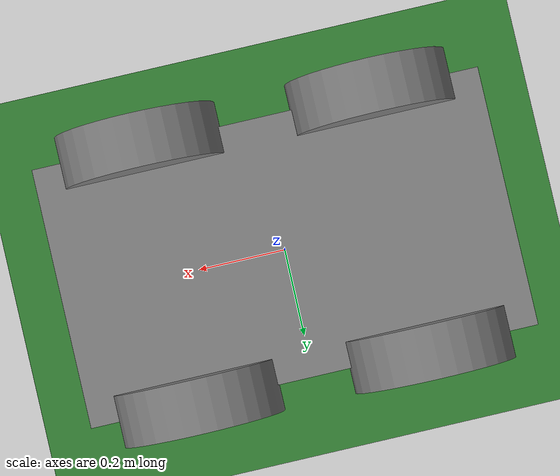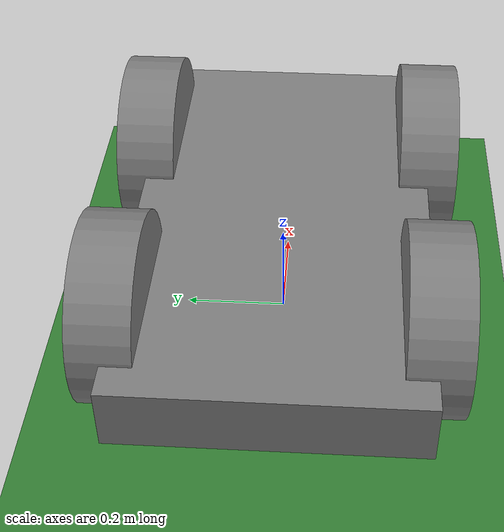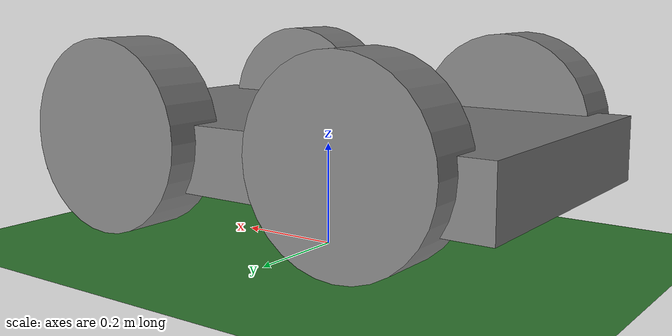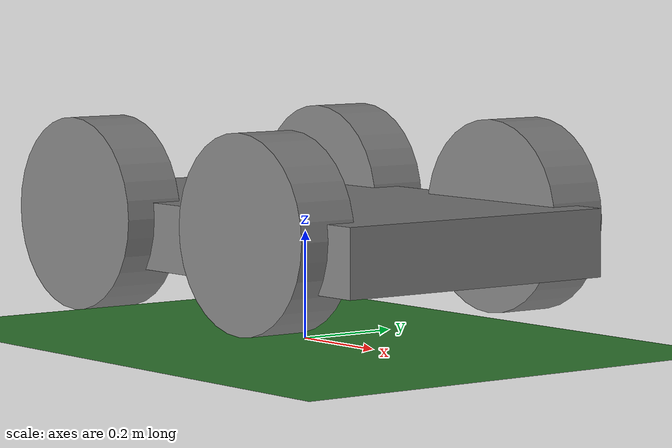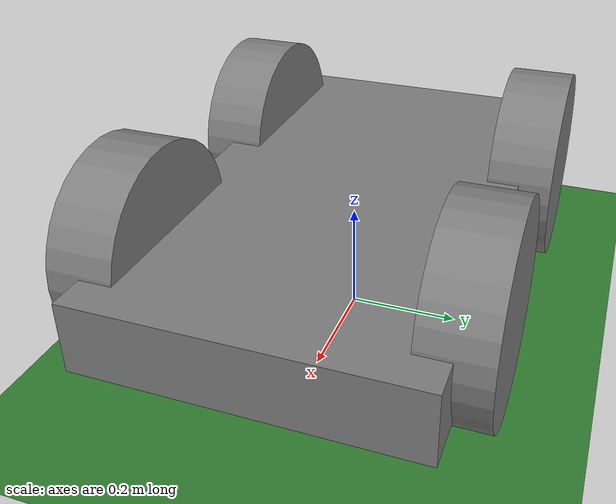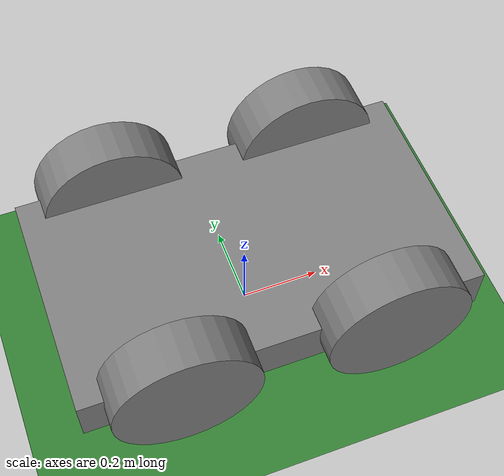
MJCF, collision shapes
<mujoco model="uneven_terrain_scene_mjx">
  <compiler angle="radian" coordinate="local" meshdir="./stls/dual_ur5_husky" texturedir="./textures"/>

  <size nuserdata="100" njmax="500" nconmax="1000" nstack="600000" nuser_body="9" nuser_jnt="1" nuser_site="1" nuser_tendon="1" nuser_actuator="12" nuser_sensor="1"/>

  <visual>
    <headlight diffuse="0.6 0.6 0.6" ambient="0.3 0.3 0.3" specular="0 0 0"/>
    <rgba haze="0.15 0.25 0.35 1"/>
    <global offwidth="2048" offheight="1536" azimuth="-120" elevation="-20"/>
    <map fogstart="3" fogend="5" force="0.1" znear="0.1"/>
    <quality shadowsize="8192"/>
  </visual>

  <default>
    <geom contype="1" conaffinity="1" margin="0.002" solimp="0.9 0.95 0.001" solref="0.02 1" condim="4" friction="1.2 0.05 0.05"/>
    <joint armature="0.01" damping="0.1"/>
    <default class="UR5">
      <joint damping="200"/>
    </default>
    <default class="UR5e">
      <joint damping="100"/>
    </default>
    <default class="GRIPPER">
      <joint damping="5"/>
      <geom rgba="0.424 0.424 0.424 1.0" contype="1" conaffinity="1" margin="0.002" solimp="0.95 0.95 0.01" solref="0.01 1" condim="3" type="mesh"/>
    </default>
    <default class="ur5:blue">
      <geom rgba="0.635 0.784 0.910 1.0"/>
    </default>
    <default class="ur5:grey">
      <geom rgba="0.365 0.365 0.365 1.0"/>
    </default>
    <default class="ur5:black">
      <geom rgba="0.106 0.106 0.106 1.0"/>
    </default>
    <default class="husky:orange">
      <geom rgba="0.996 0.941 0.412 1.0"/>
    </default>
    <default class="husky:black">
      <geom rgba="0.192 0.192 0.192 1.0"/>
    </default>
    <default class="gripper:black">
      <geom rgba="0.424 0.424 0.424 1.0"/>
    </default>
    <default class="gripper:white">
      <geom rgba="0.898 0.898 0.898 1.0" contype="1" conaffinity="1" margin="0.002" solimp="0.95 0.95 0.01" solref="0.01 1" condim="4" type="mesh"/>
    </default>
    <default class="bb2_camera">
      <geom rgba="0.776 0.624 0.294 1.0"/>
    </default>
    <default class="wheel">
      <geom rgba="0.231 0.231 0.231 1.0" friction="2.0 0.1 0.1"/>
    </default>
    <default class="sick_lidar">
      <geom rgba="0.761 0.714 0.576 1.0"/>
    </default>
    <default class="dual_ur5_husky">
      <geom rgba="0.761 0.714 0.576 1.0"/>
    </default>
  </default>

  <asset>

    <hfield name="hfield" size="30 30 3 0.3" nrow="128" ncol="128" elevation="
            0.0145909 0.0177513 0.0236914 0.0321978 0.0427267 0.0543864 0.0660309 0.0764745 0.0847543 0.0903356 0.0931833 0.0936885 0.0925022 0.0903473 0.0878584 0.0854591 0.0832618 0.0813863 0.0809578 0.0826473 0.0864451 0.0918795 0.0982041 0.104556 0.110088 0.114066 0.115952 0.115443 0.112497 0.107321 0.100338 0.0921231 0.0833117 0.0747435 0.0679276 0.0639361 0.0632058 0.0656533 0.0707877 0.0778206 0.0857739 0.0935843 0.100207 0.104713 0.106389 0.104834 0.100045 0.0925146 0.0833117 0.0740936 0.0664748 0.0614983 0.0596638 0.061002 0.0651538 0.0714528 0.0790137 0.0868238 0.0938398 0.0990884 0.101772 0.101378 0.0977926 0.091422 0.0833117 0.0749739 0.0672937 0.0609095 0.0563555 0.053992 0.0539603 0.0561599 0.0602509 0.0656792 0.0717255 0.0775788 0.0824329 0.0856067 0.0866888 0.0857053 0.0833117 0.0807254 0.0786332 0.0773453 0.0769972 0.0775783 0.078961 0.0809296 0.083209 0.0854944 0.0874801 0.088889 0.0895023 0.0891885 0.0879339 0.0858715 0.0833117 0.0803463 0.0759503 0.0697071 0.0619802 0.0535995 0.0455985 0.039001 0.0346587 0.0331375 0.0346557 0.0390708 0.0459168 0.0544916 0.0639912 0.0736919 0.0831744 0.0927211 0.103107 0.113987 0.123975 0.131111 0.133396 0.129386 0.118739 0.10249 0.0828865 0.0627858 0.0448376 0.0308172 0.0213767 0.0162399
            0.0153288 0.0187108 0.0250572 0.0341712 0.0454911 0.0580615 0.0706314 0.0818916 0.0907699 0.096667 0.0995397 0.0998232 0.098246 0.0956196 0.0926563 0.0898293 0.087255 0.0850999 0.0848273 0.0873353 0.092659 0.100238 0.109147 0.118293 0.126579 0.133036 0.136919 0.137775 0.135478 0.130228 0.122516 0.113069 0.102745 0.0926682 0.0846246 0.079856 0.0788655 0.0815527 0.087345 0.0953258 0.10436 0.113215 0.120682 0.125688 0.12741 0.125386 0.11962 0.110681 0.0998098 0.0889114 0.0798125 0.0736905 0.0711137 0.0721232 0.0763203 0.0829587 0.0910426 0.09943 0.106942 0.112475 0.115123 0.1143 0.109873 0.102294 0.0927451 0.0829797 0.0741811 0.0672195 0.0627736 0.0612606 0.0627943 0.0671711 0.0738835 0.0821613 0.0910417 0.0994655 0.106403 0.111004 0.112784 0.111825 0.109019 0.10595 0.103461 0.101917 0.10148 0.10214 0.103752 0.106062 0.108749 0.111454 0.113815 0.115505 0.116261 0.115926 0.114481 0.11208 0.10909 0.105601 0.100321 0.0926935 0.0831161 0.0725684 0.0622945 0.0535463 0.0473855 0.0445443 0.0453454 0.0496812 0.0570503 0.0666545 0.0775504 0.0888569 0.100013 0.111266 0.123523 0.136383 0.148209 0.156678 0.159412 0.154684 0.142069 0.122773 0.0994493 0.0754862 0.0540418 0.0372507 0.025921 0.0197566
            0.0175208 0.0214246 0.0287397 0.0392513 0.0523139 0.0668158 0.0812942 0.0942168 0.104332 0.110944 0.114016 0.114073 0.111981 0.108704 0.10508 0.101663 0.0985743 0.0960652 0.0961718 0.100168 0.108155 0.119411 0.132698 0.146531 0.159392 0.169915 0.177022 0.18002 0.178656 0.17313 0.164068 0.152453 0.13951 0.12684 0.116734 0.110747 0.109489 0.11281 0.119965 0.129787 0.14084 0.15158 0.160501 0.166278 0.167908 0.16484 0.157104 0.145431 0.131368 0.117256 0.105289 0.0968887 0.0927605 0.0929832 0.0971062 0.104255 0.113244 0.1227 0.131193 0.137374 0.14012 0.138693 0.132903 0.123277 0.111244 0.0990054 0.0882692 0.0803002 0.0760159 0.0759196 0.0800679 0.0880719 0.0991328 0.112112 0.125633 0.138223 0.148479 0.155279 0.158019 0.156888 0.153176 0.149081 0.145705 0.143515 0.142735 0.143378 0.145283 0.148148 0.151578 0.155116 0.158295 0.160679 0.161911 0.161761 0.16018 0.157349 0.153739 0.149465 0.142794 0.132938 0.120366 0.106322 0.0924135 0.0802835 0.0713483 0.0666153 0.0665735 0.0711591 0.079795 0.0915043 0.105096 0.119418 0.133674 0.148075 0.163751 0.180175 0.19523 0.205912 0.209151 0.20272 0.186076 0.160787 0.130292 0.0989826 0.0709579 0.0489972 0.0341666 0.0261011
            0.0204541 0.0249533 0.0333797 0.0454328 0.060319 0.0767294 0.0929888 0.10738 0.118534 0.125724 0.128963 0.128879 0.12647 0.122817 0.118849 0.115166 0.111875 0.109365 0.110422 0.116811 0.128719 0.145218 0.164668 0.185072 0.20437 0.220678 0.232483 0.238777 0.239139 0.23377 0.223464 0.209535 0.19369 0.178151 0.165871 0.158779 0.15758 0.162006 0.171049 0.183187 0.196592 0.20933 0.21955 0.22566 0.226487 0.221435 0.21062 0.195002 0.176499 0.15791 0.141776 0.129774 0.122795 0.121018 0.124001 0.130785 0.140023 0.150109 0.159332 0.166045 0.168843 0.166763 0.159494 0.147605 0.132784 0.117805 0.105131 0.096577 0.0933523 0.0960175 0.104484 0.118048 0.135471 0.155087 0.17496 0.193079 0.207582 0.217032 0.220725 0.219034 0.213804 0.208025 0.203093 0.199607 0.197906 0.198085 0.200019 0.203394 0.207746 0.21251 0.217065 0.220806 0.223201 0.223873 0.222679 0.219803 0.215849 0.211011 0.203014 0.190772 0.174824 0.156729 0.138537 0.122373 0.110097 0.103068 0.102001 0.106906 0.117135 0.131511 0.148549 0.166763 0.185048 0.20353 0.223587 0.244483 0.263433 0.27652 0.279763 0.270307 0.247506 0.213479 0.172775 0.131163 0.0940089 0.064933 0.0453113 0.0346508
            0.0238076 0.0287842 0.0381163 0.0512886 0.0672706 0.084557 0.101372 0.116012 0.127212 0.134394 0.137702 0.137852 0.135867 0.132802 0.129532 0.126586 0.12403 0.122442 0.125409 0.135202 0.152099 0.174956 0.201721 0.229866 0.256767 0.280006 0.297618 0.308267 0.311361 0.307095 0.296438 0.281051 0.263136 0.245571 0.232014 0.224738 0.224453 0.230667 0.242003 0.256508 0.27192 0.28593 0.296396 0.301555 0.300193 0.291797 0.276684 0.256099 0.232294 0.208353 0.186928 0.169863 0.158263 0.152514 0.15233 0.156832 0.16465 0.174057 0.183131 0.189942 0.19277 0.190355 0.182164 0.168698 0.151821 0.134886 0.121312 0.113562 0.113108 0.120463 0.135246 0.156279 0.181734 0.209303 0.236421 0.260512 0.279285 0.291054 0.295113 0.292132 0.2846 0.276322 0.268921 0.263128 0.259475 0.258251 0.259483 0.262944 0.268168 0.274492 0.281119 0.287196 0.291913 0.294622 0.294975 0.293086 0.289702 0.285187 0.276747 0.262968 0.244427 0.222952 0.201008 0.18118 0.165775 0.156523 0.154395 0.15953 0.171263 0.188271 0.208818 0.231093 0.253649 0.276446 0.301053 0.326437 0.349023 0.36386 0.365972 0.35186 0.320862 0.275818 0.222616 0.168635 0.120669 0.083254 0.0580591 0.0443889
            0.0276883 0.0329109 0.0427473 0.0562666 0.0720759 0.0884989 0.103863 0.116816 0.126562 0.132943 0.136357 0.137548 0.137376 0.136618 0.135841 0.135331 0.135066 0.135878 0.142005 0.156102 0.178503 0.20789 0.241878 0.277528 0.311778 0.341804 0.365304 0.380704 0.387294 0.385286 0.375795 0.360753 0.342736 0.325141 0.312255 0.30657 0.308647 0.317617 0.331623 0.348223 0.364745 0.378586 0.387478 0.38969 0.384196 0.370788 0.35014 0.323835 0.294328 0.264621 0.237075 0.213522 0.195301 0.183155 0.177182 0.176833 0.180958 0.187913 0.195701 0.202179 0.205302 0.203429 0.195672 0.182293 0.16516 0.148131 0.135682 0.130921 0.135462 0.149589 0.172436 0.20219 0.236331 0.271878 0.305681 0.33472 0.356443 0.369116 0.372212 0.366811 0.356036 0.344322 0.333317 0.323865 0.316784 0.312719 0.312033 0.314747 0.32051 0.328623 0.338097 0.347755 0.356375 0.362876 0.366546 0.367311 0.366043 0.363405 0.356238 0.34283 0.32371 0.30085 0.276975 0.254998 0.237568 0.226738 0.223745 0.228913 0.24167 0.260678 0.284077 0.309829 0.336157 0.362756 0.391263 0.420267 0.445369 0.460596 0.460029 0.439624 0.398825 0.341323 0.274447 0.207229 0.147884 0.101804 0.0708712 0.0541112
            0.0324723 0.0376946 0.0476216 0.060658 0.0748947 0.0885174 0.100208 0.109372 0.116118 0.121034 0.12489 0.128372 0.131935 0.135757 0.139791 0.143868 0.14784 0.152852 0.163444 0.182383 0.209982 0.244821 0.284365 0.325509 0.365036 0.399995 0.428 0.447442 0.457627 0.458828 0.452256 0.439954 0.424602 0.409799 0.40028 0.398576 0.404902 0.417837 0.434933 0.45323 0.469695 0.481586 0.486722 0.483686 0.47193 0.451818 0.424573 0.392144 0.357006 0.321601 0.287515 0.256359 0.229725 0.208885 0.194579 0.186879 0.185141 0.188037 0.193665 0.199749 0.203917 0.204058 0.198773 0.18789 0.173081 0.158573 0.149887 0.150646 0.162397 0.184966 0.216807 0.255353 0.297361 0.339259 0.377489 0.408846 0.43082 0.441935 0.442079 0.432842 0.417845 0.401749 0.385936 0.371307 0.359069 0.350412 0.346256 0.347074 0.352791 0.362757 0.3758 0.390345 0.404624 0.416944 0.426041 0.43151 0.434303 0.435521 0.431902 0.421499 0.40469 0.383384 0.360329 0.338539 0.32083 0.309471 0.305949 0.310842 0.323809 0.343686 0.368687 0.396706 0.425689 0.454963 0.486083 0.517224 0.543224 0.55721 0.552487 0.524633 0.47332 0.403132 0.322782 0.242822 0.172716 0.118557 0.0823268 0.0627185
            0.0385258 0.04357 0.0533111 0.0652416 0.0767835 0.0860128 0.0922049 0.0959097 0.0985441 0.101735 0.10672 0.114029 0.123455 0.134264 0.145496 0.15633 0.166479 0.177438 0.193557 0.21733 0.248942 0.286961 0.328947 0.371966 0.413033 0.449462 0.479139 0.500712 0.513697 0.518503 0.516371 0.50924 0.499516 0.490541 0.48727 0.492076 0.50463 0.522807 0.543471 0.563129 0.57847 0.586766 0.586162 0.575824 0.555982 0.527828 0.493305 0.454758 0.41447 0.373862 0.333306 0.294015 0.257854 0.226783 0.202415 0.185706 0.176761 0.174772 0.178074 0.184322 0.190799 0.194841 0.194392 0.188674 0.178989 0.169807 0.167538 0.176093 0.196693 0.228478 0.269071 0.315097 0.362661 0.407778 0.446766 0.476591 0.495171 0.50163 0.496524 0.482002 0.461944 0.440692 0.419023 0.397821 0.378774 0.363795 0.354574 0.352244 0.35717 0.368854 0.385966 0.406488 0.427987 0.447998 0.464532 0.476709 0.485499 0.492567 0.494832 0.490193 0.478766 0.462168 0.4429 0.423813 0.407687 0.396884 0.393111 0.397268 0.409397 0.428714 0.453733 0.482455 0.512628 0.543116 0.575278 0.606898 0.632189 0.64359 0.633853 0.59835 0.537047 0.455345 0.363133 0.272201 0.192984 0.132072 0.0914528 0.0694801
            0.0459406 0.0507386 0.0602204 0.0707774 0.0790472 0.0830181 0.0827333 0.0801639 0.0783181 0.0800514 0.0871181 0.0997826 0.116978 0.136809 0.157183 0.176488 0.194316 0.212526 0.234738 0.262762 0.296524 0.334677 0.375128 0.415476 0.453381 0.486844 0.514416 0.535319 0.5495 0.557591 0.560807 0.560748 0.559139 0.558565 0.563967 0.577401 0.597846 0.622361 0.647067 0.667948 0.681486 0.685107 0.677461 0.658522 0.62951 0.592644 0.550706 0.506443 0.461786 0.416776 0.3703 0.323074 0.277266 0.23563 0.200801 0.174778 0.158567 0.151995 0.153701 0.161293 0.171682 0.181579 0.188173 0.189968 0.187806 0.186307 0.192525 0.210367 0.240479 0.281141 0.329067 0.380111 0.429872 0.474202 0.509626 0.533654 0.545007 0.543737 0.53126 0.510284 0.484646 0.457804 0.42961 0.400866 0.373787 0.351142 0.335551 0.328972 0.332346 0.345423 0.366754 0.393865 0.423588 0.452582 0.478012 0.498409 0.514697 0.529171 0.539174 0.542524 0.538968 0.529635 0.516535 0.502136 0.488997 0.479468 0.475453 0.478238 0.488381 0.505665 0.529093 0.556943 0.586827 0.61708 0.648815 0.679523 0.702989 0.711203 0.696583 0.654418 0.584945 0.494184 0.392874 0.293668 0.207662 0.141757 0.0979031 0.0741693
            0.0544018 0.0589869 0.0683123 0.0775824 0.0826042 0.0812958 0.07455 0.0658743 0.0599716 0.0609756 0.0711352 0.0903688 0.116627 0.146727 0.177344 0.206027 0.232283 0.258334 0.286596 0.317836 0.351606 0.386719 0.421641 0.454809 0.484885 0.510922 0.532474 0.549623 0.562939 0.573368 0.582048 0.590052 0.598063 0.607471 0.623017 0.646348 0.675682 0.707223 0.736343 0.758531 0.770118 0.768766 0.753736 0.725915 0.687625 0.642189 0.59328 0.544033 0.495928 0.447473 0.396007 0.341756 0.287218 0.235973 0.191718 0.157523 0.135308 0.125537 0.127142 0.137658 0.153584 0.170967 0.186203 0.19706 0.203926 0.211539 0.22731 0.25486 0.294067 0.342265 0.395277 0.448294 0.496605 0.536161 0.563996 0.578481 0.57943 0.568047 0.546718 0.51865 0.487349 0.454913 0.420052 0.383419 0.347769 0.316772 0.294061 0.2825 0.28369 0.297697 0.323003 0.356695 0.394872 0.433287 0.468213 0.497533 0.522068 0.544745 0.563463 0.575993 0.581644 0.580921 0.575195 0.566404 0.556778 0.548595 0.543953 0.544574 0.55163 0.565593 0.586094 0.611783 0.640182 0.669053 0.699305 0.728288 0.749577 0.754936 0.736613 0.689859 0.615056 0.518557 0.411561 0.307198 0.216938 0.147871 0.101938 0.0770378
            0.063226 0.0676889 0.0770463 0.085351 0.0876161 0.0817107 0.0693643 0.0555686 0.0466372 0.0478892 0.0619872 0.0884498 0.124224 0.16485 0.205795 0.243817 0.278392 0.31208 0.34578 0.378981 0.410784 0.440203 0.466395 0.488834 0.507407 0.52246 0.534772 0.545472 0.555889 0.567344 0.580875 0.596904 0.614837 0.634581 0.660567 0.694015 0.732402 0.771115 0.80482 0.828555 0.838536 0.832686 0.81088 0.774912 0.728177 0.675074 0.620129 0.566833 0.516203 0.465258 0.409948 0.350106 0.288575 0.229723 0.178226 0.138126 0.112147 0.10129 0.104692 0.11975 0.14252 0.168383 0.192977 0.2134 0.229678 0.246699 0.271962 0.308578 0.35557 0.409335 0.464901 0.516958 0.560681 0.592342 0.609699 0.612177 0.600835 0.578115 0.54738 0.512234 0.475633 0.438031 0.396897 0.352704 0.308702 0.269434 0.239519 0.222729 0.221337 0.235755 0.264443 0.304106 0.350169 0.397533 0.441612 0.479652 0.512327 0.543127 0.570509 0.592186 0.606996 0.614778 0.616217 0.612689 0.60608 0.598593 0.592538 0.590109 0.593143 0.602851 0.619536 0.642254 0.668431 0.695251 0.723526 0.750655 0.770203 0.773876 0.753843 0.705273 0.628494 0.529863 0.420653 0.314131 0.221932 0.151296 0.104244 0.0786619
            0.0715235 0.0759553 0.0855097 0.0932342 0.0934642 0.0840507 0.0674733 0.0500188 0.0393778 0.0418489 0.0603847 0.0940851 0.138963 0.189404 0.239812 0.286269 0.328285 0.368714 0.40683 0.44077 0.469156 0.491209 0.506818 0.516545 0.521578 0.523626 0.524768 0.527243 0.533188 0.544321 0.561582 0.584704 0.611741 0.641018 0.676625 0.719412 0.766204 0.811674 0.849874 0.875446 0.884507 0.875207 0.847961 0.805355 0.751723 0.692406 0.632675 0.576332 0.52399 0.471397 0.413428 0.349682 0.283348 0.219476 0.163555 0.120396 0.0933311 0.0837239 0.0907832 0.111692 0.142046 0.1766 0.210327 0.239784 0.264794 0.290458 0.324165 0.368397 0.421331 0.478533 0.534386 0.583251 0.620356 0.642427 0.648043 0.63773 0.613784 0.579832 0.540119 0.498533 0.457366 0.415362 0.368799 0.317953 0.266494 0.219728 0.183158 0.161374 0.157274 0.171609 0.202855 0.247415 0.300148 0.355224 0.407305 0.453062 0.493004 0.53106 0.566121 0.595791 0.618445 0.633294 0.640403 0.640656 0.63566 0.627601 0.619045 0.612676 0.61099 0.615921 0.628406 0.647865 0.67159 0.696194 0.722557 0.748307 0.767156 0.770859 0.751512 0.704093 0.628647 0.531214 0.422814 0.316598 0.224254 0.153204 0.105685 0.0797409
            0.0783993 0.082844 0.0926499 0.100088 0.0989925 0.0872404 0.0679324 0.0483776 0.0373177 0.0417582 0.0648002 0.105135 0.157977 0.216764 0.275052 0.328411 0.376436 0.422232 0.463539 0.497228 0.52146 0.535646 0.540351 0.537152 0.52845 0.517237 0.506813 0.500463 0.501091 0.510802 0.530448 0.55912 0.593608 0.630738 0.674305 0.724882 0.778792 0.830137 0.872473 0.900114 0.909078 0.897673 0.866721 0.819417 0.760826 0.697026 0.633877 0.575441 0.522029 0.468451 0.408904 0.342929 0.274048 0.207847 0.1504 0.10704 0.0814651 0.075197 0.0873751 0.114898 0.152903 0.195598 0.237421 0.274561 0.306806 0.339557 0.379983 0.429928 0.486831 0.545589 0.60012 0.644607 0.674436 0.686828 0.681153 0.65894 0.623579 0.579707 0.532289 0.485387 0.440623 0.39519 0.34433 0.288131 0.230583 0.177602 0.135406 0.109258 0.10258 0.116424 0.149309 0.197429 0.255212 0.316261 0.374644 0.426555 0.472346 0.516226 0.557307 0.593008 0.621271 0.64079 0.651153 0.652901 0.647498 0.637211 0.624912 0.613783 0.606939 0.606957 0.615308 0.631675 0.65315 0.675804 0.700747 0.725998 0.74552 0.75115 0.734864 0.691304 0.620003 0.526422 0.42109 0.316893 0.225546 0.154735 0.107073 0.0809156
            0.0831352 0.0875637 0.0975232 0.10478 0.102879 0.0897788 0.0690616 0.0487576 0.0383036 0.0451218 0.0723229 0.118223 0.177408 0.242613 0.306791 0.365185 0.417508 0.467076 0.510345 0.543125 0.563189 0.570092 0.564954 0.55019 0.529211 0.506076 0.48511 0.470483 0.465748 0.473347 0.494069 0.526479 0.566304 0.609116 0.658502 0.714879 0.77423 0.830257 0.876148 0.905957 0.9156 0.903461 0.870607 0.82063 0.759083 0.692547 0.627298 0.567595 0.513575 0.459483 0.399243 0.332506 0.26309 0.196955 0.140524 0.0993919 0.0773824 0.0759813 0.0941328 0.128401 0.173499 0.223183 0.271513 0.31448 0.351998 0.389843 0.434951 0.488616 0.54771 0.606656 0.659078 0.6991 0.722303 0.726353 0.711276 0.679405 0.634972 0.583376 0.5301 0.479289 0.431992 0.384167 0.330256 0.270183 0.208152 0.15051 0.103992 0.0743575 0.0654246 0.0784865 0.112124 0.162405 0.223479 0.288559 0.351294 0.407532 0.45748 0.505467 0.550566 0.589918 0.621088 0.642398 0.65315 0.653737 0.645644 0.631343 0.614069 0.597494 0.585287 0.580552 0.585157 0.598917 0.618643 0.639893 0.664159 0.689965 0.711573 0.720889 0.709684 0.672115 0.607018 0.519087 0.418217 0.316974 0.227137 0.156775 0.109011 0.082649
            0.0853442 0.0896564 0.0995311 0.106505 0.104046 0.0902627 0.0690902 0.0489999 0.0397922 0.0490409 0.0797466 0.129894 0.193619 0.263193 0.331208 0.392741 0.447652 0.499423 0.543574 0.575136 0.591584 0.59257 0.579605 0.555713 0.525039 0.492427 0.46296 0.441465 0.431989 0.437231 0.457949 0.492328 0.535312 0.581551 0.634529 0.694624 0.757639 0.817037 0.865766 0.897691 0.908619 0.896924 0.863772 0.81294 0.750236 0.682515 0.616298 0.555984 0.501662 0.447359 0.387081 0.320719 0.252343 0.188124 0.134623 0.0974664 0.0803963 0.0847064 0.109053 0.149646 0.200825 0.256007 0.30902 0.355813 0.39655 0.437434 0.485226 0.540825 0.600734 0.659097 0.70939 0.745749 0.763933 0.76194 0.740256 0.701749 0.651207 0.594509 0.537449 0.484195 0.435386 0.386143 0.330374 0.267871 0.202956 0.14223 0.0927472 0.060586 0.0498262 0.0619354 0.0955608 0.146726 0.209435 0.276682 0.34187 0.400628 0.453045 0.503418 0.550527 0.591142 0.622513 0.642747 0.651056 0.647886 0.634916 0.614939 0.59161 0.569077 0.551482 0.542333 0.543745 0.555533 0.574141 0.594648 0.619038 0.646405 0.671323 0.685716 0.681061 0.650907 0.593258 0.511934 0.416142 0.318141 0.229848 0.159823 0.111816 0.085166
            0.0851271 0.0891835 0.0986636 0.105108 0.102095 0.0879427 0.0668458 0.0474967 0.0397988 0.0512713 0.0847171 0.137836 0.204459 0.276599 0.346677 0.409739 0.465798 0.518471 0.562694 0.592996 0.606656 0.603371 0.584891 0.554616 0.517152 0.477842 0.442257 0.415654 0.402406 0.405393 0.425367 0.460276 0.504567 0.552298 0.606951 0.668956 0.73407 0.795648 0.846505 0.880376 0.892959 0.882556 0.850306 0.800005 0.737521 0.669801 0.603468 0.543011 0.488567 0.434228 0.374339 0.309111 0.242819 0.181717 0.132334 0.100157 0.0886982 0.0989539 0.12924 0.175421 0.231519 0.290715 0.346726 0.39558 0.437765 0.479936 0.528774 0.584953 0.644791 0.702316 0.750963 0.784911 0.800045 0.794561 0.769197 0.727103 0.673341 0.614024 0.555081 0.500663 0.45118 0.40131 0.34466 0.280933 0.214479 0.152015 0.100748 0.0669193 0.0547573 0.0658425 0.0988881 0.149932 0.212943 0.280837 0.346911 0.406682 0.460152 0.511467 0.558901 0.598779 0.628093 0.644868 0.648399 0.639353 0.619748 0.592792 0.562604 0.533787 0.510887 0.497706 0.496478 0.506897 0.524978 0.545342 0.570536 0.600249 0.629346 0.649722 0.652479 0.630477 0.580816 0.506401 0.415754 0.320873 0.233892 0.163945 0.115484 0.0884352
            0.0832618 0.086947 0.0957842 0.101463 0.0977877 0.0833301 0.0624916 0.0440597 0.0378907 0.0513312 0.0869393 0.142161 0.210614 0.284173 0.355207 0.418804 0.475128 0.527915 0.571755 0.600872 0.612415 0.606097 0.5838 0.549142 0.507007 0.46304 0.423112 0.392753 0.376545 0.377493 0.396357 0.430952 0.475413 0.523445 0.578585 0.641369 0.707585 0.770561 0.823048 0.858687 0.873072 0.864398 0.833705 0.78471 0.723228 0.656185 0.59022 0.529883 0.475413 0.421126 0.361843 0.298131 0.234436 0.177015 0.13227 0.105454 0.0997729 0.115874 0.151717 0.202834 0.262981 0.325166 0.383073 0.432873 0.475413 0.517798 0.566707 0.622711 0.682066 0.738779 0.786305 0.818872 0.832443 0.825312 0.798323 0.754736 0.699707 0.639418 0.579827 0.525058 0.475413 0.425393 0.36846 0.304245 0.237085 0.17372 0.121411 0.0864671 0.0731923 0.0832409 0.11539 0.165727 0.228248 0.295875 0.361886 0.421756 0.475413 0.526788 0.573521 0.611452 0.637352 0.649248 0.646617 0.630453 0.603195 0.568527 0.531048 0.495806 0.467704 0.450764 0.447262 0.456702 0.47463 0.495223 0.52162 0.554105 0.587815 0.614578 0.625084 0.611465 0.569892 0.502353 0.41671 0.324739 0.238839 0.168763 0.119694 0.0921694
            0.0807404 0.0839918 0.0920712 0.096888 0.0925394 0.0778934 0.0575542 0.0403542 0.0360242 0.0516595 0.0895173 0.146768 0.21683 0.291473 0.36306 0.426766 0.482932 0.535427 0.578545 0.606251 0.615586 0.606283 0.580341 0.54157 0.495091 0.446809 0.402851 0.368973 0.349936 0.348844 0.366458 0.400473 0.444767 0.49274 0.547987 0.611155 0.67809 0.74213 0.795992 0.833252 0.849411 0.842558 0.81362 0.766205 0.706038 0.639983 0.574664 0.514667 0.460345 0.406289 0.347857 0.285994 0.225295 0.171982 0.132279 0.111156 0.111472 0.133501 0.174835 0.230686 0.294563 0.359338 0.418704 0.469004 0.511462 0.553625 0.602158 0.657545 0.716022 0.771621 0.817852 0.849024 0.861187 0.852721 0.82455 0.779994 0.72425 0.663511 0.603717 0.548941 0.499404 0.449503 0.392642 0.328411 0.261118 0.197489 0.144783 0.109323 0.0954381 0.104819 0.136285 0.18597 0.247914 0.315074 0.380745 0.440395 0.493915 0.545018 0.590694 0.626291 0.648365 0.65496 0.645759 0.622099 0.586854 0.544194 0.499203 0.457367 0.423935 0.403139 0.397279 0.405655 0.42334 0.444067 0.47154 0.506638 0.544783 0.577772 0.595919 0.59066 0.557259 0.496783 0.4164 0.327628 0.243082 0.173098 0.123577 0.0956653
            0.0768734 0.0795384 0.0866197 0.0904396 0.0855988 0.0714088 0.0526957 0.0382049 0.0373001 0.0565519 0.0976891 0.157475 0.2291 0.304294 0.375529 0.438209 0.492981 0.543931 0.585082 0.610171 0.616176 0.602891 0.572469 0.528928 0.477627 0.424706 0.376508 0.338961 0.316937 0.313579 0.329605 0.362576 0.406139 0.453447 0.508095 0.57083 0.637607 0.70186 0.756371 0.794733 0.81242 0.807441 0.780601 0.735357 0.67727 0.613056 0.549234 0.49037 0.436921 0.383849 0.327233 0.268458 0.212211 0.164559 0.131392 0.117247 0.124511 0.152998 0.199904 0.260138 0.327035 0.393437 0.453158 0.502825 0.544093 0.584899 0.63176 0.685054 0.741064 0.793976 0.837502 0.866158 0.87618 0.866085 0.83687 0.791858 0.736186 0.675934 0.616901 0.563014 0.514392 0.465457 0.409808 0.347121 0.281658 0.220021 0.169308 0.135676 0.123306 0.133785 0.165879 0.215722 0.277407 0.343986 0.408872 0.467647 0.520278 0.570352 0.614242 0.646821 0.664434 0.665141 0.648817 0.617128 0.57337 0.52218 0.469111 0.420078 0.380667 0.355316 0.34635 0.352878 0.369516 0.389532 0.417063 0.453554 0.49482 0.532812 0.557695 0.560407 0.535415 0.482848 0.409034 0.324982 0.243265 0.174595 0.125479 0.0976674
            0.0712817 0.0731901 0.0790231 0.0817929 0.0768983 0.0642882 0.0490056 0.039485 0.0443462 0.0692255 0.114999 0.177848 0.250727 0.325438 0.394761 0.454539 0.505919 0.553314 0.590547 0.611208 0.612292 0.593727 0.557862 0.508933 0.452506 0.394898 0.342567 0.301497 0.276548 0.270791 0.284824 0.316061 0.358004 0.403678 0.45659 0.517562 0.582742 0.645799 0.699733 0.738301 0.757046 0.75395 0.729686 0.687495 0.632662 0.571617 0.510636 0.454165 0.402747 0.351858 0.298559 0.244746 0.195104 0.155346 0.130792 0.125319 0.14066 0.17606 0.228291 0.29202 0.360532 0.426817 0.485006 0.532165 0.570446 0.608067 0.651197 0.700074 0.75116 0.798994 0.837716 0.862252 0.869169 0.857182 0.827342 0.782873 0.72868 0.670525 0.613859 0.562324 0.515918 0.4693 0.416648 0.357895 0.297223 0.240937 0.195726 0.167308 0.159468 0.173483 0.207934 0.258907 0.320584 0.386215 0.449489 0.506287 0.556821 0.604664 0.64568 0.674329 0.686773 0.681077 0.657275 0.617311 0.564839 0.504897 0.443445 0.386768 0.34075 0.310013 0.296914 0.300399 0.314699 0.332627 0.358523 0.394338 0.436435 0.477222 0.507078 0.516784 0.500218 0.456575 0.391126 0.313997 0.2373 0.171785 0.124383 0.0974188
            0.0642936 0.0653549 0.0698394 0.0717278 0.067495 0.0578873 0.0481105 0.0460084 0.0590354 0.0914639 0.142998 0.209096 0.282508 0.355272 0.420704 0.47533 0.520978 0.562492 0.593618 0.607931 0.602564 0.577656 0.535784 0.481386 0.420165 0.358492 0.302793 0.258931 0.23158 0.223593 0.235357 0.264141 0.303442 0.346352 0.396192 0.453827 0.515689 0.575843 0.627693 0.665325 0.68448 0.683175 0.661949 0.623752 0.573472 0.51709 0.460484 0.407859 0.359816 0.312493 0.264187 0.217356 0.176555 0.146911 0.132916 0.137549 0.16171 0.203983 0.260717 0.326434 0.394548 0.458418 0.512716 0.555114 0.588303 0.620617 0.657651 0.699496 0.742939 0.783112 0.814838 0.833675 0.836668 0.822791 0.793103 0.75059 0.699716 0.645673 0.593332 0.545888 0.503218 0.460477 0.412826 0.360617 0.307894 0.260468 0.224342 0.20451 0.2041 0.223881 0.262134 0.314873 0.376431 0.4404 0.500933 0.554402 0.601419 0.645653 0.682637 0.706558 0.713446 0.701359 0.670427 0.622769 0.562274 0.494247 0.42492 0.360837 0.30809 0.271436 0.253265 0.252424 0.262892 0.277109 0.299336 0.331929 0.371964 0.412649 0.445016 0.460106 0.451491 0.417476 0.362062 0.294081 0.224704 0.164319 0.120051 0.0947604
            0.0566639 0.056919 0.0601882 0.0616387 0.0590208 0.0539561 0.0516987 0.0592038 0.0823665 0.123727 0.181576 0.250581 0.323375 0.392426 0.451824 0.498995 0.536589 0.569943 0.592897 0.599203 0.586266 0.554511 0.506757 0.447585 0.382723 0.318428 0.260891 0.215637 0.186947 0.177287 0.186741 0.212462 0.248131 0.287161 0.332598 0.385309 0.442097 0.497584 0.545762 0.581217 0.600019 0.600291 0.58244 0.549065 0.504535 0.454233 0.40348 0.356117 0.312774 0.270367 0.228625 0.190573 0.160489 0.142692 0.140609 0.156112 0.189132 0.237542 0.297318 0.362969 0.428242 0.487101 0.534983 0.570316 0.596324 0.621246 0.649897 0.68223 0.715524 0.745735 0.768608 0.780535 0.779167 0.763773 0.735352 0.696494 0.650998 0.603232 0.55725 0.515657 0.478228 0.440889 0.400126 0.356827 0.31482 0.279223 0.255111 0.246496 0.255633 0.282639 0.325424 0.379948 0.440792 0.502045 0.558511 0.607229 0.649317 0.688602 0.720547 0.739269 0.740749 0.723022 0.686222 0.632495 0.565778 0.491441 0.415794 0.345457 0.286598 0.244031 0.220176 0.213874 0.219053 0.227939 0.244415 0.271111 0.305953 0.343289 0.375246 0.393568 0.39184 0.367575 0.323337 0.266289 0.206199 0.152689 0.112836 0.0899773
            0.0493371 0.0489722 0.0514094 0.0531263 0.0532303 0.0541928 0.0611478 0.0798797 0.11441 0.165294 0.22929 0.300296 0.370969 0.434415 0.485709 0.523346 0.550872 0.574121 0.587243 0.584387 0.56337 0.52497 0.472229 0.409786 0.343235 0.278523 0.221367 0.176716 0.148236 0.137836 0.145217 0.167466 0.198668 0.232855 0.272727 0.319108 0.369244 0.418452 0.461474 0.49355 0.5112 0.512721 0.498401 0.470443 0.432599 0.389528 0.345857 0.30496 0.267453 0.231109 0.197185 0.169232 0.151098 0.146108 0.156436 0.182709 0.223816 0.276925 0.337728 0.400884 0.460681 0.511917 0.550984 0.577173 0.594188 0.609929 0.628279 0.649093 0.670285 0.688836 0.701612 0.705993 0.700321 0.684161 0.65837 0.624984 0.586923 0.547499 0.509749 0.475572 0.444688 0.414046 0.381692 0.349095 0.319776 0.297996 0.287706 0.291762 0.31141 0.346032 0.393167 0.448783 0.507831 0.565055 0.616071 0.658712 0.694639 0.727848 0.754044 0.767527 0.76434 0.742479 0.701965 0.644788 0.574701 0.496885 0.417474 0.342944 0.279362 0.231499 0.2018 0.189215 0.18787 0.190006 0.198853 0.217159 0.243798 0.274539 0.303002 0.322047 0.3256 0.310525 0.277858 0.232804 0.183344 0.137975 0.103498 0.0836591
            0.0432528 0.0425844 0.0447904 0.0476719 0.0516469 0.0599066 0.0772587 0.10808 0.154319 0.214443 0.283689 0.355305 0.422151 0.478167 0.519581 0.546057 0.562029 0.57378 0.575999 0.563462 0.534539 0.4904 0.43427 0.370727 0.305062 0.242686 0.188608 0.146956 0.120572 0.110655 0.116462 0.135077 0.161227 0.189867 0.223309 0.262287 0.304542 0.346184 0.38283 0.410492 0.426235 0.428596 0.417761 0.395511 0.364922 0.329838 0.294097 0.26052 0.229671 0.200207 0.174901 0.157732 0.151992 0.15987 0.182182 0.218248 0.265914 0.321711 0.381169 0.439269 0.491037 0.532292 0.560526 0.575943 0.582626 0.587896 0.594613 0.602589 0.610502 0.6165 0.618696 0.615552 0.606134 0.590272 0.568587 0.542419 0.513629 0.484295 0.456286 0.430726 0.407346 0.384324 0.361363 0.340479 0.324796 0.317599 0.321602 0.338418 0.368242 0.409736 0.460119 0.515476 0.57126 0.623011 0.66728 0.702756 0.731605 0.757948 0.778063 0.786719 0.78014 0.756266 0.714886 0.657627 0.587802 0.510123 0.430271 0.354326 0.288059 0.236083 0.200863 0.181577 0.172832 0.16716 0.166907 0.17478 0.190645 0.21189 0.233929 0.251086 0.257926 0.250836 0.229327 0.196474 0.158201 0.121613 0.0930429 0.0765737
            0.0391974 0.0386351 0.0413588 0.0463958 0.0553075 0.071787 0.100095 0.143034 0.200415 0.268666 0.34165 0.412159 0.473458 0.520483 0.550721 0.565025 0.568636 0.568185 0.559123 0.537071 0.501064 0.452684 0.395276 0.33323 0.271352 0.21431 0.166178 0.130058 0.107783 0.0997228 0.104654 0.119736 0.140556 0.163274 0.189803 0.220752 0.254371 0.28762 0.317058 0.339545 0.352756 0.355511 0.34792 0.331341 0.308154 0.281346 0.253914 0.228079 0.204317 0.182136 0.165711 0.159322 0.165595 0.185516 0.218521 0.262648 0.314771 0.3709 0.42655 0.477183 0.518724 0.548145 0.564121 0.567755 0.56338 0.557513 0.551979 0.546623 0.540966 0.534398 0.526334 0.516328 0.504152 0.48984 0.47369 0.456227 0.438133 0.420134 0.402853 0.386624 0.371264 0.35632 0.343103 0.334074 0.331869 0.338739 0.35614 0.384459 0.422895 0.469477 0.521226 0.574473 0.625305 0.670171 0.706619 0.734191 0.755454 0.774556 0.788666 0.793304 0.784992 0.761603 0.722572 0.668967 0.603409 0.529864 0.453284 0.379104 0.312606 0.258129 0.218147 0.192187 0.175613 0.161537 0.151272 0.147332 0.150562 0.160059 0.173216 0.186056 0.194024 0.193217 0.181701 0.160394 0.133037 0.105186 0.0825763 0.0695567
            0.0377 0.0376963 0.0417429 0.0499006 0.0646083 0.0897827 0.128927 0.183194 0.250328 0.324918 0.399704 0.467274 0.521492 0.558407 0.576794 0.578638 0.569837 0.557237 0.537237 0.506483 0.464751 0.414031 0.35771 0.299865 0.244654 0.195827 0.156346 0.128121 0.111857 0.107013 0.111881 0.123773 0.139319 0.156107 0.175671 0.19847 0.22325 0.247823 0.269702 0.286613 0.296862 0.299582 0.294832 0.283573 0.267505 0.24877 0.229527 0.211382 0.194699 0.179755 0.171923 0.175632 0.192778 0.223151 0.264866 0.314788 0.368955 0.423001 0.472576 0.51376 0.543481 0.55993 0.562965 0.554529 0.539049 0.522071 0.50444 0.486115 0.467498 0.449218 0.431954 0.416297 0.402655 0.391186 0.381783 0.374085 0.367538 0.361484 0.355297 0.348552 0.341238 0.334323 0.330542 0.332638 0.34269 0.361924 0.390602 0.428001 0.472465 0.521551 0.572243 0.621259 0.665435 0.702194 0.730093 0.749454 0.763081 0.775017 0.783586 0.785305 0.7771 0.756767 0.723285 0.67699 0.619597 0.554084 0.484432 0.415217 0.351057 0.295919 0.252271 0.220096 0.195749 0.173199 0.152662 0.13634 0.125982 0.12238 0.124947 0.131504 0.138533 0.142017 0.138739 0.127557 0.110069 0.0902503 0.0731794 0.0634158
            0.0389743 0.0399688 0.0461007 0.0581992 0.0792494 0.113088 0.162287 0.22637 0.301221 0.379903 0.454371 0.51728 0.56326 0.589527 0.596091 0.585943 0.565444 0.541498 0.511581 0.473485 0.427758 0.376765 0.323858 0.272691 0.226653 0.18845 0.159823 0.141402 0.132699 0.132251 0.137883 0.147129 0.157782 0.169 0.181985 0.197034 0.213351 0.229545 0.244035 0.255374 0.262484 0.26481 0.262387 0.255823 0.246197 0.234867 0.223205 0.212234 0.202186 0.193988 0.193945 0.20648 0.23274 0.2714 0.319397 0.372594 0.426374 0.476162 0.517874 0.5483 0.565412 0.5686 0.558843 0.538806 0.512861 0.485483 0.456662 0.426548 0.396407 0.368024 0.343232 0.323537 0.309865 0.30241 0.300601 0.303172 0.308348 0.314138 0.31874 0.321055 0.321315 0.321878 0.326604 0.338317 0.358498 0.387412 0.424282 0.467467 0.514676 0.5632 0.610167 0.652822 0.688833 0.716611 0.735666 0.746975 0.753382 0.758666 0.762491 0.762546 0.756242 0.741291 0.716146 0.680288 0.634368 0.580205 0.520632 0.459205 0.399754 0.345794 0.299781 0.262222 0.230637 0.200077 0.169691 0.141298 0.117428 0.100443 0.0916668 0.0906818 0.0950534 0.100797 0.103621 0.100558 0.0912415 0.0781756 0.0658014 0.0588506
            0.0429053 0.0452714 0.0541154 0.0707278 0.0982811 0.140237 0.198126 0.269958 0.350068 0.430397 0.502493 0.55934 0.596451 0.612187 0.607676 0.586724 0.555936 0.522119 0.483879 0.440196 0.392375 0.343099 0.295615 0.253073 0.218027 0.192086 0.175738 0.168328 0.168198 0.172995 0.180132 0.187418 0.193846 0.200185 0.207381 0.215567 0.224341 0.233011 0.240796 0.246986 0.251056 0.252744 0.252082 0.249386 0.245201 0.240211 0.235099 0.230368 0.22612 0.223783 0.23029 0.249925 0.28312 0.327577 0.379262 0.433258 0.484498 0.528358 0.561126 0.580333 0.58496 0.575507 0.553939 0.52349 0.488348 0.451898 0.413455 0.373425 0.333866 0.297574 0.267352 0.245446 0.233156 0.230621 0.236777 0.249488 0.265849 0.282665 0.297103 0.307513 0.314427 0.32147 0.333247 0.352455 0.379955 0.415188 0.456546 0.501732 0.548081 0.592851 0.633499 0.667912 0.694628 0.713009 0.723406 0.727282 0.72731 0.726847 0.726968 0.726624 0.72375 0.715977 0.701199 0.677986 0.645848 0.605358 0.558116 0.506576 0.453715 0.402552 0.355524 0.313696 0.275835 0.238218 0.199059 0.159766 0.123506 0.093979 0.0741823 0.0652708 0.0658294 0.072 0.078663 0.081349 0.0780494 0.0700218 0.0611714 0.0563881
            0.0490823 0.0530846 0.0650595 0.0864434 0.120249 0.169312 0.234079 0.311253 0.394008 0.473609 0.541572 0.591437 0.619653 0.625637 0.611448 0.581481 0.542369 0.500677 0.456116 0.408812 0.360761 0.314895 0.274294 0.24157 0.218432 0.20542 0.201826 0.205789 0.214577 0.225041 0.234255 0.240334 0.243426 0.245841 0.248358 0.250967 0.253574 0.25605 0.258263 0.260104 0.261507 0.262458 0.263 0.263225 0.263265 0.263263 0.26335 0.263606 0.264013 0.266343 0.27786 0.302598 0.340357 0.388066 0.440963 0.4936 0.540666 0.577631 0.601211 0.609654 0.602843 0.582228 0.550567 0.511498 0.468926 0.425216 0.379221 0.331648 0.285231 0.243576 0.210225 0.187952 0.178275 0.181196 0.195161 0.217252 0.24359 0.269976 0.29274 0.309833 0.322122 0.334299 0.351302 0.375486 0.407119 0.444983 0.486907 0.530226 0.572178 0.610229 0.642323 0.667073 0.683877 0.692959 0.695356 0.692817 0.687649 0.682639 0.680232 0.680622 0.682269 0.682731 0.679354 0.66981 0.652487 0.626723 0.592899 0.552374 0.507274 0.460125 0.413333 0.368516 0.32567 0.282344 0.236031 0.187763 0.141176 0.101006 0.0715691 0.0552815 0.0515739 0.0567486 0.0651045 0.0710639 0.0713946 0.066437 0.05973 0.0563334
            0.0568765 0.0626468 0.077927 0.104007 0.143439 0.198251 0.267837 0.347862 0.430762 0.50757 0.570106 0.612632 0.632518 0.630087 0.608106 0.571316 0.526183 0.478915 0.430228 0.381272 0.33463 0.293402 0.260462 0.237893 0.226611 0.226185 0.234846 0.249685 0.267053 0.283147 0.294788 0.3004 0.301169 0.300771 0.299921 0.298493 0.296612 0.29455 0.292645 0.291224 0.290558 0.290822 0.292076 0.294263 0.297221 0.300714 0.304477 0.308284 0.31202 0.317649 0.332495 0.360279 0.400292 0.448912 0.500914 0.550563 0.592494 0.622377 0.637366 0.636341 0.619928 0.590309 0.550819 0.505325 0.457394 0.40852 0.357319 0.304819 0.254283 0.209891 0.175673 0.154706 0.148572 0.157068 0.178192 0.208369 0.242951 0.276974 0.30617 0.328245 0.344413 0.360183 0.380405 0.406922 0.439457 0.476333 0.515087 0.552982 0.587433 0.616318 0.638204 0.652463 0.6593 0.659671 0.655112 0.647463 0.638493 0.630304 0.626551 0.628567 0.63529 0.644217 0.652199 0.656096 0.653273 0.641948 0.621384 0.591943 0.554969 0.512531 0.467008 0.420511 0.374158 0.326717 0.275232 0.220448 0.166299 0.118216 0.0814079 0.0591468 0.0514484 0.0547461 0.0629832 0.0698897 0.0714843 0.067583 0.0615786 0.0587369
            0.0655642 0.0731045 0.0916321 0.122051 0.166226 0.225271 0.297625 0.378208 0.459125 0.531567 0.58793 0.623288 0.635862 0.626698 0.599031 0.557725 0.508918 0.458389 0.407697 0.358847 0.314878 0.278981 0.253804 0.240942 0.240624 0.251599 0.271222 0.295745 0.320799 0.342088 0.356274 0.362069 0.361524 0.359444 0.356569 0.352701 0.348089 0.34325 0.338801 0.335337 0.333334 0.333088 0.334673 0.33795 0.342585 0.348119 0.354052 0.359968 0.365691 0.373248 0.389804 0.41875 0.459006 0.506629 0.556178 0.601849 0.638375 0.661688 0.669351 0.66075 0.637057 0.600955 0.556127 0.506514 0.455336 0.403414 0.34934 0.294456 0.242398 0.197684 0.164581 0.146263 0.144235 0.158055 0.185324 0.221966 0.262788 0.302315 0.335916 0.361205 0.379729 0.397542 0.419044 0.445427 0.475946 0.508662 0.541077 0.570653 0.595208 0.613203 0.623909 0.627455 0.624766 0.617376 0.607134 0.595785 0.584439 0.574434 0.570399 0.574623 0.58645 0.603325 0.621694 0.637736 0.647962 0.649647 0.641121 0.621902 0.592674 0.555121 0.51159 0.464606 0.416228 0.366306 0.311734 0.25309 0.194459 0.141624 0.10024 0.0739986 0.0631901 0.0642978 0.0710921 0.0770018 0.077768 0.0730882 0.0664492 0.0633759
            0.0744962 0.0837158 0.105277 0.139531 0.187518 0.249399 0.322788 0.402125 0.479518 0.546612 0.596554 0.625264 0.631714 0.617487 0.586077 0.542288 0.491829 0.440013 0.389065 0.341664 0.301173 0.270812 0.253002 0.248914 0.258207 0.278978 0.307906 0.340608 0.372194 0.398029 0.414695 0.421161 0.420155 0.417363 0.413625 0.408708 0.402916 0.396865 0.391294 0.386913 0.384289 0.38377 0.385443 0.389133 0.394441 0.400811 0.407645 0.414447 0.421009 0.429326 0.446265 0.474895 0.513904 0.55922 0.605384 0.646691 0.678072 0.695748 0.69763 0.683479 0.654822 0.614628 0.566736 0.515041 0.462435 0.409274 0.354294 0.299134 0.247656 0.204514 0.17401 0.159242 0.161542 0.180204 0.212503 0.254007 0.299176 0.342253 0.378447 0.405406 0.424975 0.443514 0.464693 0.488978 0.515229 0.541412 0.565207 0.584474 0.597608 0.603762 0.60295 0.596026 0.584536 0.570448 0.555762 0.541985 0.529496 0.518828 0.515329 0.522036 0.538612 0.562472 0.58974 0.616071 0.637305 0.649984 0.651701 0.641311 0.618981 0.586085 0.544944 0.498403 0.449257 0.398272 0.342451 0.28234 0.22206 0.167458 0.124243 0.0961309 0.0833884 0.0824437 0.0870188 0.0905551 0.0889132 0.0820259 0.0736918 0.0697522
            0.0833117 0.0941076 0.118487 0.156166 0.207301 0.271111 0.34448 0.421543 0.494608 0.555937 0.59951 0.622083 0.623297 0.60515 0.571265 0.526275 0.475413 0.423517 0.373354 0.328142 0.291485 0.266587 0.255654 0.259483 0.277256 0.306536 0.343466 0.383175 0.420384 0.450223 0.469243 0.476645 0.475698 0.472791 0.46891 0.463815 0.457816 0.451546 0.445764 0.4412 0.43844 0.437839 0.439491 0.443217 0.448608 0.455095 0.462062 0.469002 0.475698 0.484062 0.500596 0.528073 0.565038 0.607406 0.64982 0.68676 0.713409 0.726274 0.723562 0.705313 0.673283 0.630589 0.581103 0.528607 0.475698 0.422407 0.367716 0.313537 0.263867 0.223375 0.196272 0.185485 0.192114 0.215187 0.251703 0.29697 0.345233 0.390596 0.428232 0.455891 0.475698 0.494157 0.51406 0.535115 0.555839 0.574209 0.5882 0.596189 0.597233 0.59123 0.578946 0.561921 0.542254 0.52225 0.503956 0.488566 0.475698 0.465068 0.462561 0.471804 0.492722 0.522702 0.557622 0.592717 0.6233 0.645324 0.655798 0.653049 0.636826 0.608255 0.569633 0.52406 0.474914 0.423743 0.367833 0.307787 0.2477 0.193307 0.150129 0.121649 0.107911 0.105207 0.107268 0.107732 0.10282 0.0929195 0.082282 0.077106
            0.0918362 0.104131 0.131177 0.172043 0.226 0.291356 0.364313 0.438774 0.507314 0.562855 0.600224 0.616989 0.613416 0.591863 0.556029 0.510346 0.45956 0.408049 0.359078 0.316358 0.283688 0.264236 0.259978 0.271349 0.297083 0.334254 0.378526 0.424602 0.466879 0.500302 0.521424 0.529671 0.528804 0.525838 0.52194 0.516894 0.511025 0.504968 0.499472 0.495252 0.492868 0.492654 0.494674 0.498724 0.504374 0.511041 0.518107 0.525072 0.531748 0.539985 0.555878 0.581881 0.616407 0.655391 0.693615 0.72579 0.747383 0.755218 0.747811 0.725481 0.6902 0.64521 0.594389 0.541375 0.488448 0.435325 0.381269 0.328475 0.281053 0.243644 0.220324 0.213809 0.224937 0.252455 0.293087 0.3419 0.392953 0.440249 0.478967 0.50699 0.526724 0.544796 0.563105 0.580608 0.595498 0.605789 0.609775 0.606364 0.595286 0.577181 0.553552 0.526606 0.498963 0.473235 0.451496 0.434608 0.421438 0.410902 0.409369 0.421024 0.446038 0.481785 0.523923 0.567304 0.606751 0.637671 0.656525 0.661138 0.650859 0.626573 0.590543 0.5461 0.49717 0.446061 0.390401 0.330885 0.271562 0.218005 0.175474 0.147143 0.132775 0.128497 0.128068 0.125369 0.117044 0.103993 0.0909477 0.0844624
            0.099094 0.112612 0.14179 0.185056 0.240847 0.306669 0.378215 0.449344 0.513057 0.563017 0.594886 0.606954 0.59997 0.576497 0.540179 0.495164 0.445713 0.395804 0.349144 0.309805 0.281662 0.267739 0.269729 0.287697 0.319976 0.363256 0.412871 0.463277 0.508731 0.544161 0.566231 0.574606 0.57341 0.570082 0.566076 0.561346 0.5563 0.551581 0.547886 0.545825 0.545818 0.548033 0.552367 0.558456 0.565736 0.573537 0.58122 0.588347 0.594901 0.602813 0.617623 0.641339 0.672209 0.706229 0.738417 0.763835 0.778378 0.779315 0.765595 0.737906 0.698494 0.650738 0.598489 0.545165 0.492598 0.440087 0.387281 0.336718 0.292589 0.259423 0.241054 0.239868 0.256342 0.288867 0.333854 0.386128 0.439599 0.488233 0.527292 0.55487 0.573712 0.590597 0.606604 0.620011 0.628742 0.630872 0.625013 0.61058 0.587926 0.558363 0.524054 0.487788 0.452625 0.421427 0.396257 0.377663 0.363834 0.352984 0.351908 0.365309 0.39362 0.434257 0.482721 0.533557 0.581161 0.620444 0.647341 0.65918 0.654895 0.63509 0.601946 0.558979 0.51063 0.459993 0.405176 0.347023 0.289509 0.237947 0.197206 0.170021 0.155782 0.150417 0.147747 0.141982 0.130284 0.114119 0.0987004 0.090885
            0.104203 0.118479 0.148893 0.193247 0.249236 0.313756 0.382276 0.448921 0.507371 0.552157 0.57975 0.589 0.580901 0.557967 0.52357 0.481445 0.435376 0.389051 0.346509 0.311976 0.289196 0.28089 0.288371 0.311326 0.347772 0.394189 0.445824 0.497183 0.54269 0.577524 0.598644 0.605976 0.603785 0.599591 0.595277 0.59117 0.587861 0.586017 0.586218 0.588846 0.594015 0.601534 0.610924 0.62147 0.632313 0.642589 0.651606 0.659065 0.665319 0.672598 0.685689 0.705984 0.731533 0.758463 0.782159 0.79821 0.803122 0.794794 0.772755 0.738178 0.693641 0.64267 0.589034 0.535816 0.484235 0.433053 0.382459 0.335405 0.296112 0.268861 0.257067 0.262617 0.28548 0.323596 0.373017 0.428344 0.483411 0.532256 0.570358 0.596141 0.612754 0.62716 0.639777 0.648359 0.650659 0.644852 0.629855 0.605523 0.572721 0.533291 0.489893 0.445729 0.404149 0.368147 0.339724 0.319149 0.304094 0.29226 0.290768 0.304759 0.33495 0.378879 0.43201 0.488709 0.543064 0.589581 0.623733 0.64237 0.643989 0.62886 0.599009 0.558049 0.510866 0.461362 0.408325 0.352833 0.298729 0.250909 0.213652 0.189061 0.176012 0.170203 0.165592 0.156859 0.141826 0.122608 0.104884 0.095714
            0.106679 0.121148 0.151714 0.195579 0.249817 0.310955 0.374577 0.435442 0.488198 0.528385 0.553234 0.561958 0.555506 0.53604 0.506407 0.469783 0.429487 0.389054 0.352726 0.324632 0.308142 0.305483 0.317481 0.343443 0.381174 0.42715 0.476829 0.525113 0.566954 0.598109 0.616035 0.62094 0.616977 0.611316 0.606387 0.603082 0.60228 0.604687 0.610712 0.620394 0.633376 0.648922 0.66598 0.683289 0.699536 0.713553 0.724563 0.732475 0.738212 0.744515 0.755257 0.771072 0.7898 0.807774 0.82088 0.825396 0.818605 0.799182 0.767363 0.724878 0.674676 0.620407 0.565695 0.51318 0.463334 0.414307 0.36699 0.32481 0.291934 0.27224 0.268535 0.282026 0.312035 0.355955 0.409468 0.466991 0.522387 0.569911 0.60541 0.627764 0.640581 0.651017 0.659066 0.662187 0.658096 0.645117 0.622434 0.590227 0.549706 0.503028 0.453111 0.403333 0.357125 0.317455 0.286202 0.263418 0.246488 0.232881 0.229912 0.243045 0.273291 0.318408 0.373975 0.434341 0.493445 0.545521 0.585669 0.610306 0.617485 0.607091 0.580905 0.54253 0.497187 0.449578 0.399377 0.347978 0.299012 0.256785 0.224761 0.204201 0.193342 0.187637 0.181285 0.169608 0.151249 0.12905 0.109117 0.0985776
            0.106403 0.120481 0.150081 0.191844 0.24236 0.29804 0.354933 0.408795 0.45553 0.491805 0.515552 0.526132 0.524154 0.51112 0.489102 0.460573 0.428412 0.396148 0.368087 0.348006 0.338658 0.341589 0.357038 0.383929 0.419969 0.461843 0.505518 0.546644 0.581066 0.605432 0.617912 0.619013 0.612506 0.604773 0.598833 0.596293 0.5984 0.605917 0.619044 0.6374 0.660041 0.685544 0.712133 0.737858 0.760823 0.779472 0.792914 0.801308 0.806299 0.81131 0.819214 0.829821 0.840781 0.848702 0.850076 0.841976 0.822564 0.791372 0.749388 0.698919 0.643262 0.586147 0.530984 0.479897 0.432546 0.386479 0.343423 0.307304 0.282142 0.271254 0.276673 0.298772 0.336108 0.385487 0.442224 0.500637 0.554743 0.59917 0.630283 0.64753 0.654991 0.660003 0.66243 0.659723 0.649717 0.630928 0.602744 0.565524 0.520602 0.470181 0.417146 0.364764 0.316298 0.274518 0.241111 0.216004 0.196575 0.180409 0.174864 0.185585 0.213878 0.257822 0.313265 0.37472 0.436161 0.491706 0.5362 0.565691 0.577804 0.571998 0.549721 0.514446 0.4716 0.426628 0.380261 0.334266 0.29198 0.256944 0.231601 0.216193 0.208219 0.202912 0.194835 0.180131 0.158415 0.133308 0.111281 0.0993731
            0.103583 0.116737 0.144352 0.182561 0.227601 0.276011 0.324616 0.370492 0.411034 0.444129 0.468335 0.482961 0.488007 0.484042 0.472142 0.453961 0.431974 0.409836 0.391791 0.381034 0.37949 0.387863 0.405719 0.431609 0.463245 0.497715 0.531759 0.562089 0.58576 0.600593 0.605645 0.601736 0.592019 0.581676 0.57428 0.572225 0.57717 0.589952 0.61056 0.638154 0.671158 0.707396 0.744292 0.77913 0.809365 0.832997 0.848996 0.857793 0.861824 0.865296 0.870098 0.875243 0.878238 0.876029 0.865763 0.84535 0.81384 0.771611 0.720362 0.662921 0.602856 0.543903 0.489197 0.440317 0.39614 0.353714 0.315691 0.286469 0.269828 0.268394 0.283292 0.313957 0.358129 0.412014 0.47062 0.528265 0.579258 0.618749 0.64376 0.654378 0.655129 0.653486 0.649513 0.640962 0.625955 0.603232 0.572307 0.533542 0.488143 0.438064 0.38584 0.334323 0.286346 0.2443 0.209624 0.182219 0.159777 0.140366 0.131239 0.138067 0.162442 0.202846 0.255544 0.315397 0.376593 0.433301 0.480243 0.513188 0.529361 0.527776 0.509475 0.477684 0.437886 0.39618 0.354454 0.314876 0.280404 0.253667 0.23593 0.226288 0.221464 0.216519 0.20652 0.188595 0.163446 0.135498 0.111498 0.0982397
            0.0986997 0.110502 0.135326 0.168846 0.207069 0.246857 0.286061 0.323316 0.357674 0.388288 0.414269 0.434704 0.448768 0.455892 0.455993 0.449829 0.439502 0.428911 0.422132 0.421602 0.428258 0.441845 0.4612 0.484515 0.50959 0.53407 0.555674 0.572411 0.582786 0.586 0.582132 0.572315 0.5589 0.545533 0.536232 0.53416 0.541392 0.558858 0.586353 0.622608 0.665432 0.711914 0.758692 0.802284 0.839493 0.867863 0.886214 0.895231 0.898125 0.899909 0.901605 0.901545 0.897173 0.885813 0.865266 0.834232 0.792575 0.741411 0.683028 0.620637 0.557962 0.498646 0.445501 0.399584 0.359105 0.320801 0.288276 0.266342 0.258442 0.266419 0.290414 0.328886 0.378754 0.435674 0.494431 0.54946 0.595497 0.628348 0.645786 0.648575 0.641616 0.632445 0.621659 0.607613 0.588875 0.564429 0.533822 0.497235 0.455494 0.41001 0.362658 0.315581 0.270936 0.23057 0.195629 0.166101 0.140293 0.117127 0.103613 0.105301 0.124039 0.15878 0.20633 0.262052 0.320518 0.376105 0.423547 0.458427 0.477626 0.479709 0.46526 0.437159 0.400797 0.362797 0.326237 0.293674 0.267612 0.249665 0.23982 0.235977 0.23409 0.229138 0.216824 0.195387 0.166693 0.135954 0.110096 0.0955242
            0.0924474 0.102625 0.124146 0.152274 0.182884 0.213298 0.242546 0.270955 0.299312 0.328039 0.356726 0.38412 0.408439 0.42785 0.441025 0.447787 0.449909 0.451606 0.456721 0.466825 0.481774 0.500293 0.520467 0.54015 0.557287 0.570175 0.577634 0.579107 0.574689 0.565075 0.551433 0.535206 0.517831 0.501198 0.489586 0.486832 0.495391 0.516297 0.549201 0.592479 0.643416 0.698464 0.753565 0.804556 0.847645 0.879956 0.90015 0.90912 0.910757 0.910815 0.909655 0.90512 0.894694 0.876093 0.847712 0.80893 0.760266 0.703385 0.640969 0.576429 0.513483 0.455576 0.405167 0.362862 0.326398 0.292447 0.265542 0.250804 0.251264 0.267937 0.299967 0.344861 0.398778 0.45691 0.513929 0.56451 0.603933 0.628752 0.637549 0.631753 0.616539 0.599415 0.581804 0.562934 0.541944 0.518072 0.490803 0.459967 0.425779 0.388847 0.350116 0.31077 0.272086 0.235237 0.201044 0.169689 0.140366 0.11316 0.0947385 0.0904001 0.102215 0.12964 0.170109 0.219606 0.27322 0.325671 0.371822 0.407171 0.428313 0.433388 0.422497 0.398094 0.365353 0.331274 0.300072 0.27465 0.257 0.247672 0.245352 0.246763 0.247159 0.241545 0.22637 0.201069 0.168693 0.135193 0.107575 0.0917376
            0.0856653 0.0941247 0.112176 0.134718 0.157548 0.178509 0.197855 0.217621 0.240309 0.267567 0.299408 0.334181 0.369104 0.401057 0.427458 0.447213 0.461794 0.475771 0.492728 0.513336 0.536362 0.559514 0.580135 0.595758 0.604503 0.605344 0.59823 0.584066 0.564554 0.541897 0.518353 0.495662 0.47432 0.45437 0.440131 0.43595 0.444589 0.467192 0.503335 0.551156 0.607565 0.668536 0.729481 0.785702 0.832929 0.867932 0.889224 0.897832 0.898162 0.896569 0.893021 0.885121 0.870496 0.847245 0.814256 0.771414 0.719671 0.661004 0.598242 0.534779 0.474152 0.41951 0.372948 0.334722 0.302348 0.272714 0.251195 0.243103 0.251003 0.275083 0.313548 0.363033 0.419047 0.47644 0.529891 0.574423 0.605944 0.621811 0.621416 0.606802 0.583296 0.55828 0.534225 0.511434 0.489704 0.468518 0.447217 0.425135 0.401704 0.376526 0.349421 0.320435 0.289824 0.258002 0.225461 0.192661 0.159883 0.128608 0.105099 0.0943062 0.0984818 0.11759 0.149732 0.191581 0.238826 0.286623 0.330061 0.364633 0.386717 0.394068 0.386306 0.365418 0.336262 0.306067 0.280069 0.261439 0.251626 0.250122 0.254363 0.259984 0.261656 0.254519 0.235854 0.206319 0.170116 0.133862 0.104553 0.0875046
            0.079258 0.0860974 0.100882 0.118172 0.133704 0.145815 0.155915 0.167642 0.185104 0.211085 0.245987 0.287777 0.332725 0.376497 0.415342 0.447301 0.473577 0.499077 0.527144 0.557612 0.58822 0.615722 0.636767 0.648586 0.649462 0.639005 0.618223 0.58939 0.55572 0.520827 0.487994 0.459238 0.434172 0.411054 0.394003 0.387661 0.394999 0.417272 0.454062 0.503412 0.56204 0.625654 0.689348 0.748084 0.797271 0.833425 0.854924 0.862845 0.861893 0.858827 0.853522 0.843606 0.826951 0.802004 0.768014 0.725158 0.674573 0.618275 0.558986 0.499854 0.444073 0.394404 0.352591 0.318677 0.290217 0.264597 0.247908 0.24552 0.259511 0.2893 0.332255 0.384279 0.440378 0.495193 0.543527 0.580835 0.6037 0.610277 0.600726 0.577612 0.546289 0.513922 0.484152 0.458466 0.437353 0.420519 0.407098 0.395837 0.385276 0.373905 0.360315 0.34333 0.322126 0.296333 0.266127 0.232302 0.196335 0.161221 0.132804 0.11564 0.11212 0.122686 0.146097 0.179721 0.219871 0.262184 0.302026 0.334951 0.357182 0.36614 0.360997 0.343271 0.317448 0.290859 0.26958 0.256961 0.253901 0.258899 0.26826 0.276679 0.278388 0.268772 0.245981 0.211868 0.171705 0.132679 0.101709 0.0835051
            0.0741066 0.0796096 0.0916821 0.104558 0.113879 0.118371 0.12042 0.125051 0.137785 0.162429 0.199757 0.247442 0.300952 0.354914 0.404551 0.447148 0.483647 0.519237 0.557083 0.59631 0.633777 0.6654 0.687209 0.696149 0.690619 0.670755 0.638463 0.597191 0.551449 0.506077 0.465252 0.431247 0.402933 0.376982 0.357088 0.34795 0.352636 0.372505 0.407229 0.454906 0.512268 0.574988 0.638077 0.69638 0.745166 0.780814 0.80159 0.808526 0.806391 0.802118 0.795774 0.785274 0.768819 0.745149 0.713716 0.674775 0.629387 0.579346 0.527021 0.475113 0.426331 0.382988 0.346511 0.316867 0.291913 0.269769 0.257088 0.259175 0.277634 0.311213 0.356598 0.409132 0.463478 0.514213 0.556358 0.585849 0.599936 0.597525 0.579448 0.548681 0.510485 0.471732 0.437243 0.409689 0.390227 0.378755 0.374162 0.374579 0.377633 0.380697 0.381142 0.376591 0.365171 0.345765 0.318264 0.283824 0.245113 0.206627 0.173831 0.150891 0.1403 0.142923 0.158109 0.183865 0.217094 0.253893 0.289919 0.320816 0.342704 0.35273 0.349675 0.334625 0.311695 0.288215 0.270893 0.263157 0.265376 0.275175 0.287899 0.297494 0.297916 0.284878 0.257397 0.218429 0.174199 0.132361 0.0997194 0.0804074
            0.0709719 0.0755791 0.0857922 0.0955128 0.100208 0.0988148 0.0944252 0.0931463 0.101655 0.124647 0.163286 0.215093 0.274965 0.336732 0.394811 0.445857 0.490555 0.53427 0.580091 0.626638 0.670089 0.705682 0.728926 0.736491 0.726814 0.700393 0.659793 0.609347 0.554566 0.501247 0.454282 0.41618 0.385275 0.356979 0.334373 0.321977 0.322839 0.338411 0.368531 0.411499 0.464258 0.522672 0.58191 0.636921 0.68302 0.716567 0.73575 0.741468 0.738313 0.733154 0.726503 0.716779 0.702568 0.682835 0.657081 0.625427 0.588628 0.548029 0.505441 0.46296 0.422713 0.386537 0.355592 0.329906 0.307851 0.288467 0.278792 0.283969 0.305169 0.340609 0.386473 0.437732 0.488875 0.534536 0.570025 0.591762 0.597613 0.587131 0.561699 0.524569 0.480815 0.436968 0.39892 0.370412 0.353195 0.347312 0.351406 0.363029 0.378965 0.395569 0.409114 0.416147 0.41387 0.400512 0.375733 0.34103 0.300152 0.25895 0.222601 0.194939 0.17853 0.174579 0.182919 0.202082 0.22946 0.26154 0.294228 0.323257 0.344678 0.355424 0.353964 0.341024 0.320397 0.299365 0.285039 0.280824 0.286615 0.299312 0.313515 0.322632 0.320499 0.303219 0.270616 0.226619 0.178253 0.133545 0.0991776 0.0787937
            0.0703861 0.074646 0.0840549 0.0921581 0.0941351 0.0889031 0.079927 0.0740367 0.0787759 0.0995876 0.138066 0.191774 0.255314 0.322021 0.38575 0.442675 0.493212 0.542773 0.594495 0.64674 0.695239 0.734746 0.760349 0.768453 0.757432 0.727941 0.682917 0.627238 0.567059 0.508817 0.457917 0.417075 0.384348 0.354293 0.32925 0.313349 0.309509 0.31926 0.342668 0.378361 0.423663 0.474835 0.527411 0.57665 0.618081 0.64816 0.665029 0.669379 0.665415 0.659715 0.653422 0.645625 0.635313 0.621603 0.603902 0.582022 0.55623 0.527247 0.496187 0.464443 0.433509 0.404756 0.379141 0.356868 0.336982 0.319538 0.311794 0.318663 0.340958 0.376518 0.421214 0.469835 0.516847 0.557038 0.586037 0.600713 0.599456 0.582331 0.551115 0.509211 0.461445 0.413982 0.373573 0.344825 0.329953 0.329104 0.340702 0.361815 0.388538 0.4164 0.440789 0.457401 0.462699 0.45441 0.432022 0.397318 0.354918 0.311776 0.272905 0.241911 0.221418 0.212873 0.216452 0.231056 0.254415 0.283286 0.313744 0.341576 0.362775 0.374116 0.373842 0.362426 0.343434 0.324092 0.311705 0.309566 0.317168 0.330862 0.344727 0.351848 0.346079 0.323935 0.285955 0.23687 0.184343 0.136695 0.100513 0.0790778
            0.0725372 0.0770327 0.0867545 0.0948556 0.096096 0.0891208 0.0774194 0.0681746 0.0695083 0.0874838 0.124182 0.177416 0.241794 0.310461 0.376967 0.43715 0.491133 0.544232 0.59977 0.656105 0.708769 0.752217 0.781225 0.791933 0.782538 0.753643 0.708257 0.651446 0.589643 0.529608 0.477041 0.434852 0.401082 0.369879 0.342768 0.323327 0.314259 0.317155 0.332347 0.358886 0.394611 0.436333 0.480122 0.521707 0.55697 0.582559 0.5966 0.599521 0.594976 0.589062 0.583668 0.57864 0.573365 0.567036 0.558855 0.548196 0.534716 0.518408 0.499618 0.478996 0.45741 0.435799 0.414988 0.395437 0.376958 0.360634 0.353802 0.361108 0.383096 0.417385 0.459713 0.504847 0.547355 0.582242 0.605452 0.614239 0.607392 0.585336 0.550089 0.50509 0.454887 0.405287 0.363621 0.335092 0.322229 0.325235 0.342373 0.370363 0.404818 0.440693 0.472769 0.496159 0.506834 0.50218 0.481584 0.447032 0.403747 0.359459 0.319161 0.286368 0.263757 0.252917 0.254209 0.266728 0.288368 0.316003 0.345768 0.373444 0.394959 0.406976 0.4076 0.397168 0.379142 0.360736 0.349262 0.347837 0.355632 0.368629 0.380597 0.384487 0.37428 0.346893 0.303458 0.249333 0.192665 0.142002 0.103897 0.0814147
            0.0771421 0.082392 0.0934179 0.102941 0.105178 0.0982718 0.0854293 0.0738662 0.0720389 0.0865299 0.119968 0.170608 0.233327 0.301347 0.368137 0.429316 0.484692 0.539354 0.596931 0.656005 0.712119 0.759594 0.79298 0.808147 0.803019 0.777956 0.735774 0.681422 0.621294 0.562189 0.509927 0.467596 0.433453 0.401634 0.372837 0.349979 0.335487 0.330994 0.337125 0.353406 0.378274 0.409192 0.442879 0.475639 0.503804 0.524281 0.535207 0.536712 0.53179 0.525928 0.521799 0.520036 0.520395 0.522083 0.52402 0.525071 0.524219 0.520694 0.514057 0.504231 0.491493 0.476407 0.45972 0.442207 0.424464 0.408565 0.401818 0.408598 0.429266 0.461354 0.500611 0.541906 0.579988 0.61011 0.628508 0.632734 0.621861 0.596529 0.558867 0.512258 0.460976 0.410496 0.36844 0.34034 0.328888 0.33431 0.354767 0.386782 0.425696 0.46615 0.502595 0.529828 0.543561 0.541006 0.521503 0.487158 0.443522 0.398773 0.358027 0.324836 0.301936 0.290974 0.292357 0.305201 0.327401 0.355801 0.38648 0.415147 0.437644 0.450554 0.451917 0.442041 0.424417 0.406306 0.394897 0.393089 0.399809 0.410819 0.419749 0.419563 0.404437 0.371657 0.32283 0.263782 0.203018 0.149275 0.109139 0.0856021
            0.0833117 0.0896449 0.102602 0.114444 0.11876 0.113046 0.100032 0.0867666 0.0818939 0.0924582 0.121678 0.168377 0.227864 0.293609 0.359132 0.41991 0.475413 0.530423 0.588953 0.649948 0.709095 0.760682 0.799083 0.819895 0.820705 0.80151 0.764773 0.715128 0.658733 0.602259 0.551528 0.5098 0.475698 0.443597 0.413381 0.387258 0.367352 0.355324 0.352099 0.357702 0.371201 0.39076 0.413793 0.437235 0.457912 0.473025 0.480735 0.480864 0.475698 0.470043 0.467356 0.469047 0.475214 0.485039 0.497126 0.509803 0.521364 0.530277 0.535336 0.53577 0.531302 0.522167 0.509072 0.493124 0.475698 0.459801 0.452654 0.458373 0.477194 0.506644 0.542565 0.579993 0.613901 0.639796 0.654171 0.654822 0.641018 0.613526 0.574499 0.527219 0.475698 0.425103 0.383152 0.355514 0.344948 0.35168 0.373817 0.407789 0.448816 0.491402 0.529858 0.558856 0.574 0.572443 0.553509 0.519364 0.475698 0.430915 0.390338 0.357656 0.335669 0.326027 0.329091 0.343893 0.368214 0.398767 0.431498 0.461991 0.485984 0.499994 0.502042 0.49248 0.474914 0.456708 0.444859 0.44203 0.446954 0.455265 0.460558 0.455884 0.435647 0.397472 0.343357 0.279497 0.214679 0.157816 0.115576 0.0909743
            0.0899659 0.0975185 0.112662 0.127206 0.134102 0.130156 0.117543 0.103061 0.0954603 0.1022 0.127086 0.169541 0.225366 0.288346 0.352112 0.412035 0.467252 0.522197 0.581236 0.643683 0.705398 0.760674 0.803753 0.82999 0.836657 0.823389 0.79228 0.747624 0.6953 0.641801 0.592917 0.552054 0.518204 0.486027 0.454629 0.425518 0.400502 0.381253 0.368973 0.364165 0.366511 0.374861 0.387324 0.401469 0.414629 0.424312 0.428725 0.427396 0.421909 0.416389 0.415088 0.420199 0.432165 0.450142 0.472415 0.496765 0.520791 0.54219 0.558981 0.569691 0.573486 0.570267 0.560707 0.546247 0.529047 0.513044 0.505317 0.509695 0.526301 0.55269 0.584838 0.617998 0.647407 0.668858 0.679123 0.676244 0.659674 0.630285 0.590224 0.54264 0.491257 0.440912 0.399354 0.372335 0.362639 0.370478 0.393911 0.4293 0.471783 0.515781 0.555529 0.585631 0.601648 0.600709 0.582151 0.548181 0.504572 0.459872 0.419633 0.387706 0.366967 0.359066 0.364302 0.381598 0.408594 0.441844 0.477132 0.509893 0.535744 0.551127 0.554045 0.54491 0.527469 0.509218 0.496945 0.493057 0.49609 0.501551 0.50301 0.493626 0.468048 0.424261 0.364666 0.295832 0.22683 0.166747 0.122337 0.096644
            0.0973587 0.106473 0.124431 0.142689 0.153597 0.153206 0.142959 0.129145 0.120358 0.12428 0.145222 0.183248 0.234782 0.2941 0.355111 0.41321 0.467239 0.521174 0.579494 0.641766 0.704049 0.760752 0.806145 0.835517 0.845987 0.836963 0.810257 0.769854 0.721336 0.670952 0.624354 0.584977 0.552076 0.520573 0.488954 0.458108 0.42951 0.404757 0.385204 0.371697 0.364412 0.362786 0.365562 0.370921 0.37672 0.380833 0.381592 0.37832 0.371978 0.366063 0.365672 0.373837 0.39139 0.417489 0.450108 0.486474 0.523462 0.55795 0.587124 0.608741 0.621346 0.624451 0.618657 0.605746 0.588718 0.572468 0.563711 0.565845 0.578871 0.600459 0.626873 0.653754 0.676784 0.692198 0.697171 0.690066 0.670547 0.639559 0.599168 0.55227 0.502165 0.453217 0.413098 0.38754 0.379268 0.388413 0.412964 0.449223 0.4923 0.536622 0.57646 0.606485 0.622346 0.621263 0.602652 0.568762 0.525345 0.480914 0.441234 0.410362 0.391286 0.385689 0.393826 0.414512 0.445229 0.482336 0.521407 0.55767 0.586563 0.604396 0.609123 0.601208 0.584583 0.566943 0.554841 0.550353 0.551735 0.554298 0.55155 0.536769 0.504925 0.454485 0.388399 0.313735 0.239916 0.17621 0.129409 0.10253
            0.105469 0.116616 0.138248 0.161649 0.178658 0.184498 0.179622 0.16941 0.161879 0.16461 0.182275 0.215626 0.261905 0.316146 0.372813 0.427525 0.478901 0.530293 0.585917 0.645428 0.70512 0.759702 0.803725 0.832691 0.843822 0.8365 0.812386 0.7752 0.730185 0.683233 0.639692 0.602836 0.572019 0.542411 0.512152 0.481658 0.452042 0.424686 0.400893 0.381631 0.367356 0.357928 0.352609 0.350148 0.348954 0.347349 0.343918 0.337933 0.329871 0.322687 0.322359 0.332805 0.355295 0.389043 0.431744 0.480083 0.530199 0.578117 0.620131 0.653156 0.675038 0.684823 0.682993 0.671655 0.654698 0.637982 0.627524 0.626086 0.633551 0.647849 0.665753 0.683563 0.697662 0.704956 0.70319 0.691144 0.668711 0.636848 0.597412 0.552874 0.505907 0.460221 0.423244 0.400525 0.394586 0.40538 0.430777 0.467041 0.509338 0.552237 0.590235 0.618284 0.632331 0.629875 0.610521 0.576562 0.533555 0.489688 0.450871 0.421403 0.404439 0.401747 0.413579 0.438663 0.474321 0.516693 0.561092 0.602471 0.636011 0.657821 0.665749 0.66029 0.6456 0.62965 0.618726 0.614475 0.614752 0.614563 0.607288 0.586336 0.547096 0.488692 0.41483 0.333256 0.253846 0.186048 0.136622 0.10846
            0.11374 0.127346 0.153429 0.183337 0.208548 0.223423 0.227159 0.223789 0.220272 0.223697 0.238909 0.267373 0.307352 0.354935 0.405445 0.454962 0.50198 0.549044 0.5997 0.653506 0.707052 0.755552 0.794133 0.818818 0.827216 0.818905 0.795526 0.760572 0.718887 0.675866 0.636356 0.603263 0.57586 0.549577 0.522551 0.494909 0.467378 0.440958 0.416658 0.395294 0.377349 0.362889 0.351554 0.342597 0.334992 0.327608 0.319431 0.309863 0.299076 0.289586 0.288225 0.299793 0.326042 0.366293 0.418029 0.477447 0.539988 0.600834 0.655379 0.69966 0.730769 0.747228 0.749338 0.739494 0.722474 0.705049 0.692191 0.685834 0.685763 0.690331 0.697073 0.703218 0.706119 0.703572 0.694044 0.676807 0.651968 0.62041 0.58363 0.543487 0.501843 0.461595 0.429751 0.411489 0.40896 0.421825 0.447779 0.483073 0.523018 0.562492 0.596432 0.620315 0.630639 0.62539 0.6045 0.570299 0.527959 0.484986 0.447306 0.419462 0.404819 0.40529 0.421191 0.45122 0.492574 0.541181 0.59208 0.639907 0.679528 0.706781 0.719343 0.717704 0.706245 0.693262 0.684753 0.681844 0.681867 0.679407 0.667637 0.640091 0.592664 0.525299 0.442665 0.353359 0.267809 0.195635 0.143483 0.114011
            0.12135 0.13769 0.168715 0.206112 0.241196 0.267485 0.282711 0.289164 0.292272 0.298238 0.311864 0.335325 0.368069 0.407512 0.450126 0.492688 0.533663 0.574644 0.618127 0.663417 0.707463 0.74619 0.775579 0.792468 0.795114 0.783487 0.75932 0.725897 0.68759 0.649149 0.614726 0.586657 0.563988 0.542446 0.520536 0.498295 0.476045 0.454242 0.433353 0.413763 0.395706 0.379235 0.364202 0.350287 0.337038 0.323946 0.310553 0.296578 0.282081 0.269239 0.265634 0.276877 0.305206 0.350116 0.408963 0.477559 0.550744 0.62294 0.688691 0.743186 0.782758 0.805372 0.811093 0.802535 0.785298 0.766942 0.751097 0.738731 0.729579 0.722577 0.71624 0.708966 0.69929 0.686061 0.668567 0.646594 0.620416 0.590732 0.558529 0.524892 0.490743 0.458083 0.433342 0.421144 0.423109 0.438488 0.46475 0.498148 0.534232 0.568347 0.596076 0.613668 0.618411 0.60899 0.58579 0.551183 0.509764 0.467995 0.431626 0.405394 0.392895 0.39625 0.415926 0.450679 0.497662 0.552654 0.610449 0.665375 0.711956 0.745715 0.7641 0.767534 0.760576 0.751841 0.74704 0.746716 0.747588 0.743708 0.727964 0.693989 0.638227 0.561563 0.469778 0.372459 0.280653 0.204141 0.149372 0.118666
            0.127441 0.14658 0.182651 0.227959 0.273882 0.313183 0.342006 0.36059 0.372439 0.382521 0.395372 0.413834 0.438651 0.468772 0.502054 0.53617 0.569655 0.603048 0.637508 0.671971 0.70381 0.729842 0.747126 0.753554 0.748232 0.731671 0.705766 0.673584 0.638949 0.605826 0.577506 0.555596 0.538802 0.523227 0.508092 0.493538 0.479477 0.465679 0.451844 0.43767 0.422898 0.407343 0.39092 0.373644 0.355624 0.337045 0.318125 0.299074 0.280023 0.262908 0.255866 0.265181 0.293552 0.340699 0.403967 0.478923 0.559958 0.640882 0.715517 0.778294 0.824839 0.852566 0.861258 0.853657 0.836047 0.816587 0.797369 0.778339 0.759246 0.739747 0.719501 0.698234 0.675788 0.652149 0.627449 0.60195 0.57601 0.550021 0.524328 0.499132 0.474368 0.451144 0.435209 0.430472 0.437886 0.456191 0.482586 0.513337 0.544311 0.571449 0.591162 0.600672 0.598268 0.583509 0.55735 0.5222 0.481921 0.441606 0.406585 0.38169 0.370736 0.376115 0.398539 0.436943 0.488557 0.54912 0.61327 0.675081 0.728759 0.769496 0.794461 0.803934 0.802562 0.799202 0.799302 0.802818 0.805787 0.801658 0.782957 0.743367 0.679884 0.594379 0.493822 0.388863 0.291201 0.210752 0.153701 0.121945
            0.131287 0.15307 0.193882 0.246897 0.303802 0.35674 0.400249 0.432338 0.454317 0.469638 0.482381 0.495975 0.512497 0.532547 0.555523 0.580136 0.605081 0.629798 0.653941 0.676024 0.693904 0.705415 0.708853 0.70331 0.688867 0.666651 0.638746 0.607973 0.577525 0.550474 0.529127 0.514254 0.504175 0.495467 0.488362 0.483272 0.479703 0.476634 0.472829 0.467097 0.458475 0.446367 0.430603 0.411452 0.389561 0.36584 0.34128 0.316711 0.292502 0.270412 0.258885 0.264681 0.290897 0.337525 0.402016 0.479864 0.565207 0.651442 0.731855 0.800269 0.851709 0.883076 0.893849 0.886786 0.868659 0.847993 0.825262 0.799428 0.770331 0.738447 0.704665 0.670105 0.635943 0.603285 0.573049 0.545884 0.522115 0.501708 0.484268 0.469066 0.455084 0.442645 0.43676 0.440517 0.454102 0.475672 0.50212 0.529732 0.554743 0.573785 0.584223 0.584395 0.573742 0.552824 0.523247 0.487463 0.448485 0.409784 0.376004 0.351926 0.341553 0.347586 0.371085 0.411303 0.465694 0.53011 0.599165 0.66678 0.726912 0.774438 0.806218 0.822305 0.827292 0.830157 0.83613 0.84461 0.85095 0.847948 0.827709 0.783904 0.714031 0.620915 0.512704 0.401112 0.298477 0.214827 0.156027 0.123499
            0.132423 0.156493 0.20137 0.261304 0.328509 0.394686 0.452855 0.49876 0.531389 0.552515 0.565603 0.574567 0.582782 0.59252 0.604773 0.619368 0.635225 0.650703 0.663922 0.672984 0.676276 0.672715 0.661898 0.64417 0.620619 0.592988 0.563525 0.534754 0.509172 0.488881 0.475137 0.467837 0.464927 0.463567 0.465215 0.470672 0.479056 0.4885 0.496727 0.501525 0.501093 0.494291 0.480764 0.460956 0.436018 0.407589 0.377478 0.347225 0.317549 0.290079 0.273274 0.27414 0.296089 0.33941 0.401776 0.478789 0.564548 0.652267 0.734919 0.805913 0.859815 0.893092 0.904904 0.897916 0.87916 0.857264 0.831138 0.798878 0.760502 0.71735 0.671548 0.625567 0.581847 0.542505 0.509117 0.482581 0.463057 0.449981 0.442163 0.43796 0.435524 0.434579 0.439408 0.452224 0.472396 0.497461 0.523983 0.548271 0.56695 0.577385 0.577958 0.568198 0.548767 0.521297 0.488083 0.451627 0.414036 0.377002 0.344227 0.320267 0.30925 0.314217 0.33667 0.376312 0.430992 0.496841 0.568614 0.640223 0.70547 0.75897 0.797263 0.820088 0.831825 0.841401 0.853889 0.868217 0.879084 0.878636 0.858519 0.812322 0.737947 0.639073 0.524932 0.408224 0.301885 0.216013 0.156135 0.123171
            0.130711 0.156557 0.204545 0.270127 0.346223 0.424295 0.496011 0.554967 0.597861 0.624742 0.638366 0.643018 0.643265 0.642968 0.644677 0.649327 0.656101 0.662359 0.664791 0.661155 0.6504 0.632524 0.608394 0.579559 0.548046 0.516148 0.486204 0.460378 0.440419 0.42743 0.421613 0.422023 0.426303 0.432311 0.442831 0.459113 0.479919 0.502529 0.523602 0.539859 0.548608 0.548103 0.537743 0.518093 0.49076 0.458092 0.42271 0.386891 0.351767 0.318843 0.29631 0.291181 0.30708 0.344603 0.401745 0.474378 0.556776 0.642204 0.72355 0.794024 0.847897 0.881301 0.893087 0.885723 0.866265 0.843196 0.814031 0.776187 0.729942 0.677488 0.622114 0.567513 0.517219 0.474176 0.440436 0.416977 0.403665 0.399329 0.401975 0.409127 0.418295 0.428847 0.444406 0.466321 0.493149 0.521804 0.548518 0.569617 0.582109 0.584082 0.574926 0.555352 0.527239 0.493285 0.456475 0.419363 0.383161 0.347743 0.315635 0.290997 0.278006 0.280048 0.299141 0.335563 0.387712 0.452176 0.524023 0.597311 0.665814 0.72396 0.767973 0.797208 0.815663 0.832023 0.851277 0.871991 0.888292 0.891708 0.873415 0.826846 0.750182 0.647792 0.529829 0.409848 0.301292 0.214305 0.154073 0.121031
            0.126366 0.153385 0.203367 0.273002 0.356032 0.443867 0.52707 0.597332 0.649246 0.681224 0.69529 0.695987 0.688911 0.679346 0.67126 0.66662 0.664869 0.662504 0.655009 0.639923 0.616768 0.586548 0.551282 0.513575 0.476243 0.441991 0.413146 0.391438 0.377845 0.372486 0.374573 0.382414 0.393473 0.406403 0.425292 0.451843 0.484486 0.519706 0.55315 0.580523 0.598274 0.604066 0.59704 0.577856 0.548533 0.512068 0.47185 0.430854 0.390626 0.35252 0.324205 0.312493 0.321108 0.350946 0.400393 0.465724 0.541566 0.62144 0.69837 0.765563 0.817164 0.849081 0.859882 0.85176 0.831577 0.807466 0.775813 0.733585 0.681387 0.622208 0.560345 0.500502 0.447074 0.403595 0.372371 0.354292 0.348811 0.354108 0.367429 0.385598 0.405711 0.427056 0.452715 0.483242 0.516437 0.548632 0.57574 0.59409 0.601034 0.595328 0.577285 0.548716 0.512627 0.472711 0.432601 0.394904 0.360011 0.326051 0.294217 0.26811 0.251871 0.249219 0.262731 0.293357 0.340176 0.400384 0.469526 0.541963 0.611572 0.672681 0.72123 0.756136 0.780858 0.803656 0.8295 0.856731 0.879011 0.887325 0.872386 0.827414 0.750723 0.647174 0.527626 0.406306 0.297064 0.210056 0.150159 0.117371
            0.119923 0.147494 0.198319 0.270272 0.357949 0.45287 0.544776 0.623803 0.682763 0.718637 0.73277 0.729866 0.716349 0.698691 0.682056 0.669292 0.660078 0.650204 0.634283 0.609793 0.576816 0.537232 0.494009 0.45058 0.410332 0.376197 0.350354 0.334034 0.327444 0.329788 0.339403 0.354005 0.371036 0.390016 0.416201 0.451669 0.49456 0.540661 0.58474 0.621623 0.647019 0.658091 0.653767 0.634802 0.603585 0.563692 0.519178 0.473625 0.428928 0.38623 0.352496 0.334166 0.334977 0.356089 0.396313 0.452407 0.519478 0.591459 0.661676 0.723506 0.771118 0.800302 0.809385 0.800237 0.779364 0.7544 0.720939 0.675751 0.619811 0.556795 0.4918 0.430284 0.377217 0.336458 0.310348 0.299521 0.302938 0.318127 0.341662 0.369839 0.399588 0.430382 0.464922 0.503089 0.542034 0.577575 0.605337 0.621638 0.624107 0.61206 0.586599 0.550469 0.507652 0.462699 0.419808 0.381645 0.347905 0.315161 0.283195 0.254925 0.234376 0.225565 0.231641 0.254278 0.293322 0.346696 0.410553 0.479691 0.548215 0.61045 0.662092 0.701595 0.731761 0.760257 0.792104 0.825548 0.853916 0.86775 0.85734 0.815641 0.740966 0.638449 0.519411 0.398553 0.290008 0.203931 0.144941 0.112674
            0.112162 0.139711 0.190322 0.262908 0.352861 0.451929 0.549324 0.634046 0.69755 0.735698 0.749277 0.743083 0.724154 0.699862 0.676291 0.65697 0.641744 0.625885 0.603523 0.572263 0.532709 0.487439 0.440109 0.394697 0.354892 0.323636 0.302818 0.293114 0.293988 0.303836 0.320286 0.340652 0.362535 0.386358 0.418297 0.460675 0.511373 0.56562 0.6175 0.661175 0.691811 0.70622 0.703218 0.683686 0.650353 0.607278 0.559057 0.509736 0.461429 0.414991 0.376581 0.352175 0.345443 0.357769 0.38837 0.434516 0.491846 0.554791 0.617087 0.672398 0.715028 0.740743 0.747686 0.737394 0.715913 0.690327 0.655799 0.609146 0.551726 0.48776 0.422905 0.36308 0.313537 0.278198 0.259232 0.256888 0.269587 0.294252 0.326905 0.36351 0.401062 0.439458 0.481195 0.525646 0.569453 0.608022 0.636732 0.651869 0.651258 0.63463 0.603691 0.56191 0.514027 0.46527 0.420289 0.381813 0.349009 0.317178 0.284708 0.253758 0.22817 0.212209 0.20957 0.222656 0.252115 0.296659 0.353137 0.416884 0.482336 0.543899 0.597087 0.639892 0.674387 0.707529 0.744431 0.783374 0.817484 0.836972 0.83177 0.794543 0.723475 0.623766 0.506962 0.388026 0.281265 0.196819 0.139121 0.107547
            0.103975 0.131031 0.180574 0.252324 0.342348 0.442668 0.542249 0.629395 0.694684 0.73324 0.745472 0.736226 0.712949 0.68361 0.65491 0.63082 0.611268 0.591186 0.56464 0.529545 0.486975 0.439998 0.392671 0.349202 0.313297 0.287685 0.273827 0.2718 0.28038 0.29729 0.319642 0.344561 0.369985 0.397243 0.433098 0.479945 0.535431 0.594392 0.650467 0.697415 0.730107 0.745212 0.741568 0.720242 0.684276 0.638125 0.586774 0.534553 0.483631 0.434469 0.392422 0.362982 0.349705 0.354139 0.375858 0.412603 0.460531 0.514579 0.568926 0.617575 0.655037 0.677123 0.681849 0.670447 0.648485 0.62252 0.587649 0.54094 0.484123 0.421799 0.359935 0.304623 0.261124 0.233185 0.222635 0.229253 0.250917 0.284026 0.3242 0.367255 0.410461 0.454311 0.501281 0.550424 0.598035 0.639225 0.66918 0.684128 0.682001 0.662784 0.628569 0.583309 0.532253 0.481098 0.434816 0.396198 0.364076 0.332828 0.299552 0.26563 0.234673 0.211131 0.199189 0.201934 0.220798 0.255288 0.30298 0.359804 0.420593 0.479913 0.533157 0.577888 0.615428 0.651963 0.692724 0.736126 0.775223 0.800014 0.800148 0.768001 0.701529 0.605824 0.492436 0.376408 0.272113 0.189682 0.133445 0.102623
            0.0961854 0.122421 0.170306 0.240105 0.328372 0.427406 0.526149 0.612627 0.67702 0.714108 0.72413 0.711983 0.685336 0.652479 0.620428 0.593361 0.571189 0.548666 0.520181 0.484129 0.441994 0.397122 0.353686 0.315824 0.286989 0.269489 0.264235 0.270686 0.286996 0.310363 0.33758 0.365785 0.393415 0.422675 0.46055 0.509309 0.56639 0.626397 0.682775 0.72916 0.760396 0.773233 0.766686 0.742083 0.702774 0.653517 0.599537 0.545264 0.492728 0.441893 0.397394 0.364285 0.345991 0.344166 0.358656 0.387587 0.427556 0.473946 0.521347 0.564095 0.596924 0.615736 0.618477 0.606132 0.583838 0.557726 0.52314 0.477559 0.423045 0.364417 0.307718 0.258964 0.223192 0.20379 0.202132 0.217483 0.24722 0.287317 0.333145 0.380547 0.42721 0.474337 0.524545 0.576755 0.62708 0.670451 0.701914 0.717626 0.715524 0.695691 0.660394 0.613819 0.561483 0.509334 0.462538 0.423946 0.392251 0.361265 0.326974 0.290017 0.253743 0.222725 0.201558 0.193932 0.202 0.226015 0.264267 0.313287 0.368344 0.424217 0.476237 0.521594 0.560889 0.599526 0.642861 0.689513 0.732567 0.761923 0.767028 0.739987 0.678472 0.587327 0.47794 0.365281 0.263711 0.183363 0.128546 0.0984339
            0.0893167 0.114556 0.160473 0.227623 0.312855 0.4087 0.504241 0.587557 0.648834 0.682854 0.689891 0.674906 0.645659 0.610536 0.576622 0.548099 0.524768 0.501326 0.472801 0.438195 0.39934 0.359687 0.323283 0.29395 0.274666 0.267157 0.2717 0.287122 0.311029 0.340224 0.371349 0.401727 0.430416 0.460444 0.498689 0.547114 0.602956 0.660732 0.713911 0.756255 0.782824 0.790648 0.779071 0.749756 0.70636 0.653876 0.597643 0.542017 0.488722 0.43713 0.391285 0.355895 0.334259 0.328081 0.337391 0.360591 0.394608 0.435174 0.47721 0.515339 0.544504 0.560711 0.561882 0.548831 0.526347 0.500273 0.46644 0.422829 0.371787 0.318214 0.268045 0.227032 0.19982 0.189323 0.196391 0.219782 0.256423 0.301974 0.351687 0.401559 0.449784 0.498322 0.550055 0.603931 0.656021 0.701176 0.734351 0.751611 0.750828 0.732042 0.697514 0.651457 0.599441 0.54749 0.500845 0.46242 0.43093 0.399943 0.364529 0.324643 0.283368 0.245344 0.21549 0.198009 0.19568 0.209436 0.238225 0.27916 0.327948 0.379612 0.429473 0.474409 0.514358 0.553976 0.598733 0.647487 0.693431 0.726454 0.735869 0.713547 0.656844 0.57028 0.464966 0.355695 0.256768 0.178334 0.124756 0.0952436
            0.0833117 0.1075 0.151358 0.215562 0.297119 0.388745 0.479746 0.558445 0.615281 0.645256 0.648809 0.630991 0.599584 0.562937 0.528056 0.499005 0.475413 0.451987 0.424574 0.392857 0.358978 0.32638 0.298842 0.279722 0.271396 0.274917 0.289876 0.314475 0.345818 0.380398 0.414809 0.446659 0.475698 0.505735 0.543324 0.590003 0.642814 0.696275 0.744017 0.780084 0.799904 0.800926 0.782913 0.747917 0.699909 0.644076 0.585788 0.52923 0.475698 0.42392 0.377459 0.340752 0.31699 0.307892 0.313606 0.332725 0.362419 0.398682 0.436697 0.47132 0.497675 0.511874 0.511843 0.498277 0.475698 0.449772 0.416941 0.375731 0.328735 0.280846 0.237791 0.204953 0.186505 0.184826 0.200228 0.230974 0.273596 0.323511 0.375932 0.427081 0.475698 0.524498 0.576702 0.631376 0.68464 0.731327 0.766324 0.785604 0.78692 0.770188 0.737555 0.693129 0.64241 0.591381 0.545293 0.507119 0.475698 0.444555 0.407983 0.365318 0.319376 0.274828 0.236859 0.210115 0.197932 0.201855 0.221444 0.25436 0.296744 0.343868 0.391077 0.434982 0.474914 0.514815 0.560258 0.610352 0.658436 0.694434 0.707577 0.689523 0.637315 0.55511 0.453691 0.34763 0.251139 0.174402 0.121873 0.0928567
            0.077376 0.100487 0.142233 0.203379 0.281053 0.368147 0.454203 0.527834 0.579789 0.605352 0.605162 0.58438 0.550798 0.51271 0.47701 0.447612 0.423952 0.400745 0.374697 0.346191 0.317675 0.292563 0.274342 0.265874 0.268907 0.283794 0.309428 0.34338 0.382252 0.42224 0.459908 0.49317 0.522485 0.55244 0.589215 0.633894 0.68333 0.732067 0.773935 0.803304 0.816012 0.809953 0.785335 0.744607 0.692048 0.633025 0.572917 0.515706 0.462234 0.410568 0.363771 0.326002 0.300326 0.288474 0.29071 0.305821 0.331226 0.363194 0.397186 0.428307 0.451881 0.464137 0.463015 0.449088 0.426598 0.401012 0.369385 0.330776 0.288 0.24592 0.210026 0.185318 0.175488 0.182386 0.205804 0.243537 0.291754 0.34566 0.400459 0.452613 0.501395 0.550242 0.602718 0.65803 0.712356 0.76052 0.797352 0.818721 0.822255 0.807734 0.777166 0.734538 0.685253 0.635239 0.589743 0.551802 0.520392 0.489038 0.451319 0.405982 0.355592 0.304844 0.259168 0.223621 0.202061 0.196612 0.207407 0.232631 0.268832 0.31153 0.356092 0.398881 0.438655 0.478672 0.524556 0.575636 0.625402 0.66385 0.680179 0.665899 0.617794 0.539693 0.442056 0.339203 0.245215 0.170263 0.118861 0.0903951
            0.0709058 0.0928526 0.132299 0.190086 0.263449 0.345443 0.425853 0.49362 0.53986 0.560205 0.555564 0.53125 0.495095 0.455334 0.418736 0.38903 0.36541 0.342551 0.318015 0.292903 0.269982 0.252652 0.24411 0.246722 0.261597 0.288375 0.325231 0.369078 0.415998 0.461868 0.503207 0.538236 0.568142 0.598304 0.634476 0.677269 0.723367 0.767393 0.803434 0.826245 0.832117 0.819423 0.788822 0.743149 0.68696 0.625757 0.564879 0.508068 0.455694 0.405125 0.358729 0.320226 0.292485 0.277244 0.27494 0.284663 0.304216 0.330301 0.358813 0.385255 0.405268 0.415275 0.413241 0.399556 0.378021 0.353678 0.324072 0.288706 0.250541 0.214351 0.185363 0.168205 0.166126 0.18053 0.210785 0.254336 0.307106 0.364193 0.420854 0.47379 0.522714 0.57163 0.624401 0.680369 0.735758 0.785372 0.823971 0.847318 0.852913 0.840403 0.811667 0.770584 0.722476 0.673232 0.628108 0.590208 0.558641 0.52695 0.488142 0.440501 0.386391 0.330533 0.278559 0.235856 0.206701 0.193677 0.197377 0.216395 0.2476 0.2867 0.329078 0.370895 0.410455 0.450414 0.496223 0.547266 0.597183 0.63617 0.653625 0.641192 0.595671 0.520756 0.426632 0.32727 0.236406 0.16395 0.114277 0.086755
            0.0639679 0.0846821 0.12167 0.175825 0.244459 0.320765 0.394772 0.455783 0.495353 0.509549 0.499633 0.471132 0.431952 0.390276 0.352728 0.322814 0.29942 0.277107 0.25424 0.232624 0.215352 0.205828 0.206987 0.220726 0.247539 0.286373 0.33469 0.388752 0.444108 0.496301 0.54179 0.579082 0.610076 0.640919 0.676844 0.717961 0.76083 0.80023 0.830602 0.847171 0.846758 0.828251 0.792772 0.743513 0.685254 0.623559 0.563651 0.508963 0.459376 0.41151 0.366758 0.32816 0.298279 0.278858 0.270594 0.27303 0.284559 0.302545 0.323553 0.343704 0.359131 0.366562 0.364014 0.351595 0.33243 0.310793 0.284505 0.253354 0.22031 0.189966 0.167256 0.156453 0.160457 0.180358 0.215286 0.262538 0.317997 0.376822 0.434431 0.487754 0.536783 0.585801 0.638898 0.695536 0.751969 0.802961 0.843183 0.868286 0.875642 0.864773 0.837448 0.797462 0.750083 0.70119 0.656067 0.617893 0.585896 0.553661 0.513865 0.464522 0.407892 0.348718 0.292759 0.245606 0.211783 0.19414 0.193532 0.208784 0.23694 0.273807 0.314762 0.355845 0.395098 0.434726 0.479651 0.529067 0.576767 0.613349 0.628764 0.615229 0.569974 0.496841 0.405815 0.310353 0.223524 0.154607 0.107545 0.0815475
            0.0570469 0.0765515 0.111097 0.161602 0.225412 0.295818 0.363073 0.416857 0.449207 0.456695 0.440999 0.407921 0.365469 0.321786 0.283338 0.253379 0.23044 0.208884 0.187756 0.169483 0.157465 0.155138 0.16523 0.189243 0.227139 0.27725 0.336403 0.400256 0.463861 0.522437 0.572361 0.612378 0.645025 0.677103 0.713212 0.752939 0.792771 0.827736 0.852733 0.863563 0.857643 0.834423 0.795483 0.744338 0.685921 0.625768 0.568895 0.51836 0.47353 0.430254 0.388655 0.350854 0.318991 0.294807 0.279347 0.272766 0.274253 0.282071 0.2937 0.3061 0.316085 0.320806 0.318351 0.308454 0.293318 0.276087 0.254586 0.228678 0.201175 0.176386 0.158914 0.152729 0.160498 0.183184 0.219911 0.268092 0.323819 0.382527 0.43991 0.493117 0.542197 0.591356 0.64481 0.702119 0.759543 0.811785 0.853414 0.879956 0.88866 0.878938 0.852475 0.813012 0.765801 0.71674 0.671169 0.632346 0.599598 0.566578 0.525916 0.475589 0.417856 0.357485 0.300278 0.251871 0.216836 0.198065 0.196442 0.21081 0.238218 0.274461 0.314895 0.355528 0.394365 0.433349 0.476492 0.522534 0.565424 0.596392 0.606334 0.588509 0.541023 0.468164 0.379776 0.288625 0.206758 0.142434 0.0988729 0.0749999
            0.0508223 0.0692641 0.101629 0.14883 0.208197 0.273064 0.333868 0.380643 0.405914 0.406776 0.385359 0.347767 0.302137 0.256585 0.217421 0.187635 0.165392 0.144784 0.125324 0.109912 0.102209 0.105706 0.123012 0.155359 0.202325 0.261779 0.33005 0.402317 0.473217 0.537683 0.591993 0.635052 0.669886 0.703748 0.740486 0.779153 0.816217 0.847044 0.867097 0.872838 0.862348 0.835665 0.794821 0.743605 0.687027 0.630504 0.578752 0.534392 0.496268 0.459455 0.422573 0.386624 0.353228 0.324119 0.300756 0.284033 0.274109 0.27034 0.271322 0.275044 0.279154 0.281324 0.279739 0.273678 0.264223 0.253065 0.237749 0.217973 0.196215 0.176397 0.162772 0.159069 0.167866 0.190213 0.225487 0.271493 0.324806 0.381351 0.437227 0.489766 0.538838 0.588175 0.642004 0.699964 0.758293 0.811611 0.854369 0.881967 0.891537 0.882402 0.856188 0.81662 0.768973 0.719197 0.672712 0.632861 0.599044 0.565004 0.523603 0.473013 0.415601 0.356161 0.300447 0.25399 0.221207 0.204803 0.205463 0.221834 0.250798 0.288031 0.328847 0.369315 0.407634 0.445676 0.486203 0.527269 0.562997 0.585458 0.58685 0.561897 0.509968 0.436048 0.349879 0.263359 0.187204 0.128321 0.0889723 0.0677199
            0.0459867 0.0636363 0.0943325 0.138949 0.19475 0.255053 0.310416 0.351166 0.370271 0.365318 0.338874 0.297347 0.249013 0.201975 0.162406 0.133051 0.111725 0.092208 0.0741947 0.060848 0.0560074 0.0632505 0.0851767 0.122915 0.17586 0.241631 0.31627 0.394649 0.471127 0.540416 0.598688 0.6449 0.682354 0.718478 0.756252 0.794196 0.828813 0.855889 0.871527 0.87292 0.85886 0.829985 0.788758 0.739191 0.686299 0.635294 0.590514 0.554091 0.524354 0.495629 0.464898 0.431914 0.397713 0.364015 0.332734 0.305584 0.283795 0.267943 0.257866 0.252707 0.251045 0.251145 0.251301 0.250294 0.247954 0.244295 0.236304 0.223278 0.207197 0.191504 0.180101 0.176556 0.18351 0.20231 0.232843 0.273576 0.321824 0.374203 0.427321 0.478656 0.527658 0.577202 0.631414 0.689983 0.749102 0.803289 0.846866 0.875107 0.885043 0.875923 0.849351 0.809067 0.760405 0.709404 0.661579 0.620365 0.585204 0.549941 0.507917 0.457702 0.401864 0.345224 0.293413 0.251718 0.224226 0.213258 0.219096 0.240004 0.272545 0.312185 0.354178 0.394735 0.432447 0.469299 0.506559 0.541419 0.568197 0.579981 0.570537 0.53637 0.478389 0.402438 0.318165 0.236457 0.166467 0.11353 0.0788115 0.0604955
            0.0431072 0.0603337 0.0900754 0.133135 0.186667 0.243911 0.295464 0.331859 0.346411 0.337117 0.306923 0.262508 0.212285 0.16436 0.124798 0.0961408 0.0759132 0.0575623 0.0406418 0.0283222 0.0245211 0.0329266 0.0562503 0.0957123 0.15076 0.219023 0.296501 0.377984 0.457717 0.530288 0.591752 0.641004 0.681363 0.7201 0.759234 0.796767 0.829282 0.853039 0.864837 0.862641 0.845971 0.81606 0.775775 0.729301 0.681592 0.637588 0.601191 0.574016 0.553896 0.534458 0.511025 0.482059 0.447992 0.410523 0.372025 0.33505 0.301933 0.274502 0.253881 0.240403 0.233618 0.232405 0.235181 0.240218 0.246052 0.25092 0.251009 0.245008 0.234259 0.221666 0.210795 0.205132 0.207531 0.219829 0.242644 0.275342 0.316183 0.362646 0.411921 0.461588 0.510463 0.560233 0.61482 0.673938 0.733714 0.788549 0.832635 0.861124 0.870956 0.861333 0.833861 0.792331 0.742166 0.689517 0.640015 0.597179 0.560472 0.523842 0.481287 0.431932 0.378615 0.326182 0.280084 0.245266 0.22535 0.222122 0.23531 0.262658 0.300297 0.343408 0.387177 0.428016 0.465058 0.500556 0.534149 0.562082 0.578896 0.578801 0.557294 0.512823 0.447969 0.369496 0.286928 0.210048 0.146325 0.0994316 0.0694148 0.0541321
            0.0425273 0.0597571 0.0893795 0.132103 0.184934 0.240977 0.290787 0.324986 0.337109 0.325439 0.293203 0.247294 0.196243 0.148173 0.109082 0.081373 0.0623649 0.0451833 0.0289107 0.016456 0.0117036 0.0184709 0.0397031 0.0769088 0.129836 0.196392 0.272802 0.354012 0.434338 0.508345 0.571983 0.623953 0.667324 0.708866 0.749566 0.78694 0.817681 0.838553 0.84707 0.841976 0.823513 0.793487 0.755133 0.712767 0.671233 0.635156 0.607974 0.590773 0.580918 0.571422 0.556027 0.531962 0.499073 0.45903 0.414641 0.369254 0.326257 0.288679 0.258878 0.238335 0.227536 0.225959 0.232147 0.243886 0.258474 0.272391 0.280857 0.28179 0.275797 0.265215 0.2533 0.243539 0.239121 0.242529 0.255279 0.277803 0.309458 0.348688 0.393314 0.440969 0.489671 0.539676 0.594617 0.654213 0.714511 0.769787 0.814103 0.8425 0.851841 0.841302 0.812515 0.769346 0.717328 0.662744 0.611348 0.566738 0.528377 0.490303 0.447278 0.399065 0.348811 0.301388 0.262036 0.235294 0.22425 0.230069 0.25184 0.286705 0.330302 0.37749 0.423376 0.46461 0.500953 0.535027 0.564844 0.585709 0.59241 0.580319 0.546689 0.491916 0.420231 0.339266 0.258366 0.186167 0.128454 0.0872927 0.0617033 0.0493259
            0.0443124 0.061977 0.0923356 0.135986 0.189764 0.246595 0.296907 0.331295 0.343362 0.331528 0.29918 0.253345 0.202641 0.155223 0.117067 0.0905081 0.0727677 0.0566874 0.0405806 0.0268443 0.0192206 0.0216666 0.0374679 0.0686002 0.115339 0.17612 0.247645 0.325243 0.403478 0.477001 0.541664 0.595868 0.642174 0.68653 0.728868 0.766246 0.795487 0.813857 0.819571 0.812124 0.792448 0.762889 0.727011 0.689229 0.654255 0.626379 0.608575 0.601417 0.60184 0.602325 0.595227 0.576676 0.545988 0.504802 0.456302 0.404537 0.353829 0.308272 0.271326 0.245497 0.232114 0.231197 0.241408 0.260108 0.283492 0.306427 0.323085 0.330514 0.328543 0.318947 0.304711 0.289395 0.276605 0.269567 0.270794 0.281867 0.303311 0.334574 0.374112 0.41957 0.46807 0.518303 0.573569 0.633569 0.694264 0.74981 0.794144 0.822204 0.830793 0.819079 0.788733 0.74371 0.689668 0.633027 0.579663 0.533248 0.493227 0.453714 0.41024 0.363219 0.316112 0.273818 0.241356 0.22286 0.220866 0.235911 0.266432 0.308962 0.358635 0.409985 0.458038 0.499689 0.535338 0.568021 0.594253 0.608487 0.605791 0.582656 0.537988 0.473984 0.396345 0.313425 0.234308 0.1665 0.114225 0.0781212 0.0563783 0.0465734
            0.0482359 0.0667192 0.098584 0.144312 0.200562 0.260052 0.313017 0.349909 0.364249 0.35444 0.323892 0.27968 0.230469 0.184455 0.147635 0.122358 0.105855 0.0907447 0.0743446 0.0583369 0.0462292 0.0421195 0.0497121 0.0715875 0.108728 0.160297 0.223681 0.294777 0.368549 0.439829 0.504384 0.560232 0.609218 0.65622 0.700116 0.737555 0.765483 0.781636 0.784883 0.775415 0.7548 0.725877 0.69251 0.659193 0.630504 0.610419 0.60147 0.603759 0.61383 0.623722 0.624666 0.611893 0.584284 0.54344 0.492843 0.437107 0.381308 0.33041 0.288773 0.259745 0.245354 0.246068 0.260659 0.286146 0.317825 0.349201 0.373405 0.386598 0.387847 0.378402 0.361025 0.339395 0.317578 0.299565 0.288878 0.288243 0.299332 0.322567 0.357 0.400256 0.448543 0.498989 0.55454 0.614879 0.675877 0.731578 0.775806 0.803411 0.811147 0.798181 0.766232 0.719349 0.66331 0.604668 0.549415 0.50129 0.459708 0.418837 0.374894 0.328877 0.284534 0.246787 0.220462 0.209325 0.215421 0.238721 0.277075 0.326467 0.381577 0.436642 0.486616 0.528612 0.563605 0.595029 0.618139 0.626708 0.616105 0.58383 0.530227 0.458994 0.37701 0.293111 0.216028 0.152217 0.104559 0.0725585 0.0538465 0.0461178
            0.0538085 0.0733992 0.10736 0.156065 0.216001 0.279676 0.337086 0.378446 0.397065 0.39118 0.364097 0.322849 0.27611 0.232115 0.196925 0.172971 0.157598 0.143278 0.126204 0.107215 0.0895195 0.0773483 0.0748642 0.0853316 0.110547 0.150531 0.203483 0.265995 0.333536 0.401189 0.464655 0.52152 0.572784 0.622096 0.667333 0.704771 0.73146 0.745548 0.746478 0.735063 0.713435 0.684877 0.653527 0.623958 0.600642 0.587281 0.586025 0.596557 0.615064 0.633227 0.64146 0.634344 0.610435 0.571296 0.520616 0.463406 0.405286 0.351848 0.308106 0.278031 0.264162 0.26731 0.286336 0.318015 0.35699 0.395736 0.426449 0.444461 0.448156 0.438324 0.417553 0.389659 0.359156 0.330754 0.308905 0.297382 0.298891 0.31473 0.344475 0.385712 0.433798 0.484429 0.540225 0.60085 0.662097 0.717911 0.762018 0.789192 0.796148 0.782052 0.74867 0.70013 0.642321 0.581912 0.524998 0.475371 0.432424 0.390345 0.345873 0.300454 0.258057 0.223629 0.201852 0.196216 0.20839 0.237914 0.282184 0.336759 0.395965 0.453809 0.505184 0.547364 0.581773 0.612153 0.63283 0.637123 0.620716 0.581954 0.522299 0.446561 0.36239 0.278821 0.204137 0.143865 0.0998502 0.0708272 0.0541883 0.0479317
            0.0603484 0.0812062 0.117604 0.169824 0.234213 0.303077 0.366162 0.413381 0.437731 0.437164 0.414774 0.377474 0.333904 0.292338 0.258927 0.236241 0.221824 0.208085 0.190078 0.167762 0.144017 0.123188 0.109894 0.108093 0.120422 0.147792 0.189259 0.242161 0.302516 0.365693 0.427351 0.484639 0.53767 0.588827 0.635068 0.672329 0.69773 0.709749 0.70831 0.694748 0.671687 0.642802 0.612491 0.585425 0.566017 0.557766 0.562516 0.579597 0.60487 0.62972 0.644067 0.642105 0.622187 0.585842 0.536866 0.480497 0.42267 0.369348 0.325941 0.296796 0.284771 0.290894 0.31409 0.351002 0.395881 0.44054 0.476436 0.498213 0.503692 0.493296 0.469482 0.436197 0.398331 0.361198 0.330022 0.309435 0.302995 0.31271 0.33858 0.378148 0.426065 0.476847 0.532852 0.593731 0.65522 0.711183 0.755266 0.782178 0.788595 0.77368 0.739229 0.689431 0.630259 0.568473 0.510248 0.459426 0.415384 0.372303 0.327206 0.281797 0.240176 0.207315 0.187824 0.185044 0.200435 0.233292 0.280751 0.338122 0.399521 0.458811 0.510841 0.552975 0.586892 0.616508 0.635593 0.637279 0.617567 0.575436 0.513099 0.436005 0.352132 0.270399 0.198549 0.141351 0.0999524 0.072731 0.0571682 0.0517363
            0.0670947 0.0892374 0.128136 0.184009 0.253098 0.32755 0.396866 0.450635 0.48148 0.486993 0.469976 0.437157 0.397112 0.358141 0.326503 0.304943 0.29126 0.277885 0.258832 0.233232 0.203645 0.174508 0.150847 0.137261 0.137163 0.152302 0.182545 0.225939 0.279038 0.3375 0.39696 0.454169 0.508403 0.560859 0.607684 0.644503 0.668452 0.678251 0.674195 0.658044 0.632834 0.602594 0.571972 0.545777 0.528426 0.523303 0.532036 0.55367 0.583764 0.613443 0.632438 0.634808 0.618823 0.585981 0.540096 0.486468 0.43113 0.380172 0.339144 0.312535 0.303334 0.312661 0.339486 0.380415 0.429564 0.478456 0.518068 0.542553 0.549332 0.538563 0.512613 0.475514 0.432427 0.389094 0.351287 0.324252 0.312155 0.317511 0.340621 0.379 0.426797 0.477691 0.533872 0.594998 0.65677 0.712991 0.757244 0.784183 0.790444 0.775173 0.740173 0.689663 0.629666 0.567002 0.507904 0.456254 0.411432 0.367586 0.321748 0.275645 0.23341 0.200034 0.180143 0.177079 0.192293 0.225054 0.272468 0.329804 0.391136 0.450291 0.502093 0.543903 0.577434 0.606597 0.624994 0.625841 0.605451 0.563209 0.50168 0.426477 0.34545 0.267092 0.19854 0.143982 0.104232 0.0777072 0.0622875 0.0570572
            0.0733613 0.0966816 0.137897 0.197194 0.270756 0.350618 0.426075 0.4864 0.523826 0.535546 0.524026 0.495775 0.45927 0.42283 0.392825 0.372188 0.359001 0.345791 0.325716 0.29721 0.262552 0.22624 0.193635 0.169863 0.15899 0.16347 0.183863 0.218826 0.265379 0.319442 0.376645 0.433407 0.488296 0.541494 0.588459 0.624518 0.646769 0.654083 0.647019 0.627672 0.599421 0.566613 0.534157 0.507039 0.489758 0.485675 0.496291 0.520436 0.553379 0.585993 0.608076 0.613766 0.601357 0.572321 0.530414 0.48086 0.429605 0.382655 0.345483 0.322521 0.316719 0.329187 0.358913 0.402552 0.454302 0.505734 0.547629 0.573879 0.581681 0.571034 0.544235 0.505346 0.459661 0.413144 0.371863 0.341404 0.32627 0.329266 0.350875 0.388606 0.436341 0.487309 0.543644 0.60503 0.667159 0.723799 0.768484 0.795815 0.802383 0.7873 0.752347 0.701741 0.641515 0.578516 0.519009 0.466912 0.421632 0.377261 0.330553 0.283031 0.238746 0.202713 0.179658 0.17308 0.184624 0.213765 0.257809 0.312198 0.371141 0.428533 0.479196 0.520395 0.553647 0.582663 0.601234 0.602904 0.584288 0.544957 0.487459 0.417125 0.341267 0.267688 0.202871 0.150601 0.111685 0.0849325 0.0688795 0.0633164
            0.0787347 0.103052 0.146252 0.208518 0.286022 0.370739 0.4518 0.5182 0.561797 0.579381 0.573074 0.549142 0.515952 0.481828 0.453239 0.43331 0.420406 0.407202 0.386226 0.355372 0.316693 0.274726 0.235077 0.203269 0.183866 0.179865 0.192363 0.220498 0.261663 0.31199 0.367117 0.423215 0.478305 0.531767 0.578477 0.61347 0.633757 0.638278 0.627777 0.604601 0.572425 0.535892 0.500184 0.470509 0.451516 0.446627 0.457296 0.482188 0.516284 0.550203 0.573981 0.582002 0.572653 0.54739 0.509859 0.465105 0.418858 0.376883 0.344421 0.325695 0.323494 0.338838 0.370716 0.415893 0.468805 0.521331 0.564318 0.591616 0.600353 0.59046 0.564176 0.52553 0.479811 0.433013 0.391263 0.36023 0.344514 0.347016 0.36829 0.405874 0.453603 0.504615 0.561089 0.622763 0.68534 0.74257 0.787952 0.816038 0.823364 0.808988 0.774644 0.724512 0.664604 0.601759 0.542257 0.490045 0.444583 0.399892 0.352203 0.302628 0.255047 0.214495 0.185876 0.172983 0.177828 0.200291 0.238079 0.286998 0.341535 0.395753 0.444485 0.484823 0.517885 0.547009 0.566454 0.570284 0.555399 0.521374 0.470446 0.407316 0.338442 0.270736 0.210003 0.159777 0.121113 0.0934802 0.0762473 0.0699611
            0.0833117 0.108471 0.153362 0.218185 0.299133 0.388154 0.474257 0.546187 0.595452 0.61846 0.616988 0.59706 0.566924 0.534899 0.507546 0.488172 0.475413 0.462127 0.440373 0.407633 0.365781 0.319374 0.274198 0.236074 0.209946 0.199228 0.205433 0.228076 0.264843 0.312043 0.365325 0.420678 0.475698 0.529128 0.575331 0.609052 0.627184 0.628685 0.61443 0.586981 0.550274 0.509243 0.469354 0.436068 0.414228 0.407368 0.416945 0.441491 0.475698 0.509913 0.534506 0.544183 0.537472 0.515812 0.482715 0.442997 0.402099 0.365469 0.338029 0.323713 0.325089 0.343041 0.376546 0.422512 0.475698 0.528432 0.571799 0.599747 0.609442 0.600799 0.576003 0.539001 0.494989 0.449858 0.409639 0.379919 0.365238 0.368469 0.390172 0.427936 0.475698 0.526735 0.583344 0.645329 0.708421 0.766366 0.812632 0.841721 0.850109 0.836787 0.803422 0.754138 0.694902 0.632525 0.573289 0.521171 0.475698 0.430812 0.382069 0.330048 0.278394 0.232166 0.196493 0.175543 0.171807 0.185692 0.215433 0.257312 0.306191 0.356358 0.402668 0.441987 0.474914 0.504301 0.525029 0.531796 0.521771 0.494428 0.451518 0.396916 0.336049 0.274833 0.218389 0.170086 0.131378 0.102532 0.0838433 0.0766286
            0.0879645 0.113967 0.160555 0.227936 0.312305 0.405574 0.496619 0.573932 0.628676 0.656885 0.660009 0.643848 0.616543 0.586418 0.560133 0.541171 0.528435 0.514966 0.492438 0.457974 0.41329 0.362952 0.312891 0.269179 0.23708 0.220368 0.220918 0.238572 0.271282 0.315513 0.366939 0.421393 0.476105 0.52925 0.574697 0.606899 0.622622 0.62084 0.602554 0.570534 0.528979 0.48311 0.438682 0.401415 0.376353 0.367149 0.375269 0.399116 0.433088 0.467268 0.492412 0.503586 0.499474 0.481495 0.453003 0.418556 0.383268 0.35223 0.330007 0.320216 0.325173 0.345619 0.38052 0.426945 0.480016 0.532576 0.576035 0.604514 0.615253 0.608166 0.585371 0.550702 0.509204 0.466604 0.428764 0.401116 0.388079 0.392447 0.41477 0.452709 0.500368 0.551265 0.60782 0.669896 0.733256 0.791654 0.838544 0.868396 0.877638 0.865205 0.832705 0.784201 0.725609 0.663704 0.604756 0.552762 0.507307 0.462251 0.412469 0.357986 0.302201 0.250186 0.207287 0.178051 0.165451 0.170437 0.191787 0.226282 0.269179 0.315008 0.35866 0.396777 0.429422 0.45895 0.480921 0.490699 0.485736 0.465386 0.430877 0.385206 0.332717 0.278289 0.226341 0.180084 0.141388 0.111351 0.0912079 0.0830435
            0.0937736 0.120782 0.169384 0.239723 0.327913 0.425731 0.521834 0.604409 0.664265 0.697093 0.704083 0.690885 0.665606 0.636632 0.610751 0.591631 0.578412 0.564328 0.540883 0.505005 0.458298 0.405293 0.351962 0.304485 0.268281 0.247318 0.243682 0.257424 0.286678 0.328041 0.377235 0.430034 0.48346 0.535301 0.578969 0.608633 0.62095 0.614926 0.591701 0.554262 0.507074 0.455644 0.405999 0.3641 0.335174 0.322971 0.328944 0.351364 0.384342 0.417768 0.442967 0.455493 0.454218 0.440509 0.417483 0.389328 0.360703 0.336214 0.319955 0.31513 0.323743 0.346367 0.381984 0.427893 0.479702 0.530967 0.5737 0.602392 0.614467 0.609851 0.590537 0.560127 0.523349 0.48557 0.452278 0.428557 0.418534 0.42482 0.447919 0.485636 0.532448 0.582366 0.637899 0.698918 0.761235 0.818668 0.864731 0.893946 0.90277 0.890139 0.857637 0.809277 0.750909 0.689237 0.630464 0.578552 0.533099 0.487891 0.437229 0.380644 0.32128 0.264161 0.214773 0.177947 0.15706 0.153532 0.166645 0.193657 0.230234 0.271183 0.311481 0.347609 0.379153 0.408031 0.4306 0.442989 0.442979 0.429818 0.404183 0.368127 0.32482 0.278003 0.231307 0.187731 0.149548 0.118683 0.0973139 0.0882656
            0.100972 0.129161 0.180126 0.253857 0.346272 0.448887 0.550036 0.637533 0.701821 0.738302 0.747988 0.736488 0.711974 0.68297 0.656443 0.63625 0.621728 0.606321 0.581728 0.544942 0.497525 0.443911 0.389942 0.341666 0.304395 0.282019 0.276591 0.288174 0.314954 0.353611 0.399966 0.44988 0.500431 0.54932 0.589617 0.615258 0.622828 0.611391 0.582237 0.538557 0.485055 0.427477 0.372068 0.32497 0.291527 0.275534 0.27841 0.298289 0.329053 0.360547 0.384959 0.398516 0.400328 0.391658 0.375259 0.35478 0.334238 0.317563 0.308205 0.308821 0.321018 0.345172 0.380315 0.424088 0.472767 0.520907 0.561527 0.589794 0.603468 0.60252 0.588733 0.565297 0.536382 0.506704 0.481072 0.463925 0.458856 0.468119 0.492124 0.528922 0.573668 0.621248 0.674223 0.732415 0.791714 0.84609 0.889239 0.915852 0.922517 0.908249 0.874645 0.825668 0.76706 0.705385 0.646699 0.594842 0.54937 0.504044 0.452807 0.394816 0.33295 0.272093 0.217726 0.174805 0.146948 0.135918 0.141401 0.161087 0.191048 0.226415 0.262337 0.295241 0.324354 0.351282 0.373344 0.387558 0.392107 0.386149 0.369777 0.344025 0.310775 0.272511 0.23197 0.191873 0.154861 0.123678 0.101414 0.0915746
            0.109102 0.138552 0.192057 0.269378 0.366142 0.473512 0.57941 0.671228 0.739044 0.778013 0.789056 0.777835 0.752681 0.72233 0.693967 0.671648 0.654866 0.637313 0.611302 0.574197 0.527609 0.475791 0.424257 0.37865 0.34386 0.323387 0.318965 0.33044 0.355895 0.39204 0.434846 0.480444 0.526265 0.570296 0.605465 0.625581 0.627232 0.609566 0.574008 0.523909 0.46413 0.40055 0.339521 0.28724 0.249065 0.228758 0.227658 0.243798 0.270939 0.29912 0.321716 0.335814 0.340809 0.337802 0.329048 0.317478 0.306265 0.298467 0.29672 0.302997 0.318423 0.343155 0.376321 0.41602 0.459382 0.502248 0.539065 0.565986 0.581276 0.584981 0.578596 0.56472 0.546714 0.528343 0.513419 0.505428 0.507166 0.520349 0.545235 0.580226 0.621471 0.665138 0.713819 0.767247 0.821442 0.87063 0.908808 0.930958 0.933898 0.916777 0.881222 0.831117 0.772033 0.7103 0.651725 0.599946 0.554442 0.509046 0.457655 0.399222 0.336364 0.273718 0.216575 0.169805 0.137056 0.120242 0.119309 0.132293 0.155648 0.184868 0.215371 0.243674 0.268812 0.292252 0.312434 0.327373 0.335714 0.336545 0.329359 0.314118 0.291344 0.262178 0.228391 0.192367 0.157082 0.126055 0.103228 0.0926884
            0.117322 0.147963 0.203902 0.284633 0.385453 0.497131 0.607145 0.702448 0.772761 0.813028 0.824136 0.811864 0.784765 0.751834 0.720506 0.695038 0.675053 0.654539 0.626845 0.590006 0.545768 0.498124 0.452064 0.412556 0.383757 0.368468 0.367821 0.381215 0.406484 0.440311 0.478873 0.51874 0.558 0.595313 0.623737 0.637132 0.63218 0.608141 0.566536 0.510783 0.445764 0.377333 0.311765 0.255144 0.212689 0.188019 0.182363 0.1937 0.215846 0.23934 0.259045 0.273061 0.281102 0.284047 0.283537 0.281625 0.280475 0.282111 0.288211 0.299958 0.317936 0.342074 0.371641 0.405293 0.441169 0.476627 0.507882 0.532337 0.548905 0.557743 0.559994 0.557527 0.552687 0.548039 0.546126 0.549225 0.559102 0.576783 0.602314 0.634533 0.670848 0.709056 0.751796 0.798707 0.846003 0.888265 0.919902 0.936277 0.934502 0.913886 0.876066 0.824788 0.765362 0.70378 0.645499 0.593889 0.548349 0.502944 0.451892 0.39415 0.332099 0.270014 0.212805 0.165015 0.130074 0.10982 0.10428 0.111711 0.128899 0.15172 0.175959 0.198376 0.218019 0.236429 0.253276 0.267632 0.278639 0.285333 0.286613 0.281369 0.268753 0.248555 0.22156 0.189795 0.156525 0.125981 0.102854 0.0916795
            0.124651 0.15625 0.214209 0.297762 0.401901 0.517033 0.630221 0.728005 0.799767 0.84026 0.850356 0.835972 0.805898 0.769407 0.734193 0.704719 0.680721 0.656543 0.626938 0.59087 0.550293 0.508875 0.470913 0.440461 0.420683 0.413408 0.418926 0.435993 0.462063 0.493741 0.527461 0.560382 0.591507 0.620522 0.64095 0.646922 0.635331 0.605563 0.559177 0.499523 0.431325 0.360198 0.292117 0.232838 0.187259 0.158738 0.148353 0.154111 0.170104 0.18772 0.203539 0.216774 0.227471 0.236238 0.244014 0.251866 0.260836 0.271807 0.285416 0.301998 0.321567 0.343829 0.368237 0.394077 0.420589 0.446786 0.470863 0.491642 0.508784 0.522593 0.533828 0.543544 0.55294 0.563221 0.575486 0.590621 0.609212 0.631476 0.657202 0.685716 0.715852 0.747284 0.782744 0.821813 0.860971 0.89524 0.919516 0.929598 0.922906 0.898892 0.859145 0.807189 0.747965 0.687019 0.629373 0.578086 0.532519 0.487173 0.436973 0.381112 0.32177 0.262768 0.208446 0.162778 0.128723 0.107803 0.0999211 0.103408 0.115303 0.131867 0.149326 0.164839 0.177689 0.189711 0.201854 0.214243 0.226516 0.237673 0.246054 0.249528 0.245951 0.23383 0.213021 0.185205 0.153899 0.123952 0.100676 0.0888954
            0.130178 0.162356 0.221644 0.30707 0.413414 0.530817 0.646021 0.745214 0.817471 0.857354 0.865696 0.848523 0.814838 0.774168 0.73446 0.700381 0.671781 0.643427 0.611745 0.576819 0.540864 0.507172 0.479223 0.459991 0.451447 0.454258 0.46769 0.489713 0.517306 0.546966 0.575412 0.600504 0.622347 0.641941 0.653629 0.652061 0.634462 0.600357 0.551254 0.490284 0.421804 0.350945 0.283135 0.223567 0.176628 0.145287 0.130442 0.130221 0.139245 0.150102 0.161229 0.172981 0.185725 0.199765 0.215291 0.232339 0.250781 0.270328 0.290555 0.310943 0.330948 0.350077 0.367998 0.384658 0.400427 0.415994 0.431591 0.447519 0.464233 0.482206 0.501823 0.523307 0.546675 0.571722 0.598035 0.62504 0.652074 0.678491 0.703792 0.727796 0.750826 0.774538 0.801835 0.832315 0.8628 0.888812 0.905769 0.909907 0.898928 0.872362 0.831664 0.780026 0.721912 0.662324 0.605778 0.55502 0.509448 0.464226 0.415361 0.3625 0.307681 0.254193 0.205647 0.165236 0.135211 0.116548 0.108822 0.110278 0.118113 0.128949 0.139506 0.147479 0.1526 0.157212 0.163514 0.172618 0.184625 0.198507 0.212099 0.222361 0.225994 0.220372 0.204542 0.179888 0.150148 0.120684 0.0972765 0.0848806
            0.1332 0.165482 0.225211 0.311315 0.418497 0.536795 0.652767 0.752348 0.824341 0.863097 0.869353 0.849168 0.811687 0.766642 0.722205 0.68324 0.649732 0.61693 0.583086 0.549499 0.518676 0.493507 0.476589 0.469724 0.473591 0.487588 0.509864 0.537529 0.567035 0.59475 0.617699 0.634499 0.646459 0.656078 0.658859 0.65022 0.627832 0.591359 0.542167 0.483004 0.417639 0.350485 0.286172 0.229103 0.182968 0.150235 0.131601 0.125417 0.127079 0.130697 0.136598 0.146236 0.160269 0.178683 0.200917 0.225992 0.252639 0.279436 0.304941 0.327834 0.347057 0.361955 0.372429 0.37908 0.383364 0.387556 0.393821 0.403886 0.418982 0.439771 0.466301 0.498018 0.533816 0.572138 0.611114 0.64875 0.68316 0.71284 0.736995 0.755898 0.771308 0.786825 0.80562 0.827415 0.84944 0.867746 0.878263 0.877623 0.863731 0.836104 0.795948 0.74601 0.690173 0.632813 0.577909 0.527911 0.482365 0.437326 0.390194 0.341265 0.292495 0.246601 0.206347 0.173982 0.150857 0.137203 0.132083 0.133513 0.138739 0.144698 0.148631 0.148871 0.145783 0.142401 0.142079 0.146789 0.157033 0.171756 0.188364 0.203053 0.211569 0.210367 0.197849 0.175189 0.146322 0.117015 0.0933622 0.0803022
            0.13333 0.165195 0.224393 0.309875 0.416446 0.534233 0.649787 0.748905 0.820155 0.857641 0.861915 0.838962 0.797966 0.748787 0.699775 0.655988 0.617574 0.580321 0.544316 0.512075 0.486396 0.469765 0.463898 0.469425 0.485727 0.510934 0.542079 0.575405 0.606841 0.632622 0.650081 0.658592 0.660669 0.66038 0.654671 0.639946 0.614418 0.57788 0.531467 0.477387 0.418632 0.358675 0.301136 0.249432 0.206406 0.173929 0.152492 0.140762 0.135129 0.131474 0.131944 0.138981 0.15349 0.175141 0.202669 0.234153 0.267281 0.299604 0.328771 0.352755 0.370059 0.379913 0.382453 0.37889 0.371655 0.364422 0.361045 0.36451 0.376757 0.398641 0.429942 0.469443 0.515064 0.564053 0.613244 0.659369 0.699433 0.731146 0.753418 0.76691 0.77465 0.782008 0.792534 0.806191 0.820673 0.832554 0.838227 0.834631 0.819771 0.793025 0.755234 0.708591 0.656312 0.602098 0.549383 0.500379 0.454896 0.410083 0.364953 0.320595 0.278941 0.242133 0.212029 0.189832 0.175867 0.169483 0.169094 0.172353 0.176462 0.178611 0.176556 0.169324 0.158051 0.146589 0.139292 0.138833 0.146029 0.159789 0.177176 0.19379 0.204651 0.20554 0.194417 0.172347 0.143453 0.113808 0.0896817 0.0758776
            0.130535 0.161487 0.219214 0.302832 0.407436 0.523453 0.637611 0.735687 0.806055 0.842518 0.84534 0.820302 0.776502 0.723833 0.670772 0.622562 0.579557 0.538117 0.50004 0.468959 0.447935 0.439077 0.443282 0.460095 0.487702 0.523065 0.56219 0.600531 0.633537 0.657333 0.669538 0.670228 0.663025 0.653507 0.640256 0.620826 0.594033 0.559784 0.518903 0.472935 0.423944 0.374303 0.326463 0.282719 0.244958 0.214404 0.191341 0.174832 0.162422 0.151913 0.1471 0.151255 0.16547 0.189124 0.220333 0.25636 0.294003 0.329944 0.361077 0.384797 0.399267 0.403647 0.398302 0.384967 0.366894 0.348888 0.336136 0.332633 0.340909 0.362008 0.39553 0.439757 0.491845 0.548095 0.604292 0.656126 0.699684 0.732007 0.751737 0.759823 0.760314 0.760059 0.763089 0.769734 0.778182 0.785493 0.788435 0.78414 0.770582 0.746873 0.713376 0.67164 0.624158 0.573939 0.523903 0.476094 0.430713 0.386149 0.34313 0.303608 0.269547 0.242545 0.223558 0.212724 0.209296 0.211676 0.217546 0.224116 0.228455 0.227945 0.220817 0.206799 0.187863 0.16874 0.154598 0.148625 0.151854 0.163152 0.179315 0.195516 0.206286 0.20698 0.195319 0.172372 0.142456 0.111869 0.0869551 0.0723051
            0.125133 0.154758 0.210223 0.290944 0.392485 0.505773 0.617886 0.714695 0.784402 0.820461 0.822734 0.796659 0.751119 0.695944 0.639678 0.587741 0.540739 0.495619 0.455637 0.425357 0.408045 0.405485 0.417876 0.443847 0.480582 0.524069 0.569461 0.611563 0.645441 0.66714 0.674534 0.668291 0.652954 0.635432 0.616019 0.593503 0.567326 0.537488 0.504443 0.468997 0.4322 0.395234 0.359305 0.32552 0.294775 0.267626 0.244171 0.223916 0.205647 0.189115 0.17951 0.180746 0.194035 0.218509 0.251777 0.290452 0.330629 0.368321 0.399845 0.422173 0.433231 0.432156 0.419512 0.397459 0.369878 0.342391 0.321091 0.310673 0.314104 0.3326 0.365682 0.411318 0.466161 0.525858 0.585459 0.639905 0.684603 0.716089 0.732775 0.735786 0.729879 0.723012 0.719781 0.720996 0.725344 0.730302 0.732903 0.730338 0.720416 0.70186 0.67446 0.639065 0.597426 0.551881 0.504891 0.458425 0.413181 0.368866 0.327887 0.293053 0.266402 0.249049 0.241119 0.241747 0.24916 0.260828 0.273698 0.284495 0.290106 0.288034 0.276922 0.257154 0.231526 0.205633 0.185249 0.173898 0.172732 0.180557 0.193974 0.207879 0.216518 0.215046 0.201132 0.175956 0.144043 0.111872 0.0858051 0.0701976
            0.117738 0.145752 0.198401 0.275518 0.373289 0.483301 0.593128 0.688826 0.758443 0.795028 0.797932 0.772125 0.726156 0.669694 0.611297 0.556554 0.506368 0.458268 0.416611 0.386632 0.371732 0.373433 0.391408 0.423602 0.466462 0.515265 0.564556 0.608688 0.642468 0.661911 0.665098 0.65314 0.631245 0.607365 0.583456 0.559536 0.535656 0.511879 0.488263 0.464852 0.441667 0.418702 0.395923 0.373273 0.350681 0.32807 0.305376 0.282567 0.259663 0.238268 0.224662 0.22319 0.235135 0.259426 0.293301 0.332906 0.373844 0.411667 0.442309 0.462472 0.469946 0.463885 0.445018 0.415809 0.380563 0.345399 0.316858 0.300001 0.298063 0.312404 0.342563 0.386396 0.440323 0.499661 0.559062 0.613038 0.656588 0.685925 0.699283 0.697844 0.686736 0.674611 0.666691 0.664347 0.666746 0.671696 0.676365 0.677867 0.673717 0.662154 0.64233 0.614372 0.579308 0.538864 0.495128 0.450081 0.405002 0.360911 0.321727 0.291029 0.270947 0.262207 0.264233 0.275296 0.292724 0.313161 0.332879 0.348144 0.355639 0.352928 0.338982 0.314741 0.283745 0.25235 0.226746 0.210629 0.205185 0.20914 0.218949 0.229341 0.234441 0.229374 0.211903 0.18341 0.148654 0.114291 0.0866931 0.0700184
            0.109151 0.135425 0.184992 0.258188 0.351929 0.458576 0.566298 0.661396 0.73177 0.770016 0.774884 0.750769 0.705783 0.649358 0.590019 0.533516 0.481091 0.430822 0.387757 0.357497 0.343492 0.347083 0.367609 0.402606 0.44809 0.498939 0.54937 0.593509 0.626058 0.643056 0.642736 0.626477 0.599855 0.571504 0.544874 0.521124 0.500854 0.48416 0.470711 0.459821 0.450542 0.441761 0.432301 0.421039 0.407028 0.389631 0.368656 0.344515 0.318374 0.293475 0.276865 0.273125 0.283551 0.306936 0.34028 0.379447 0.419754 0.456494 0.485402 0.503049 0.507184 0.496999 0.473345 0.438874 0.39812 0.357394 0.323251 0.300795 0.293355 0.302407 0.32759 0.366837 0.416595 0.472164 0.528125 0.578881 0.619294 0.645433 0.655419 0.650375 0.635478 0.619654 0.608779 0.60484 0.607436 0.614604 0.62352 0.631096 0.63445 0.631263 0.620025 0.600157 0.572023 0.536822 0.496365 0.452737 0.407839 0.363929 0.32615 0.298697 0.283794 0.281885 0.291867 0.311347 0.336954 0.364678 0.390245 0.409539 0.419047 0.416356 0.400663 0.373335 0.338497 0.303111 0.273607 0.253739 0.244652 0.244975 0.251041 0.25748 0.258389 0.248968 0.22717 0.194638 0.156408 0.119336 0.0898585 0.0720206
            0.100197 0.124752 0.171251 0.240584 0.330453 0.434053 0.540198 0.635463 0.707595 0.748693 0.756844 0.73579 0.693137 0.63802 0.578898 0.521676 0.467968 0.416357 0.372153 0.341019 0.32637 0.329443 0.349443 0.383771 0.428325 0.477898 0.526666 0.568759 0.598925 0.613282 0.610161 0.591035 0.561539 0.53061 0.502935 0.480663 0.464852 0.455609 0.452238 0.453406 0.457316 0.461888 0.464963 0.46451 0.458844 0.446864 0.428293 0.403938 0.375956 0.348941 0.330396 0.324973 0.333943 0.356019 0.38809 0.425905 0.464672 0.499602 0.526382 0.541572 0.542943 0.529745 0.502903 0.465148 0.42108 0.37695 0.338957 0.311966 0.29925 0.302361 0.321113 0.353666 0.396721 0.445825 0.495777 0.54115 0.57691 0.59915 0.605932 0.598231 0.580989 0.563035 0.550896 0.54719 0.55189 0.563157 0.578066 0.593219 0.605263 0.611289 0.609129 0.597549 0.576332 0.54625 0.508939 0.46666 0.421952 0.378165 0.341318 0.316021 0.304577 0.307261 0.32263 0.347864 0.379132 0.411982 0.441769 0.464103 0.475325 0.473008 0.456487 0.427399 0.39026 0.352436 0.320475 0.298106 0.286395 0.283852 0.28669 0.289458 0.286254 0.272391 0.246042 0.20915 0.167067 0.126909 0.0952633 0.076188
            0.0915184 0.114479 0.15812 0.223904 0.310332 0.411445 0.516709 0.612971 0.687814 0.732815 0.745358 0.72849 0.68927 0.636503 0.57856 0.521498 0.467324 0.41508 0.369966 0.337452 0.320837 0.321323 0.338156 0.368834 0.409406 0.454852 0.49955 0.537832 0.564623 0.57617 0.570852 0.550086 0.519307 0.487408 0.460041 0.440166 0.429206 0.427256 0.433305 0.445468 0.461236 0.477737 0.492009 0.501283 0.50329 0.496566 0.480784 0.457088 0.428447 0.400512 0.380993 0.374486 0.382219 0.402873 0.433326 0.469333 0.506132 0.538981 0.563625 0.576695 0.576029 0.560936 0.532374 0.493074 0.44758 0.401905 0.361626 0.331163 0.313615 0.31058 0.322089 0.346641 0.381351 0.422211 0.464453 0.503026 0.533184 0.551174 0.555047 0.545565 0.527226 0.508479 0.496479 0.494462 0.502712 0.519431 0.541501 0.565148 0.586505 0.602064 0.609032 0.605585 0.59101 0.565754 0.531364 0.490328 0.445808 0.402085 0.365709 0.341507 0.33183 0.336882 0.355059 0.383333 0.41764 0.453304 0.485482 0.509632 0.522004 0.52015 0.503457 0.473692 0.435568 0.396658 0.363546 0.339907 0.326706 0.322322 0.32283 0.322679 0.315948 0.298039 0.267339 0.226099 0.180021 0.136554 0.10254 0.0821799
            0.0833117 0.104808 0.145821 0.208385 0.29179 0.390906 0.49584 0.5937 0.67189 0.721455 0.739062 0.727047 0.691905 0.642104 0.585915 0.529548 0.475413 0.42297 0.377089 0.34288 0.323484 0.320111 0.332149 0.357341 0.392052 0.431613 0.470758 0.504142 0.526948 0.535578 0.528435 0.506782 0.475698 0.443811 0.41754 0.400525 0.394486 0.399494 0.414257 0.436417 0.462863 0.490053 0.514354 0.532392 0.541417 0.539679 0.52682 0.504277 0.475698 0.447582 0.4277 0.420529 0.427245 0.446526 0.475295 0.509384 0.544131 0.574911 0.597585 0.60889 0.606753 0.590536 0.561209 0.521454 0.475698 0.429627 0.388058 0.354854 0.332875 0.323747 0.327738 0.34374 0.369368 0.401162 0.4349 0.466026 0.490178 0.503831 0.505052 0.494361 0.475698 0.456977 0.445953 0.446463 0.45906 0.481928 0.511712 0.544227 0.575076 0.600162 0.6161 0.620523 0.612289 0.591582 0.559918 0.520035 0.475698 0.431998 0.395782 0.371954 0.362893 0.368788 0.387994 0.417416 0.452914 0.489733 0.522955 0.547974 0.560994 0.559545 0.543019 0.513217 0.474914 0.435758 0.402335 0.378264 0.364406 0.358999 0.357963 0.355618 0.345982 0.324516 0.289788 0.244353 0.194287 0.147426 0.110944 0.0892782
            0.0755565 0.0956555 0.134155 0.193613 0.274057 0.371148 0.475619 0.574863 0.656156 0.710066 0.732592 0.72539 0.694402 0.64774 0.593558 0.538183 0.484404 0.432066 0.385632 0.349799 0.327524 0.320027 0.326859 0.346048 0.374322 0.40742 0.440485 0.468547 0.487084 0.492683 0.483767 0.461427 0.430325 0.398755 0.373877 0.359997 0.359119 0.371279 0.394899 0.427144 0.464304 0.502179 0.536481 0.563248 0.579268 0.582522 0.572635 0.551337 0.522946 0.494773 0.47461 0.466804 0.472477 0.490326 0.517339 0.54945 0.582125 0.610868 0.631671 0.641382 0.638011 0.620965 0.591208 0.551358 0.505709 0.459601 0.417047 0.381315 0.355008 0.339774 0.336128 0.343378 0.359668 0.38212 0.407099 0.430576 0.448607 0.457916 0.456595 0.444905 0.426193 0.407779 0.397968 0.401163 0.418153 0.447098 0.484399 0.525469 0.565408 0.599562 0.623992 0.635835 0.633559 0.61712 0.588016 0.549237 0.505109 0.461461 0.425371 0.401788 0.393113 0.399531 0.419377 0.449524 0.485791 0.523379 0.557323 0.582977 0.596512 0.595441 0.579149 0.549452 0.511158 0.471961 0.438471 0.414276 0.400142 0.39416 0.392069 0.388024 0.375938 0.351278 0.312765 0.26325 0.209204 0.15889 0.119867 0.0968589
            0.0694763 0.0883564 0.124634 0.181164 0.258462 0.352798 0.455501 0.554385 0.636865 0.69334 0.719408 0.716205 0.689159 0.645975 0.594562 0.541217 0.488954 0.437874 0.391887 0.355156 0.330373 0.318732 0.319958 0.33241 0.353264 0.378776 0.404628 0.426354 0.439854 0.441987 0.431248 0.408524 0.377943 0.347303 0.324566 0.314769 0.320195 0.340799 0.374643 0.418336 0.467488 0.517174 0.562401 0.598591 0.622073 0.63058 0.623759 0.603693 0.575422 0.547096 0.526465 0.517717 0.52195 0.537934 0.562792 0.59263 0.623092 0.649853 0.669043 0.677611 0.673616 0.656459 0.627044 0.587877 0.543097 0.497685 0.454747 0.416873 0.38637 0.364906 0.353275 0.351256 0.357593 0.370075 0.385736 0.401154 0.412864 0.417878 0.414321 0.402162 0.384071 0.366617 0.358439 0.364338 0.385252 0.419283 0.462625 0.510377 0.55726 0.59822 0.628938 0.646219 0.648289 0.634981 0.607817 0.569985 0.526207 0.482804 0.446994 0.423747 0.415471 0.422348 0.442704 0.473393 0.510217 0.548354 0.58282 0.608951 0.622906 0.622191 0.60619 0.576726 0.538616 0.4996 0.466437 0.442784 0.429356 0.424076 0.422424 0.418244 0.405168 0.378505 0.337012 0.283806 0.225822 0.171884 0.130099 0.10561
            0.0660757 0.0840203 0.11854 0.172421 0.246272 0.336691 0.43555 0.531312 0.611956 0.66821 0.695685 0.695247 0.671877 0.632774 0.585405 0.535789 0.486932 0.438993 0.395122 0.358773 0.332256 0.31668 0.311945 0.316806 0.329002 0.345465 0.362599 0.37664 0.384091 0.382226 0.369681 0.347113 0.317932 0.289199 0.269724 0.265316 0.27851 0.309107 0.354715 0.411289 0.473677 0.536169 0.593039 0.639099 0.670252 0.68404 0.680206 0.661246 0.63297 0.604337 0.582937 0.572758 0.574921 0.588356 0.610438 0.637551 0.665608 0.690506 0.708536 0.716721 0.713113 0.697026 0.669217 0.632003 0.589333 0.545816 0.503523 0.464254 0.429968 0.402354 0.38252 0.370789 0.366598 0.368514 0.374348 0.381387 0.386729 0.38773 0.382555 0.370841 0.354466 0.339033 0.333172 0.341815 0.365893 0.403409 0.450405 0.501804 0.552156 0.596262 0.629694 0.649202 0.653008 0.640991 0.614761 0.577622 0.534425 0.49158 0.456296 0.433525 0.42566 0.43288 0.453513 0.484426 0.521436 0.559741 0.594382 0.620715 0.63492 0.634516 0.618893 0.589865 0.552221 0.513738 0.481482 0.45932 0.447977 0.445187 0.446066 0.443967 0.432012 0.405119 0.361922 0.305751 0.244075 0.186448 0.141719 0.115628
            0.0657407 0.08307 0.116357 0.167901 0.237958 0.323132 0.415794 0.505313 0.580728 0.633655 0.660192 0.661214 0.641314 0.607072 0.565278 0.521395 0.478151 0.435559 0.395811 0.361482 0.334373 0.315439 0.304747 0.301496 0.304098 0.31031 0.317447 0.322646 0.323201 0.316956 0.302771 0.281044 0.254301 0.228596 0.213548 0.215722 0.237841 0.279467 0.337674 0.407704 0.48361 0.558898 0.627152 0.682644 0.720939 0.739491 0.738219 0.720081 0.691632 0.662513 0.639996 0.62783 0.627206 0.637328 0.655946 0.67985 0.705321 0.728544 0.745981 0.754707 0.752696 0.739081 0.714365 0.680591 0.641479 0.601267 0.560889 0.521266 0.483962 0.450681 0.422878 0.401477 0.386687 0.377936 0.373907 0.372683 0.371997 0.369593 0.363689 0.353555 0.340187 0.328014 0.325271 0.336707 0.363071 0.402219 0.450099 0.501623 0.551409 0.594406 0.626403 0.644409 0.646918 0.634053 0.607588 0.570851 0.528502 0.486578 0.452107 0.429965 0.42251 0.429913 0.450527 0.481261 0.517993 0.555991 0.59037 0.616557 0.630791 0.63063 0.615477 0.587117 0.550268 0.512716 0.481964 0.462211 0.454252 0.45563 0.461015 0.463125 0.454376 0.429097 0.38564 0.327481 0.262653 0.201553 0.15392 0.12623
            0.0683586 0.085376 0.117928 0.167429 0.233353 0.31201 0.39623 0.47655 0.543545 0.590258 0.613718 0.615069 0.598566 0.570045 0.535393 0.499243 0.463796 0.428739 0.39517 0.36465 0.338366 0.317047 0.300903 0.289603 0.282297 0.277686 0.274139 0.269856 0.263083 0.25237 0.23688 0.216747 0.193476 0.171876 0.16224 0.171775 0.203292 0.256038 0.326511 0.409236 0.497524 0.584189 0.662245 0.725574 0.76956 0.791696 0.792169 0.774403 0.745588 0.715807 0.691838 0.677151 0.673061 0.67915 0.693671 0.71394 0.736702 0.758487 0.775946 0.786169 0.786987 0.777252 0.757112 0.728252 0.69413 0.658627 0.621505 0.582757 0.543529 0.505533 0.470585 0.44023 0.415487 0.396689 0.383437 0.374655 0.36875 0.363881 0.35833 0.350982 0.341909 0.334218 0.335386 0.349672 0.377467 0.416429 0.462479 0.510674 0.555934 0.593649 0.620136 0.632976 0.63121 0.615397 0.58755 0.550928 0.509694 0.46905 0.435667 0.414295 0.407229 0.414634 0.434903 0.465024 0.500979 0.538161 0.571811 0.597476 0.611496 0.611492 0.596887 0.569422 0.533691 0.497443 0.468686 0.452021 0.448359 0.455066 0.466344 0.47421 0.470273 0.448153 0.405808 0.34678 0.279637 0.215632 0.165443 0.136333
            0.0734324 0.0903846 0.122609 0.170301 0.231803 0.30289 0.37683 0.445552 0.501565 0.539785 0.558533 0.559424 0.546403 0.524451 0.498353 0.471684 0.445918 0.420295 0.394759 0.369787 0.345883 0.323487 0.302911 0.284282 0.267511 0.252297 0.238141 0.22441 0.210408 0.195487 0.179182 0.161375 0.14248 0.125882 0.122306 0.13941 0.179959 0.242819 0.323921 0.417149 0.5152 0.610375 0.695332 0.76378 0.811122 0.835054 0.836105 0.818129 0.78875 0.758158 0.732455 0.714806 0.706695 0.708173 0.718105 0.734432 0.754443 0.77506 0.793128 0.805725 0.810471 0.80586 0.791591 0.768921 0.74102 0.711453 0.678839 0.64226 0.602443 0.561105 0.520404 0.482497 0.449193 0.421717 0.400578 0.385531 0.375655 0.369524 0.365492 0.362069 0.358413 0.35626 0.362023 0.379214 0.407718 0.44495 0.486856 0.528772 0.566126 0.594992 0.612488 0.617033 0.608446 0.587891 0.557683 0.520933 0.481043 0.441987 0.409924 0.38943 0.382714 0.389934 0.40954 0.43863 0.473335 0.509217 0.541692 0.566475 0.580039 0.580099 0.566097 0.539713 0.505377 0.470736 0.444281 0.431023 0.432013 0.444475 0.462185 0.476495 0.478227 0.460278 0.420162 0.36141 0.293026 0.227019 0.174927 0.144752
            0.080192 0.0972411 0.129406 0.175439 0.232313 0.295116 0.357549 0.413099 0.456486 0.484801 0.497893 0.49797 0.488671 0.474032 0.457591 0.441708 0.427001 0.412212 0.396158 0.378243 0.358251 0.336291 0.312725 0.28809 0.26303 0.238222 0.214313 0.191857 0.171259 0.152722 0.136199 0.121351 0.107507 0.0965255 0.0992484 0.123519 0.171904 0.242852 0.331779 0.43207 0.536012 0.635648 0.723551 0.793525 0.84123 0.864728 0.864954 0.846111 0.815986 0.784474 0.756843 0.73593 0.723431 0.719929 0.724976 0.73721 0.754516 0.774237 0.793415 0.809086 0.818613 0.820065 0.812631 0.797089 0.776307 0.753586 0.726512 0.693326 0.654365 0.611342 0.566724 0.523223 0.483372 0.449216 0.4221 0.40255 0.39027 0.384226 0.382843 0.384293 0.386892 0.391043 0.401903 0.422049 0.450751 0.485149 0.521252 0.554775 0.581795 0.599248 0.605249 0.599247 0.582007 0.555419 0.522146 0.485095 0.446717 0.409471 0.378891 0.359339 0.352919 0.359781 0.378447 0.406153 0.439208 0.473382 0.504307 0.527899 0.540798 0.540824 0.52745 0.502279 0.469535 0.436698 0.412632 0.402698 0.408082 0.425921 0.449674 0.470161 0.477555 0.464132 0.426985 0.369559 0.301136 0.234278 0.181183 0.150446
            0.0877001 0.104908 0.137119 0.181541 0.233685 0.287898 0.33833 0.380113 0.410309 0.428307 0.435577 0.434951 0.429741 0.422978 0.416875 0.412509 0.409593 0.406393 0.400721 0.390977 0.376245 0.356273 0.331415 0.302545 0.270959 0.238236 0.206099 0.176239 0.150134 0.128832 0.112727 0.101309 0.0928918 0.0877993 0.0966312 0.12711 0.181455 0.257682 0.35079 0.453854 0.559011 0.658336 0.744625 0.812068 0.856818 0.877462 0.87538 0.855007 0.823992 0.791505 0.761855 0.737551 0.720519 0.711911 0.712002 0.720159 0.734889 0.753959 0.774605 0.793803 0.808627 0.816684 0.81662 0.808711 0.795523 0.780152 0.75932 0.730549 0.693839 0.650889 0.604425 0.557621 0.513627 0.475188 0.444361 0.422339 0.409367 0.404754 0.406994 0.413976 0.423295 0.434153 0.450381 0.473519 0.50217 0.533183 0.562649 0.586707 0.60216 0.606897 0.600128 0.582432 0.555606 0.522327 0.485632 0.448193 0.411416 0.376096 0.347076 0.328477 0.322289 0.328655 0.346176 0.372241 0.403361 0.43554 0.46465 0.486829 0.498903 0.498811 0.486057 0.462156 0.431106 0.400145 0.37833 0.371248 0.380197 0.402293 0.430828 0.456316 0.468522 0.459298 0.425408 0.370152 0.302891 0.236453 0.1834 0.152692
            0.0949538 0.112277 0.144466 0.187223 0.23465 0.280399 0.319109 0.347558 0.365114 0.373412 0.375474 0.374696 0.374021 0.375452 0.379879 0.38711 0.396001 0.404433 0.409398 0.408427 0.399961 0.383383 0.358981 0.327878 0.291896 0.25339 0.215023 0.17951 0.149304 0.126243 0.111158 0.103423 0.100474 0.101177 0.115531 0.15083 0.208815 0.287077 0.380331 0.481556 0.58301 0.677107 0.757169 0.818045 0.856599 0.872068 0.86629 0.843801 0.811801 0.778343 0.746697 0.719056 0.697581 0.683993 0.679286 0.683546 0.69589 0.714502 0.736796 0.759677 0.779924 0.794677 0.802037 0.801784 0.796193 0.788221 0.773929 0.75028 0.717002 0.675777 0.62952 0.581763 0.53613 0.495909 0.463721 0.441282 0.429269 0.427268 0.433838 0.446649 0.462736 0.480304 0.501908 0.528061 0.556699 0.58438 0.607274 0.621942 0.625908 0.618008 0.598546 0.569221 0.53286 0.492929 0.452834 0.415018 0.379842 0.346445 0.318968 0.301285 0.295265 0.301043 0.317307 0.341602 0.370651 0.400698 0.427862 0.448516 0.459674 0.4594 0.447226 0.424578 0.395218 0.366073 0.346167 0.341145 0.352369 0.377002 0.408361 0.436926 0.452369 0.446391 0.415571 0.363028 0.297986 0.233205 0.181257 0.151187
            0.100981 0.118276 0.150212 0.191154 0.233985 0.271819 0.299824 0.316341 0.322861 0.323025 0.321197 0.321192 0.325524 0.335184 0.349815 0.368069 0.388063 0.40745 0.422631 0.430446 0.428788 0.41669 0.394331 0.362975 0.324834 0.282867 0.2405 0.201295 0.168537 0.144754 0.13118 0.127137 0.129355 0.135404 0.15437 0.192846 0.251991 0.329012 0.418481 0.513498 0.606701 0.691116 0.760853 0.811645 0.841233 0.849592 0.838999 0.813955 0.780939 0.746572 0.713062 0.682315 0.656711 0.638506 0.629366 0.63005 0.64024 0.658507 0.682427 0.708834 0.734225 0.755301 0.769652 0.776592 0.778131 0.777143 0.769249 0.751025 0.722003 0.683842 0.639579 0.592984 0.548005 0.508305 0.476896 0.455866 0.446197 0.447683 0.458934 0.477477 0.499955 0.523832 0.550561 0.579734 0.608678 0.633676 0.650957 0.657448 0.651308 0.632226 0.601484 0.561801 0.516939 0.471083 0.427988 0.389898 0.356239 0.324644 0.298604 0.28175 0.27584 0.281 0.296001 0.31854 0.345544 0.373489 0.398733 0.417872 0.428104 0.427611 0.415952 0.394466 0.366684 0.339171 0.320671 0.316694 0.328599 0.35367 0.385433 0.41464 0.431215 0.427021 0.398632 0.348979 0.286939 0.224865 0.174973 0.146091
            0.104935 0.121973 0.153284 0.192179 0.230638 0.261466 0.280418 0.287235 0.285203 0.279585 0.275747 0.277711 0.287488 0.30512 0.329141 0.357237 0.386982 0.415989 0.440323 0.456334 0.461484 0.454495 0.435405 0.405522 0.367298 0.324106 0.279934 0.238981 0.20518 0.181617 0.169874 0.169276 0.17605 0.186687 0.209132 0.249073 0.307035 0.379899 0.462235 0.547451 0.628779 0.700066 0.756401 0.794549 0.813223 0.813162 0.797044 0.769209 0.735215 0.700053 0.66491 0.631438 0.602211 0.579952 0.566913 0.564446 0.572728 0.590669 0.615989 0.645462 0.675338 0.701933 0.722394 0.735624 0.743401 0.748559 0.746487 0.733539 0.70913 0.674892 0.63392 0.59011 0.547587 0.510226 0.481267 0.463015 0.456641 0.462066 0.477943 0.501725 0.529832 0.559252 0.590619 0.622796 0.652614 0.676114 0.689539 0.690082 0.676388 0.648808 0.609405 0.561715 0.510265 0.459832 0.414475 0.3763 0.343991 0.313973 0.289181 0.273035 0.26719 0.271766 0.285609 0.306551 0.331701 0.357741 0.381245 0.399005 0.408384 0.407668 0.39644 0.37596 0.349548 0.323382 0.305678 0.301623 0.3125 0.335765 0.365338 0.392521 0.407834 0.403614 0.376634 0.329648 0.271018 0.212385 0.165269 0.138001
            0.106178 0.122669 0.152881 0.189441 0.223827 0.248829 0.260843 0.26079 0.253319 0.244812 0.241211 0.24648 0.262063 0.287137 0.319326 0.355596 0.393222 0.429993 0.461881 0.484947 0.496352 0.494566 0.479468 0.45233 0.415703 0.373193 0.329131 0.288141 0.2546 0.232001 0.222199 0.224566 0.235033 0.249267 0.273957 0.313773 0.368606 0.435087 0.507902 0.580914 0.648087 0.704213 0.74545 0.769652 0.776513 0.76751 0.745651 0.715024 0.680156 0.644352 0.607881 0.572179 0.539975 0.514364 0.498077 0.492945 0.499551 0.517088 0.543398 0.575216 0.608601 0.639565 0.664893 0.683161 0.695946 0.706072 0.708868 0.700606 0.680651 0.65061 0.613583 0.573497 0.534532 0.500635 0.475131 0.460412 0.457731 0.467069 0.487109 0.51529 0.547948 0.58186 0.617188 0.652335 0.683788 0.707387 0.719335 0.716953 0.699165 0.666734 0.622226 0.569726 0.514284 0.461109 0.414492 0.376484 0.345298 0.316546 0.292754 0.27717 0.271364 0.275454 0.288343 0.307976 0.33161 0.356093 0.378173 0.394803 0.403478 0.40257 0.39168 0.371999 0.346678 0.321497 0.303941 0.298698 0.306907 0.326229 0.35112 0.373672 0.385297 0.379091 0.352216 0.307294 0.252054 0.197193 0.153261 0.127855
            0.104368 0.119992 0.148579 0.18249 0.213145 0.233642 0.241069 0.237267 0.227758 0.219486 0.218493 0.22841 0.250042 0.281816 0.320679 0.363153 0.406481 0.448841 0.486323 0.514883 0.531511 0.534491 0.523547 0.499857 0.465954 0.425513 0.383014 0.343295 0.310984 0.28982 0.281852 0.286531 0.29967 0.316387 0.342115 0.380496 0.430838 0.489606 0.551695 0.611499 0.663774 0.704283 0.730242 0.740551 0.735815 0.718164 0.690852 0.657659 0.622076 0.585809 0.548355 0.51098 0.476513 0.448319 0.429478 0.422175 0.427301 0.444268 0.471023 0.504289 0.539999 0.573956 0.602687 0.624526 0.64089 0.654597 0.661033 0.656498 0.640354 0.614189 0.58107 0.54489 0.509792 0.479696 0.457903 0.446797 0.447628 0.460389 0.483782 0.515266 0.551207 0.588386 0.626884 0.664954 0.698911 0.724443 0.737654 0.73583 0.717939 0.684862 0.639354 0.585733 0.529301 0.475498 0.428778 0.391228 0.360902 0.333057 0.309983 0.294806 0.289035 0.292786 0.305004 0.323714 0.346275 0.369657 0.39073 0.406563 0.414744 0.413704 0.403058 0.383947 0.359391 0.334798 0.316771 0.309358 0.313494 0.327057 0.34513 0.36077 0.366499 0.356398 0.328185 0.284417 0.232136 0.180951 0.140263 0.116775
            0.0995333 0.113977 0.140425 0.171381 0.198649 0.215942 0.221081 0.216566 0.208306 0.203253 0.207093 0.222854 0.250649 0.288278 0.33224 0.378895 0.425709 0.471439 0.512454 0.54475 0.565258 0.572152 0.565018 0.544906 0.51425 0.476665 0.43662 0.398991 0.368483 0.348942 0.342528 0.348779 0.363544 0.381642 0.407353 0.443373 0.488519 0.539168 0.590479 0.6374 0.675455 0.701316 0.713159 0.710805 0.695637 0.670312 0.638247 0.602891 0.566783 0.530235 0.492144 0.453645 0.417617 0.387584 0.366848 0.357824 0.361613 0.377784 0.404378 0.438134 0.474931 0.510458 0.541092 0.565008 0.5835 0.599366 0.608113 0.606127 0.5928 0.569705 0.53986 0.507086 0.475443 0.44876 0.430257 0.422246 0.425927 0.44127 0.466984 0.500575 0.538494 0.577697 0.61856 0.659494 0.696819 0.726127 0.743355 0.745596 0.731622 0.70214 0.659771 0.608751 0.554357 0.502061 0.456408 0.41961 0.389877 0.362578 0.339943 0.325027 0.319306 0.322894 0.334759 0.352972 0.37495 0.397732 0.418257 0.433661 0.441585 0.440494 0.430009 0.411239 0.387124 0.362737 0.34371 0.333367 0.332382 0.338843 0.348507 0.355483 0.35354 0.337889 0.306934 0.263241 0.213178 0.165215 0.127524 0.105834
            0.0921428 0.105144 0.129024 0.156771 0.180939 0.196114 0.200879 0.198165 0.193858 0.194454 0.204905 0.227416 0.261374 0.304058 0.351723 0.400797 0.449187 0.496367 0.539088 0.573483 0.596512 0.606298 0.602321 0.585494 0.558102 0.523619 0.486391 0.451202 0.422708 0.404747 0.399523 0.406661 0.422144 0.440692 0.465599 0.498743 0.538554 0.581392 0.622701 0.657955 0.683373 0.69642 0.696087 0.682951 0.659017 0.627336 0.591407 0.554361 0.517917 0.481249 0.44282 0.403666 0.366665 0.335413 0.313317 0.302924 0.305459 0.320601 0.346472 0.379858 0.416648 0.452502 0.483736 0.508439 0.52781 0.544606 0.55446 0.553869 0.542267 0.521218 0.49369 0.463421 0.434371 0.410264 0.394211 0.388433 0.394059 0.411018 0.438021 0.472624 0.511388 0.551542 0.594068 0.637801 0.679221 0.713864 0.737451 0.746744 0.740115 0.717848 0.682154 0.636917 0.587153 0.538197 0.494613 0.458824 0.42946 0.402404 0.379977 0.365208 0.359565 0.363157 0.374964 0.393066 0.414904 0.437539 0.457934 0.473245 0.481132 0.480073 0.469688 0.451071 0.427122 0.40263 0.382225 0.368463 0.361725 0.360289 0.36058 0.357787 0.346975 0.324557 0.289702 0.245058 0.196368 0.150994 0.115879 0.0957628
            0.0831744 0.0945738 0.115619 0.139997 0.161234 0.174939 0.180474 0.18106 0.182305 0.189973 0.208048 0.237789 0.277838 0.325027 0.375489 0.425866 0.47463 0.522053 0.565308 0.600714 0.625311 0.637207 0.635802 0.621875 0.597545 0.566105 0.531722 0.499021 0.472535 0.456031 0.45171 0.459283 0.474914 0.493342 0.51701 0.547093 0.581716 0.617258 0.649454 0.674266 0.688535 0.690417 0.679595 0.657276 0.62596 0.588996 0.549916 0.51155 0.474914 0.438244 0.399677 0.360169 0.322567 0.290478 0.26735 0.255791 0.257103 0.271045 0.295819 0.328276 0.364356 0.399745 0.430757 0.455441 0.474914 0.491868 0.502053 0.502073 0.491407 0.471611 0.445607 0.417056 0.389822 0.367523 0.353166 0.348877 0.355713 0.373562 0.401131 0.436027 0.474914 0.515338 0.559074 0.60554 0.651471 0.692378 0.723736 0.741893 0.7447 0.731864 0.705019 0.667528 0.623997 0.579521 0.53864 0.504032 0.474914 0.447927 0.425576 0.410897 0.405356 0.409065 0.420998 0.439235 0.461209 0.483979 0.504501 0.51993 0.527923 0.526953 0.516639 0.49807 0.474132 0.449361 0.427392 0.410006 0.397272 0.38764 0.378183 0.365157 0.34492 0.315106 0.27568 0.229421 0.1815 0.138215 0.105319 0.0865832
            0.0735479 0.0832575 0.101324 0.122213 0.140515 0.152932 0.159621 0.164047 0.17145 0.186748 0.212866 0.250055 0.296196 0.34769 0.400594 0.451821 0.500459 0.547621 0.590924 0.626896 0.652673 0.666365 0.667295 0.656111 0.634756 0.606322 0.574777 0.544556 0.520042 0.504907 0.501334 0.509116 0.524621 0.542645 0.564793 0.591561 0.620798 0.648939 0.672035 0.68655 0.689947 0.681059 0.660231 0.629256 0.591085 0.54932 0.50749 0.46811 0.431519 0.395082 0.356675 0.317193 0.279435 0.24698 0.223272 0.210936 0.211312 0.224216 0.247917 0.279343 0.314504 0.349144 0.379608 0.403939 0.42319 0.439977 0.450153 0.450423 0.440314 0.421387 0.396525 0.369324 0.343561 0.322754 0.309808 0.306756 0.314575 0.333105 0.361044 0.396037 0.434852 0.475358 0.52016 0.569304 0.619809 0.667182 0.706658 0.734165 0.747007 0.744276 0.726985 0.697925 0.661244 0.621751 0.583944 0.550757 0.522037 0.495251 0.473095 0.458593 0.4532 0.457011 0.468992 0.487218 0.509126 0.531781 0.552156 0.567425 0.575262 0.574163 0.563756 0.545125 0.521127 0.496015 0.47242 0.451353 0.432591 0.414763 0.395604 0.372431 0.342886 0.3058 0.26191 0.214101 0.166968 0.125756 0.0950517 0.0776826
            0.0626013 0.0704055 0.0851542 0.102266 0.117602 0.129126 0.137846 0.147384 0.162406 0.186726 0.221976 0.267245 0.319586 0.374998 0.429547 0.480543 0.527835 0.573504 0.615688 0.651183 0.677265 0.692072 0.69486 0.686126 0.667602 0.642133 0.613416 0.585634 0.562948 0.54888 0.545566 0.552887 0.567474 0.584248 0.603916 0.626288 0.649011 0.668696 0.68183 0.685487 0.677829 0.658387 0.628148 0.589424 0.54551 0.500138 0.456718 0.417377 0.381772 0.346532 0.309478 0.271514 0.235348 0.20441 0.181984 0.170556 0.171371 0.184203 0.207347 0.237813 0.271742 0.305029 0.334168 0.3573 0.375483 0.391248 0.400486 0.399986 0.389347 0.370176 0.34538 0.318542 0.293395 0.273385 0.261324 0.259136 0.267692 0.28674 0.314922 0.349886 0.388486 0.428924 0.474641 0.526349 0.581408 0.635381 0.683313 0.720739 0.744421 0.752813 0.746256 0.726898 0.698346 0.665045 0.631383 0.600531 0.573002 0.54717 0.525878 0.512045 0.507022 0.510829 0.522387 0.539771 0.560462 0.581615 0.600325 0.613911 0.620199 0.617815 0.606472 0.587255 0.562896 0.537189 0.511719 0.486779 0.461933 0.436084 0.407687 0.375133 0.337285 0.294041 0.246751 0.198265 0.152517 0.113712 0.0853486 0.0694366
            0.0503049 0.0559953 0.0671246 0.0802796 0.0928383 0.104208 0.116269 0.132638 0.157102 0.192031 0.237474 0.291186 0.349363 0.407675 0.462351 0.51128 0.555251 0.597447 0.636648 0.670013 0.695035 0.70992 0.713866 0.707191 0.691359 0.668873 0.643059 0.617724 0.596698 0.583262 0.579453 0.585254 0.597659 0.611847 0.627568 0.64398 0.658664 0.668588 0.670863 0.66332 0.644899 0.615841 0.5777 0.533163 0.485677 0.438891 0.395913 0.358367 0.325272 0.292773 0.258955 0.224835 0.192946 0.166378 0.148016 0.139963 0.143167 0.157227 0.180405 0.209822 0.241852 0.272705 0.299203 0.319754 0.335516 0.348897 0.355744 0.352912 0.340115 0.319082 0.292823 0.264986 0.239316 0.219218 0.207404 0.205661 0.214694 0.234089 0.26236 0.297103 0.335246 0.375339 0.421611 0.475442 0.534603 0.594811 0.651024 0.698471 0.733425 0.753718 0.758988 0.750675 0.731748 0.706178 0.678146 0.650993 0.625911 0.60225 0.582924 0.570613 0.566437 0.570231 0.580816 0.596261 0.614149 0.631833 0.64669 0.656373 0.659057 0.653671 0.640131 0.619534 0.594354 0.567672 0.539996 0.511004 0.480192 0.446872 0.410303 0.369933 0.325706 0.278352 0.229546 0.18187 0.138486 0.102592 0.0767697 0.0624318
            0.0375368 0.0410707 0.048576 0.0579625 0.0682805 0.0804497 0.0971488 0.121765 0.156907 0.203206 0.258937 0.320464 0.383184 0.44259 0.495262 0.539845 0.578187 0.614632 0.648711 0.678074 0.700512 0.714359 0.718755 0.71381 0.700641 0.681305 0.65862 0.635876 0.616435 0.603227 0.598129 0.60124 0.610045 0.620158 0.630388 0.639324 0.644669 0.643952 0.635095 0.616814 0.588872 0.552174 0.508704 0.461311 0.413333 0.368075 0.328122 0.294502 0.26569 0.237703 0.209239 0.181516 0.156788 0.137588 0.126136 0.123899 0.131318 0.147688 0.171201 0.199145 0.228261 0.255265 0.277522 0.293887 0.305692 0.315165 0.318037 0.311242 0.294661 0.27022 0.24111 0.211105 0.184002 0.163167 0.15119 0.149662 0.159048 0.178685 0.206884 0.241142 0.278474 0.317798 0.363969 0.418962 0.481005 0.546095 0.609258 0.665576 0.710973 0.742751 0.759893 0.76312 0.754704 0.738045 0.716998 0.694968 0.673753 0.653662 0.637603 0.627882 0.625247 0.629238 0.6385 0.651085 0.664723 0.677074 0.685958 0.689556 0.686595 0.676496 0.6595 0.636744 0.610308 0.582316 0.552219 0.519233 0.482962 0.443273 0.400288 0.354446 0.30656 0.257859 0.209996 0.165003 0.125164 0.0927566 0.0696751 0.0570205
            0.0256633 0.027248 0.0315506 0.0378301 0.0467845 0.0607346 0.0829543 0.116353 0.162137 0.219075 0.28367 0.35101 0.415896 0.473861 0.522026 0.559916 0.59044 0.61901 0.645984 0.669621 0.688105 0.699941 0.704228 0.700829 0.690441 0.674567 0.655387 0.635529 0.617754 0.604527 0.597506 0.596923 0.600872 0.605607 0.609112 0.609567 0.604985 0.593649 0.574429 0.546991 0.511898 0.470599 0.42531 0.378779 0.33395 0.293506 0.259312 0.23174 0.20889 0.187058 0.165851 0.146739 0.131586 0.12217 0.119818 0.125151 0.137946 0.157108 0.180756 0.206426 0.231376 0.253018 0.269457 0.280136 0.286608 0.290827 0.288394 0.276361 0.254832 0.225988 0.193241 0.160514 0.131649 0.109945 0.0978145 0.096579 0.106381 0.126232 0.154177 0.187602 0.223649 0.261625 0.306726 0.36135 0.424191 0.491649 0.559021 0.621473 0.674801 0.715973 0.743458 0.757332 0.759181 0.751773 0.738525 0.722751 0.706691 0.691474 0.679921 0.673867 0.673579 0.678202 0.686142 0.69541 0.703911 0.709693 0.711136 0.707105 0.69704 0.681006 0.659675 0.634251 0.606322 0.576891 0.544445 0.507929 0.467231 0.422888 0.375895 0.327545 0.279247 0.232359 0.188138 0.147811 0.112715 0.0843379 0.0641533 0.0532555
            0.0161097 0.0162093 0.0181498 0.0224026 0.0310746 0.0475738 0.0754507 0.116906 0.171666 0.236744 0.307114 0.376917 0.440676 0.494231 0.535407 0.564632 0.585728 0.604907 0.62337 0.640068 0.653649 0.662835 0.66669 0.664811 0.657424 0.645394 0.630162 0.613586 0.597715 0.584462 0.575214 0.570346 0.568657 0.567227 0.563436 0.555262 0.541214 0.520449 0.492833 0.458952 0.420058 0.377963 0.334872 0.293167 0.255121 0.222572 0.196523 0.176699 0.161038 0.14652 0.133835 0.124692 0.120472 0.122066 0.129772 0.143255 0.161559 0.183186 0.206226 0.228554 0.24808 0.26306 0.272468 0.276421 0.276672 0.274804 0.266336 0.248515 0.221709 0.188368 0.152111 0.116971 0.0867824 0.0647035 0.0528935 0.0523277 0.0627588 0.0828215 0.110281 0.142427 0.17661 0.212529 0.255344 0.307615 0.368461 0.434798 0.502406 0.56681 0.623967 0.670785 0.705447 0.727553 0.738086 0.739181 0.733725 0.724762 0.714721 0.705295 0.699151 0.697609 0.700402 0.706227 0.713211 0.719304 0.722595 0.721546 0.715155 0.703036 0.685429 0.663113 0.637251 0.609133 0.579823 0.549159 0.514848 0.475769 0.432231 0.385488 0.337344 0.289752 0.244402 0.202427 0.16437 0.130472 0.101119 0.0771798 0.0599703 0.0508466
            0.0099182 0.00917998 0.00987437 0.0133942 0.022823 0.0421773 0.0749015 0.122323 0.182803 0.251943 0.323673 0.391676 0.450604 0.496865 0.529082 0.548496 0.559543 0.568827 0.578305 0.587653 0.596016 0.602356 0.605722 0.605445 0.601266 0.593387 0.582467 0.56955 0.555919 0.542895 0.531561 0.522432 0.515045 0.50744 0.496688 0.480804 0.458911 0.431062 0.398057 0.361263 0.32243 0.283506 0.246451 0.213046 0.184707 0.16229 0.145899 0.134692 0.126684 0.119848 0.115961 0.116897 0.123499 0.135741 0.152894 0.173688 0.196485 0.219449 0.240727 0.25862 0.271769 0.279343 0.281217 0.278172 0.272083 0.264079 0.249712 0.226519 0.19515 0.158277 0.11965 0.0833116 0.0529786 0.0315718 0.0209114 0.0215685 0.0328747 0.0530914 0.079737 0.110073 0.141747 0.17484 0.214058 0.261829 0.3176 0.378882 0.442133 0.503499 0.559408 0.607012 0.644491 0.671197 0.687659 0.695442 0.696848 0.694481 0.69066 0.687309 0.686885 0.690217 0.696528 0.704081 0.710729 0.71436 0.713228 0.706189 0.692828 0.673481 0.649146 0.621297 0.59157 0.561345 0.531198 0.499917 0.464684 0.424495 0.380147 0.333573 0.287232 0.24349 0.204029 0.169471 0.139455 0.113175 0.0901584 0.0708347 0.0565753 0.049173
            0.00737515 0.00648849 0.00707555 0.0110566 0.0219459 0.0438175 0.0796419 0.129827 0.191662 0.259883 0.328012 0.389843 0.440566 0.47736 0.499641 0.509263 0.510879 0.510993 0.512142 0.51468 0.518226 0.521988 0.525023 0.526431 0.525507 0.521836 0.515344 0.50629 0.495228 0.482895 0.470076 0.457401 0.445099 0.4322 0.415792 0.394139 0.367014 0.335267 0.300447 0.264476 0.229358 0.196952 0.168782 0.145898 0.128788 0.117336 0.110825 0.107999 0.107154 0.10741 0.111447 0.121174 0.136905 0.157792 0.182222 0.208162 0.233456 0.256073 0.274315 0.286968 0.293412 0.293678 0.288464 0.279099 0.267459 0.254173 0.235 0.207854 0.173646 0.135169 0.0961622 0.0605282 0.0317274 0.0123345 0.00376359 0.00616068 0.0184624 0.0386227 0.0640058 0.091947 0.12048 0.150021 0.184466 0.225826 0.273768 0.326416 0.381029 0.434582 0.484223 0.527627 0.56324 0.590408 0.609395 0.621297 0.627836 0.63105 0.632869 0.635099 0.639954 0.647861 0.657629 0.667179 0.674153 0.676396 0.672309 0.661072 0.64275 0.61826 0.589217 0.557646 0.525565 0.494424 0.464405 0.433508 0.398682 0.359174 0.316245 0.272361 0.230412 0.192922 0.161328 0.1356 0.114451 0.09613 0.0794735 0.0646486 0.0531998 0.0473954
            0.00785844 0.00738706 0.00874177 0.0139594 0.0264432 0.0498243 0.0863356 0.135556 0.194132 0.256568 0.316633 0.368768 0.409014 0.435414 0.448068 0.449168 0.443169 0.436004 0.43054 0.427675 0.427432 0.429249 0.432214 0.435265 0.437353 0.437566 0.435223 0.429934 0.421628 0.410543 0.397189 0.382272 0.36659 0.350064 0.330088 0.305321 0.276113 0.243907 0.210734 0.178783 0.150069 0.126179 0.108104 0.0961599 0.0899902 0.0886589 0.0908252 0.0950059 0.0999223 0.105779 0.115824 0.131858 0.153734 0.17999 0.208403 0.236461 0.261738 0.282192 0.296378 0.303569 0.303798 0.297806 0.286917 0.272812 0.257233 0.240324 0.218238 0.189332 0.154704 0.117129 0.0801576 0.0473805 0.0218625 0.00574246 0 0.00438926 0.0175396 0.0372234 0.0607904 0.0857693 0.110636 0.136069 0.164929 0.198623 0.236927 0.278535 0.321537 0.363823 0.4034 0.438642 0.468457 0.492381 0.51059 0.523841 0.53333 0.54048 0.546642 0.55323 0.56219 0.573678 0.586249 0.597638 0.605391 0.607367 0.602092 0.588979 0.568409 0.541669 0.51075 0.478008 0.445675 0.415224 0.386583 0.357313 0.324418 0.287449 0.248016 0.208892 0.173133 0.143185 0.120112 0.103252 0.0905558 0.079578 0.0686974 0.0579552 0.0490715 0.0446826
            0.0100282 0.0102779 0.0128024 0.0194181 0.0330018 0.0564034 0.0910196 0.135811 0.187256 0.240211 0.289233 0.329773 0.358885 0.375431 0.380007 0.374853 0.363879 0.352095 0.342422 0.336111 0.333476 0.334143 0.337266 0.341712 0.346229 0.349584 0.35069 0.348701 0.3431 0.333749 0.320939 0.305401 0.288305 0.270264 0.249164 0.224111 0.195873 0.166218 0.137349 0.11145 0.0903425 0.0752389 0.0666123 0.0641674 0.0669195 0.0733806 0.0818514 0.0908203 0.0994693 0.108847 0.122356 0.141562 0.165978 0.193806 0.222558 0.249572 0.272433 0.289267 0.298946 0.301175 0.296475 0.286064 0.27162 0.25495 0.237538 0.219127 0.196422 0.168235 0.135756 0.10158 0.0688968 0.0408315 0.0199474 0.00790241 0.00526437 0.0114824 0.0250156 0.0436189 0.0647855 0.0863465 0.107228 0.128273 0.151271 0.176978 0.205186 0.23507 0.265473 0.29515 0.322959 0.348005 0.369735 0.38798 0.402952 0.415195 0.425476 0.434639 0.443403 0.452642 0.464032 0.477587 0.4918 0.504405 0.513003 0.515546 0.510683 0.497966 0.477914 0.451944 0.422152 0.390959 0.360612 0.332539 0.306557 0.280153 0.250618 0.217782 0.183419 0.150348 0.12153 0.0991591 0.0839117 0.0746606 0.0689032 0.0638407 0.0576531 0.0503385 0.0436937 0.0405004
            0.012337 0.0133169 0.0169047 0.0244985 0.0382358 0.0600695 0.090633 0.128548 0.17053 0.212208 0.249233 0.278212 0.29718 0.305666 0.304536 0.295831 0.282716 0.269116 0.257753 0.250022 0.246398 0.246648 0.250019 0.255406 0.261504 0.26696 0.270497 0.271039 0.26782 0.260478 0.249146 0.234527 0.217952 0.200456 0.180482 0.157537 0.132608 0.107513 0.0843567 0.065102 0.05125 0.0436312 0.0423072 0.0465834 0.0551318 0.0662257 0.0780837 0.0893255 0.0995379 0.110258 0.124665 0.144002 0.167599 0.1936 0.219575 0.243028 0.261783 0.27427 0.279692 0.278082 0.270251 0.257624 0.241963 0.22498 0.207837 0.190005 0.168826 0.143531 0.115291 0.0863874 0.0595186 0.0372497 0.0215957 0.0137463 0.0139286 0.0214082 0.0346293 0.0514933 0.0697756 0.0876822 0.104543 0.121261 0.138704 0.157053 0.176078 0.195309 0.214181 0.23215 0.248783 0.263811 0.277165 0.288976 0.299547 0.309299 0.31869 0.328098 0.337683 0.347789 0.359826 0.373776 0.388235 0.401114 0.410215 0.413674 0.410272 0.399629 0.382256 0.359486 0.333276 0.305872 0.279351 0.255024 0.232708 0.210118 0.184969 0.157288 0.128818 0.102178 0.0800271 0.064215 0.0551067 0.051359 0.0503765 0.049363 0.0465287 0.0418617 0.0370806 0.0348501
            0.013651 0.0151479 0.0193466 0.0271819 0.0400487 0.0590893 0.0843688 0.114436 0.146505 0.177156 0.203185 0.222273 0.233265 0.236142 0.231833 0.222039 0.209136 0.195999 0.184988 0.177457 0.173927 0.17426 0.177815 0.183587 0.190356 0.19681 0.201677 0.203846 0.20248 0.197129 0.187832 0.175217 0.160593 0.145159 0.127861 0.108504 0.0881037 0.0683181 0.050971 0.0376836 0.0296048 0.0272442 0.030406 0.0382247 0.0493027 0.0619487 0.0745185 0.085857 0.0958413 0.106143 0.119454 0.136684 0.157115 0.179051 0.200361 0.218915 0.232924 0.241178 0.243174 0.239153 0.230023 0.21719 0.202282 0.186769 0.171484 0.155764 0.137592 0.116532 0.0936487 0.0708295 0.0502332 0.033848 0.0231661 0.0189739 0.0212573 0.0292223 0.0414309 0.0560519 0.0712276 0.0855553 0.0986842 0.111487 0.124167 0.136505 0.14824 0.159133 0.169018 0.177826 0.18561 0.192539 0.198889 0.205012 0.211292 0.218088 0.225654 0.234054 0.243057 0.252593 0.263826 0.276769 0.290231 0.302425 0.311457 0.315711 0.314122 0.306336 0.292762 0.274518 0.253258 0.230893 0.209204 0.189327 0.171144 0.152776 0.1324 0.110136 0.0875377 0.0668616 0.0503457 0.039482 0.0344427 0.0339118 0.0355076 0.0367138 0.0359306 0.0331348 0.0298247 0.0283304
            0.0136864 0.0154187 0.0197216 0.0271363 0.0384589 0.0542288 0.0741697 0.0969386 0.120329 0.141818 0.159188 0.17096 0.176551 0.176186 0.170723 0.161491 0.150182 0.138803 0.1293 0.122877 0.120028 0.12067 0.12427 0.129969 0.136695 0.143282 0.148583 0.151575 0.151471 0.147822 0.140623 0.130408 0.118352 0.105628 0.0915667 0.0761496 0.0602983 0.0454044 0.0329453 0.0241854 0.0199633 0.0205641 0.0256782 0.034445 0.0455829 0.0576041 0.0691159 0.0792077 0.0879228 0.0968141 0.108003 0.122104 0.138445 0.155603 0.17184 0.185467 0.195109 0.199894 0.199548 0.194408 0.185348 0.173618 0.160597 0.147461 0.13476 0.121811 0.107145 0.0905663 0.0729829 0.055892 0.0409495 0.0296339 0.023001 0.0215316 0.0250691 0.0328508 0.0436289 0.0558852 0.0681357 0.0793284 0.0893315 0.0989334 0.107951 0.115944 0.122639 0.127927 0.13186 0.134632 0.136561 0.138055 0.139576 0.141594 0.144535 0.148716 0.15428 0.161119 0.168787 0.176965 0.186605 0.197771 0.209522 0.220408 0.228872 0.233567 0.233582 0.228576 0.218827 0.205194 0.188977 0.171704 0.154815 0.139257 0.124993 0.110588 0.0946245 0.0772415 0.059721 0.0439042 0.0315985 0.0239857 0.0211573 0.0219835 0.0244654 0.0265013 0.0267472 0.0251557 0.0229305 0.0219651
            0.0130543 0.014835 0.0189703 0.0257262 0.035494 0.0484321 0.0640969 0.0813115 0.0983596 0.113405 0.124934 0.132033 0.134463 0.132553 0.127048 0.118967 0.109508 0.100074 0.0922589 0.0871065 0.0850552 0.0860498 0.0896459 0.0951116 0.101527 0.107882 0.113176 0.116508 0.117179 0.11478 0.109289 0.101159 0.0914127 0.0811217 0.0698646 0.057707 0.0454385 0.0341954 0.0251537 0.0192924 0.0172264 0.0191098 0.0246096 0.0329494 0.043023 0.0535786 0.0634726 0.0719941 0.0792592 0.086612 0.095678 0.106854 0.119546 0.132589 0.144607 0.154289 0.160603 0.162939 0.161175 0.155683 0.147252 0.13695 0.125912 0.115053 0.104719 0.0942568 0.0826027 0.0697063 0.0563357 0.0436749 0.0329937 0.0253911 0.0216104 0.0219283 0.0261159 0.0334726 0.0429336 0.0532491 0.063237 0.0721085 0.0798654 0.0872093 0.0937719 0.0990244 0.102692 0.104727 0.105279 0.104656 0.103289 0.101685 0.10038 0.0998896 0.100647 0.102946 0.106876 0.112252 0.118544 0.125309 0.133345 0.142767 0.152846 0.162418 0.170209 0.175095 0.17629 0.173459 0.166765 0.15684 0.144684 0.131495 0.118425 0.106263 0.0950407 0.0836908 0.0710895 0.0573449 0.0434895 0.0310109 0.0213744 0.0155453 0.0136106 0.0146679 0.0171033 0.019204 0.0198522 0.0189649 0.0174673 0.0168517
            0.0129294 0.0147702 0.0188709 0.0253244 0.0342744 0.0456508 0.0589122 0.0729831 0.0864396 0.0978503 0.10611 0.110632 0.111368 0.108699 0.103296 0.095995 0.0877077 0.0795014 0.0727837 0.0685135 0.0670979 0.0684919 0.0722927 0.0778316 0.0842651 0.0906647 0.096106 0.0997572 0.100968 0.0993551 0.0948921 0.0879928 0.0795985 0.0707274 0.0610894 0.0507855 0.040519 0.0312731 0.0240489 0.0196639 0.0186118 0.0209829 0.0264451 0.0342863 0.0435168 0.0530331 0.0618423 0.0693474 0.0756932 0.0820758 0.0898095 0.0991546 0.109559 0.120018 0.129372 0.136543 0.140713 0.141434 0.138684 0.132859 0.124703 0.115175 0.105264 0.0957254 0.0867768 0.077771 0.0678798 0.0571444 0.0462589 0.0362335 0.02812 0.0228 0.0208349 0.0223783 0.0271513 0.034479 0.0433909 0.0527817 0.0616364 0.069316 0.0759066 0.0820759 0.0873591 0.0911737 0.0932358 0.0935208 0.0922216 0.0897033 0.0864562 0.0830442 0.0800517 0.078027 0.0774222 0.0785317 0.0814258 0.0858834 0.0913198 0.0972198 0.104317 0.112774 0.121993 0.130971 0.138586 0.143827 0.145959 0.144631 0.139919 0.132307 0.12261 0.11183 0.100956 0.0906915 0.0811322 0.0714345 0.0606141 0.0487353 0.0366773 0.0257305 0.0171862 0.0119212 0.0100633 0.0108823 0.013014 0.0149774 0.0157717 0.0152655 0.014192 0.0137858"/>

    <texture type="skybox" builtin="gradient" rgb1="0.3 0.5 0.7" rgb2="0 0 0" width="512" height="3072"/>
    <texture builtin="checker" height="512" name="texplane" rgb1="0.2 0.3 0.4" rgb2="0.1 0.15 0.2" type="2d" width="512"/>
    <texture builtin="flat" height="1278" mark="cross" markrgb="1 1 1" name="texgeom" random="0.01" rgb1="0.8 0.6 0.4" rgb2="0.8 0.6 0.4" type="cube" width="127"/>
    <texture name="texture_block" file="block.png" gridsize="3 4" gridlayout=".U..LFRB.D.."/>
    <texture type="skybox" builtin="gradient" rgb1="0.44 0.85 0.56" rgb2="0.46 0.87 0.58" width="32" height="32"/>
    <texture file="can.png" name="tex-can"/>
    <material name="floorplane" reflectance="0.5" texrepeat="1 1" texture="texplane" texuniform="true"/>
    <material name="floor_mat" specular="0" shininess="0.5" reflectance="0" rgba="0.2 0.2 0.2 1"/>
    <material name="table_mat" specular="0" shininess="0.5" reflectance="0" rgba="0.93 0.93 0.93 1"/>
    <material name="block_mat" specular="0" shininess="0.5" reflectance="0" rgba="0.2 0.2 0.2 1"/>
    <material name="puck_mat" specular="0" shininess="0.5" reflectance="0" rgba="0.2 0.2 0.2 1"/>
    <material name="MatPlane" reflectance="0.5" shininess="1" specular="1" texrepeat="60 60" texture="texplane"/>
    <material name="geom" texture="texgeom" texuniform="true"/>
    <material name="robot0:geomMat" shininess="0.03" specular="0.4"/>
    <material name="coke" reflectance="0.7" texrepeat="5 5" texture="tex-can" texuniform="true"/>
    <material name="plain" rgba="0.2 0.5 0.2 1"/>
    <mesh name="base_link" file="base_link.stl"/>
    <mesh name="wheel" file="wheel.stl"/>
    <mesh name="top_chassis" file="top_chassis.stl"/>
    <mesh name="bumper" file="bumper.stl"/>
    <mesh name="dual_arm_bulkhead" file="dual_arm_bulkhead.stl"/>
    <mesh name="flir-ptu-simple" file="flir-ptu-simple.stl"/>
    <mesh name="base" file="base.stl"/>
    <mesh name="shoulder" file="shoulder.stl"/>
    <mesh name="upperarm" file="upperarm.stl"/>
    <mesh name="forearm" file="forearm.stl"/>
    <mesh name="wrist1" file="wrist1.stl"/>
    <mesh name="wrist2" file="wrist2.stl"/>
    <mesh name="wrist3" file="wrist3.stl"/>
    <mesh name="sick-lms1xx" file="sick-lms1xx.stl"/>
    <mesh name="pointgrey_bumblebee2" file="pointgrey_bumblebee2.stl"/>
    <mesh name="robotiq_fts300" file="robotiq_fts300.stl"/>
    <mesh name="link_0" file="link_0.STL"/>
    <mesh name="link_1" file="link_1.STL"/>
    <mesh name="link_2" file="link_2.STL"/>
    <mesh name="link_3" file="link_3.STL"/>
    <mesh name="palm" file="palm.STL"/>
    <mesh name="collision_link_0" file="collision_link_0.STL"/>
    <mesh name="collision_link_1" file="collision_link_1.STL"/>
    <mesh name="collision_link_2" file="collision_link_2.STL"/>
    <mesh name="collision_link_3" file="collision_link_3.STL"/>
    <mesh name="collision_palm" file="collision_palm.STL"/>
    <mesh file="can.stl" name="can_mesh" scale="2.0 2.0 2.0"/>
    <mesh name="terrain_mesh" file="terrain.stl"/>
    <mesh name="wheel_cylinder" file="wheel_cylinder.stl"/>
  </asset>

  <worldbody>
    <camera name="fixed" pos="0 -2 2" zaxis="0 -1 1"/>  <!-- Added camera -->
    <light directional="true" ambient="0.2 0.2 0.2" diffuse="0.8 0.8 0.8" specular="0.3 0.3 0.3" castshadow="false" pos="0 0 4" dir="0 0 -1" name="light0"/>
    <geom name="terrain" type="plane" size="10 10 0.1" material="plain" friction="0.6 0.01 0.01" condim="6" solimp="0.8 0.8 0.1" solref="0.01 0.8" margin="0"/>

    <body name="robot0:base_link" pos="0 0 0.2">
      <geom name="base_link_visual" type="mesh" contype="0" conaffinity="0" group="1" mesh="base_link"/>
      <geom name="base_link_collision" size="0.4937 0.28545 0.061875" type="box" friction="1.5 0.1 0.1" margin="0"/>
      <freejoint name="robot0:root"/>
      <inertial diaginertia="1.2869 1.2236 0.9868" mass="70.1294" pos="-0.0036 0 0.0014" quat="0.7605 -0.0133 -0.0061 0.6491"/>
      <geom type="mesh" contype="0" conaffinity="0" group="1" mesh="top_chassis" class="husky:orange"/>
      <geom pos="0.48 0 0.091" type="mesh" contype="0" conaffinity="0" group="1" mesh="bumper"/>
      <geom pos="-0.48 0 0.091" quat="1.32679e-06 0 0 1" type="mesh" contype="0" conaffinity="0" group="1" mesh="bumper"/>
      <geom pos="0 0 0.225" type="mesh" contype="0" conaffinity="0" group="1" mesh="dual_arm_bulkhead"/>
      <geom pos="0.465 0 0.14" quat="1.32679e-06 1 0 0" type="mesh" contype="0" conaffinity="0" group="1" mesh="sick-lms1xx" class="sick_lidar"/>

      <body name="front_left_wheel_link" pos="0.256 0.2854 0.03282">
        <inertial pos="0 0 0" quat="0.5 0.5 -0.5 0.5" mass="5.00" diaginertia="0.04411 0.02467 0.02467"/>
        <joint name="front_left_wheel" pos="0 0 0" axis="0 1 0" damping="0.5" armature="0.05"/>
        <geom type="mesh" contype="0" conaffinity="0" group="1" mesh="wheel" class="wheel"/>
        <geom type="mesh" mesh="wheel_cylinder" friction="1.5 0.1 0.1" margin="0"/>
      </body>
      <body name="front_right_wheel_link" pos="0.256 -0.2854 0.03282">
        <inertial pos="0 0 0" quat="0.5 0.5 -0.5 0.5" mass="5.00" diaginertia="0.04411 0.02467 0.02467"/>
        <joint name="front_right_wheel" pos="0 0 0" axis="0 1 0" damping="0.5" armature="0.05"/>
        <geom type="mesh" contype="0" conaffinity="0" group="1" mesh="wheel" class="wheel"/>
        <geom type="mesh" mesh="wheel_cylinder" friction="1.5 0.1 0.1" margin="0"/>
      </body>
      <body name="rear_left_wheel_link" pos="-0.256 0.2854 0.03282">
        <inertial pos="0 0 0" quat="0.5 0.5 -0.5 0.5" mass="5.00" diaginertia="0.04411 0.02467 0.02467"/>
        <joint name="rear_left_wheel" pos="0 0 0" axis="0 1 0" damping="0.3" armature="0.2"/>
        <geom type="mesh" contype="0" conaffinity="0" group="1" mesh="wheel" class="wheel"/>
        <geom type="mesh" mesh="wheel_cylinder" friction="1.5 0.1 0.1" solimp="0.99 0.99 0.01" solref="0.02 1" margin="0"/>
      </body>
      <body name="rear_right_wheel_link" pos="-0.256 -0.2854 0.03282">
        <inertial pos="0 0 0" quat="0.5 0.5 -0.5 0.5" mass="5.00" diaginertia="0.04411 0.02467 0.02467"/>
        <joint name="rear_right_wheel" pos="0 0 0" axis="0 1 0" damping="0.3" armature="0.2"/>
        <geom type="mesh" contype="0" conaffinity="0" group="1" mesh="wheel" class="wheel"/>
        <geom type="mesh" mesh="wheel_cylinder" friction="1.5 0.1 0.1" solimp="0.99 0.99 0.01" solref="0.02 1" margin="0"/>
      </body>
    </body>
  </worldbody>

  <tendon>
    <fixed name="forward">
      <joint joint="front_left_wheel" coef="1"/>
      <joint joint="rear_left_wheel" coef="1"/>
      <joint joint="front_right_wheel" coef="1"/>
      <joint joint="rear_right_wheel" coef="1"/>
    </fixed>
    <fixed name="turn">
      <joint joint="front_left_wheel" coef="-1"/>
      <joint joint="rear_left_wheel" coef="-1"/>
      <joint joint="front_right_wheel" coef="1"/>
      <joint joint="rear_right_wheel" coef="1"/>
    </fixed>
  </tendon>

  <actuator>
    <motor name="forward" tendon="forward" ctrlrange="-100.0 100.0" gear="2"/>
    <motor name="turn" tendon="turn" ctrlrange="-50.0 50.0" gear="2"/>
  </actuator>

  <sensor>
    <jointactuatorfrc name="rear_left_force" joint="rear_left_wheel"/>
    <jointactuatorfrc name="rear_right_force" joint="rear_right_wheel"/>
    <framepos name="base_position" objtype="body" objname="robot0:base_link"/>
    <frameangvel name="base_angular_velocity" objtype="body" objname="robot0:base_link"/>
  </sensor>
</mujoco>
